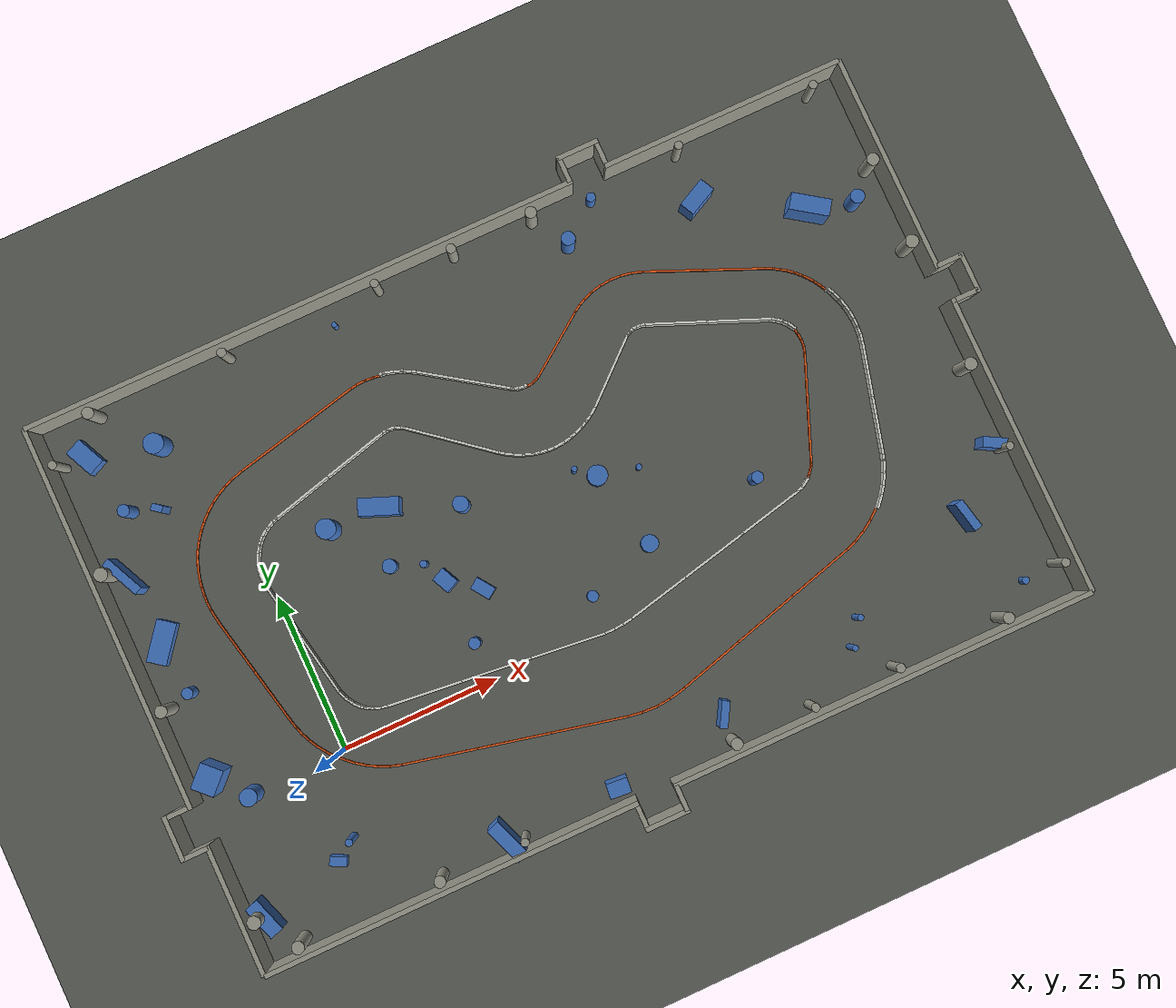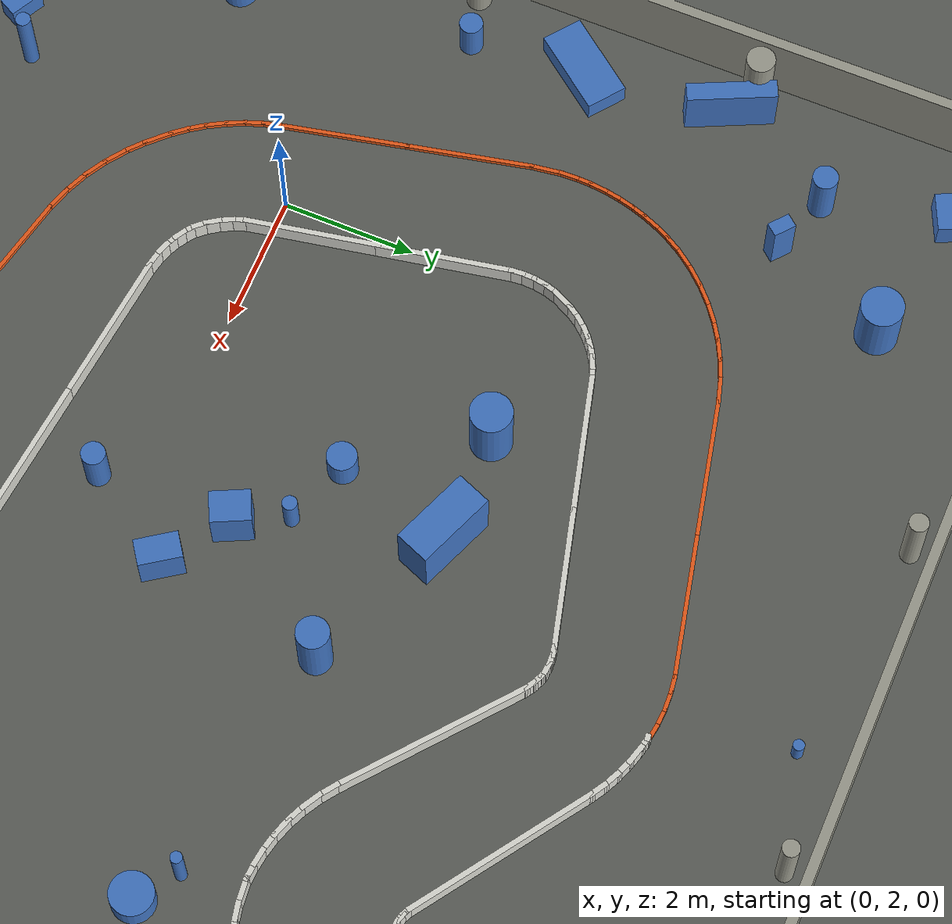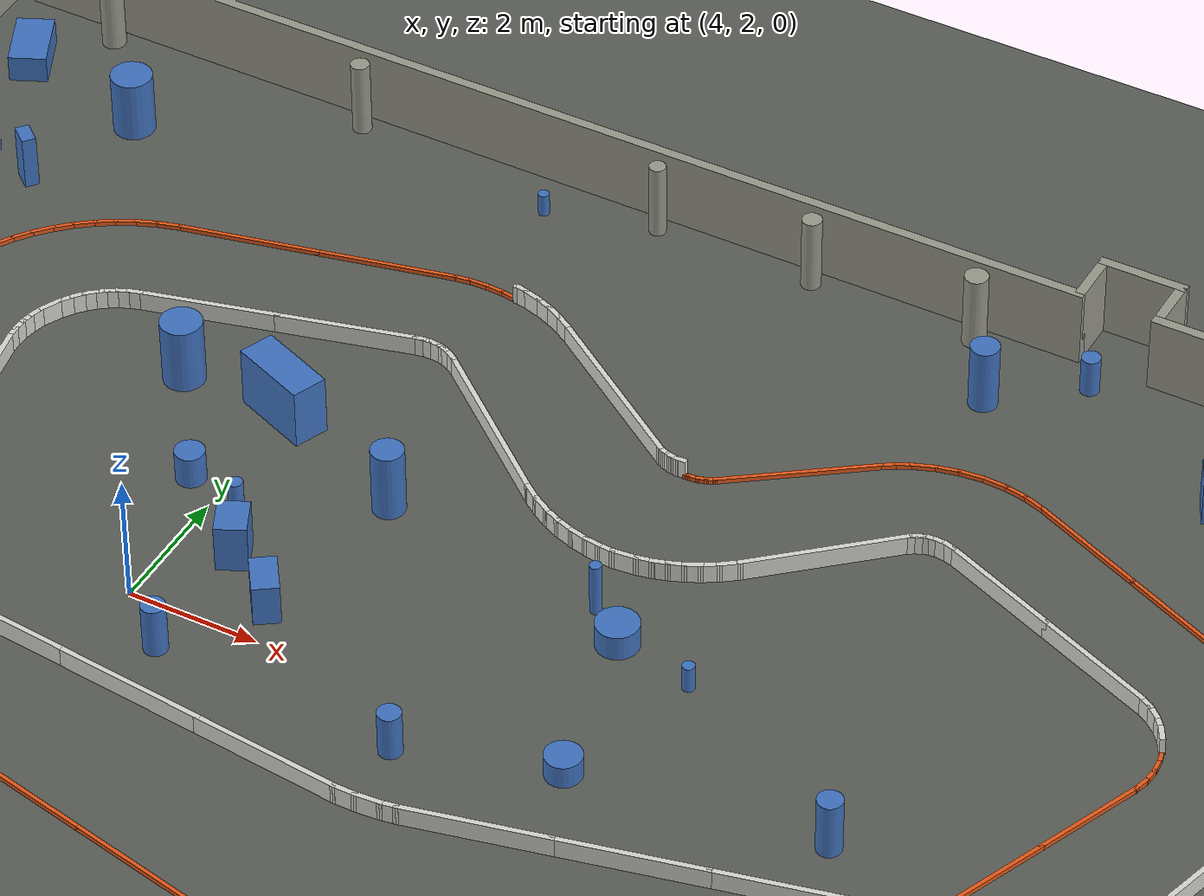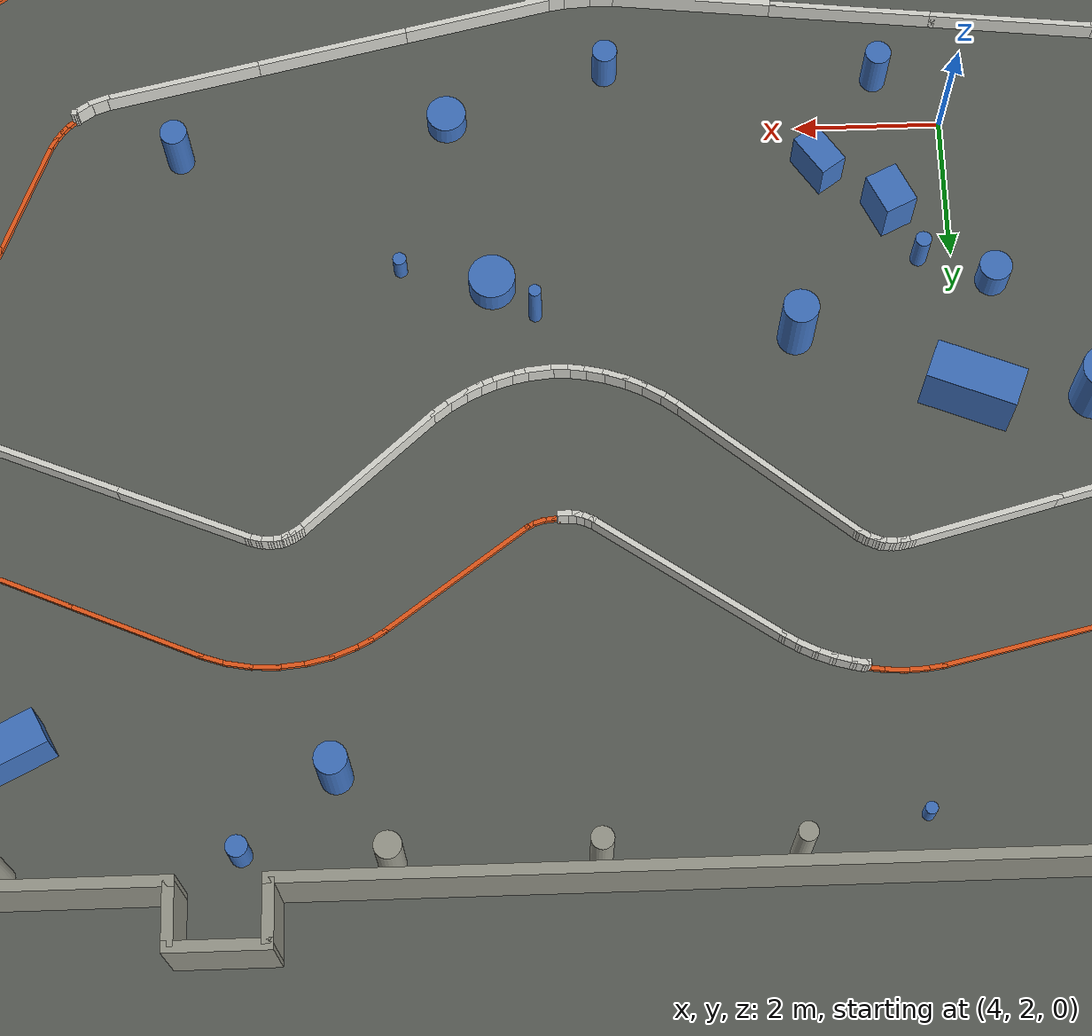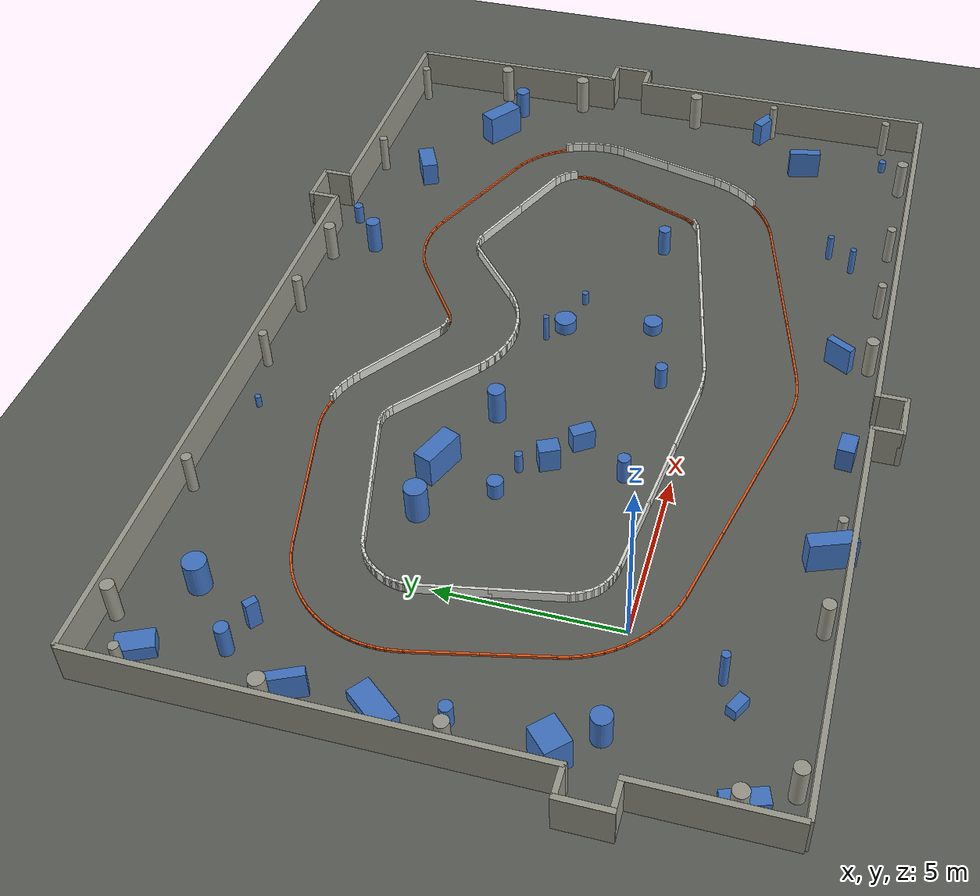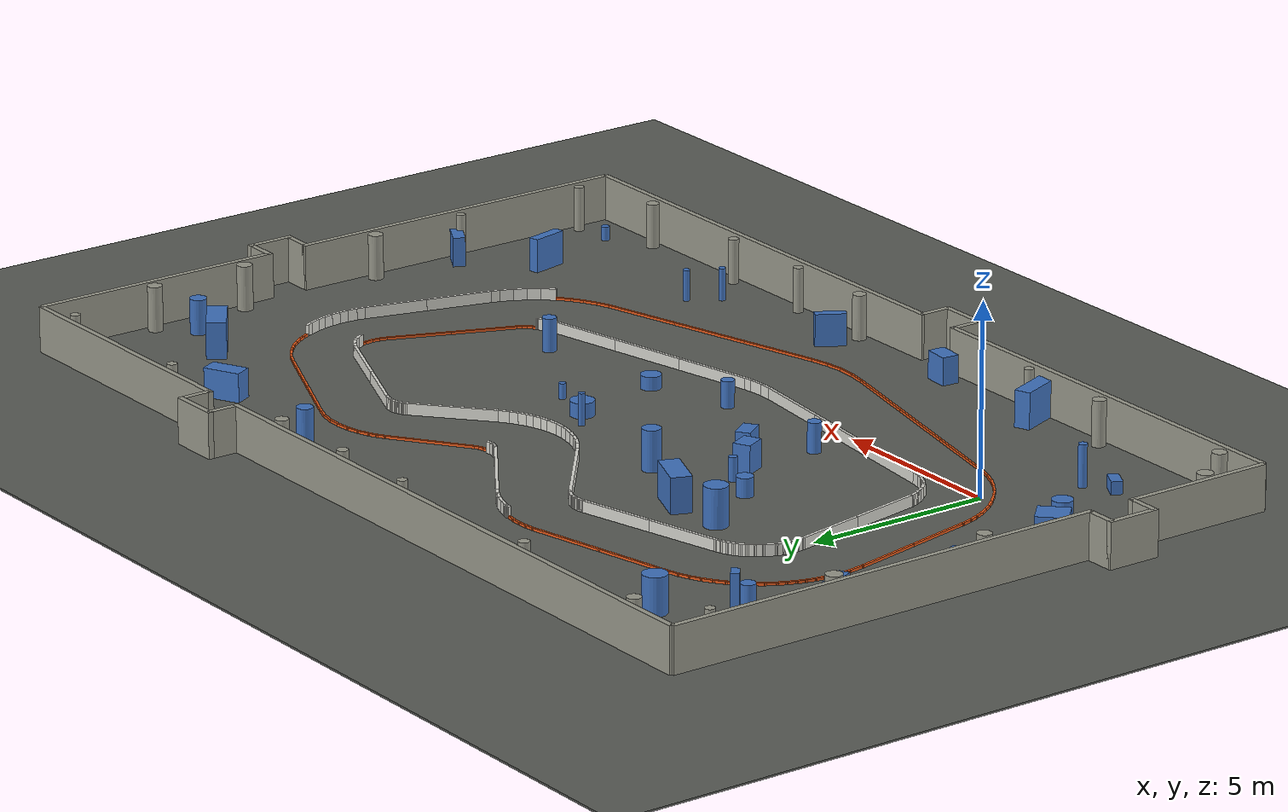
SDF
<?xml version="1.0" ?>
<sdf version="1.9">
  <!-- Generated by simulation/tools/generate_pose_dataset.py --install-gazebo-worlds from tools/pose_dataset/config/tracks.yaml (val_mixed). Do not edit by hand: change the YAML and regenerate. -->
  <world name="default">
    <physics name="default_physics" type="dart">
      <max_step_size>0.001</max_step_size>
      <real_time_factor>1.0</real_time_factor>
      <real_time_update_rate>1000.0</real_time_update_rate>
    </physics>
    <plugin filename="gz-sim-physics-system" name="gz::sim::systems::Physics" />
    <plugin filename="gz-sim-user-commands-system" name="gz::sim::systems::UserCommands" />
    <plugin filename="gz-sim-scene-broadcaster-system" name="gz::sim::systems::SceneBroadcaster" />
    <plugin filename="gz-sim-imu-system" name="gz::sim::systems::Imu" />
    <plugin filename="gz-sim-sensors-system" name="gz::sim::systems::Sensors">
      <render_engine>ogre2</render_engine>
    </plugin>
    <light type="directional" name="sun">
      <pose>0 0 10 0 0 0</pose>
      <diffuse>0.8 0.8 0.8 1</diffuse>
      <direction>-0.5 0.5 -1</direction>
      <cast_shadows>true</cast_shadows>
    </light>
    <model name="track_curb">
      <static>true</static>
      <pose>0 0 0 0 0 0</pose>
      <link name="curb_link">
        <collision name="left0_0_0_collision">
          <pose>16.078633 1.603167 0.035000 0.000000 0.000000 0.693826</pose>
          <geometry>
            <box>
              <size>0.197548 0.060000 0.070000</size>
            </box>
          </geometry>
        </collision>
        <visual name="left0_0_0_visual">
          <pose>16.078633 1.603167 0.035000 0.000000 0.000000 0.693826</pose>
          <geometry>
            <box>
              <size>0.197548 0.060000 0.070000</size>
            </box>
          </geometry>
          <material>
            <ambient>0.9 0.35 0.1 1</ambient>
            <diffuse>0.9 0.35 0.1 1</diffuse>
          </material>
        </visual>
        <collision name="left0_1_0_collision">
          <pose>16.175826 1.694425 0.035000 0.000000 0.000000 0.817677</pose>
          <geometry>
            <box>
              <size>0.189607 0.060000 0.070000</size>
            </box>
          </geometry>
        </collision>
        <visual name="left0_1_0_visual">
          <pose>16.175826 1.694425 0.035000 0.000000 0.000000 0.817677</pose>
          <geometry>
            <box>
              <size>0.189607 0.060000 0.070000</size>
            </box>
          </geometry>
          <material>
            <ambient>0.9 0.35 0.1 1</ambient>
            <diffuse>0.9 0.35 0.1 1</diffuse>
          </material>
        </visual>
        <collision name="left0_2_0_collision">
          <pose>16.261811 1.798933 0.035000 0.000000 0.000000 0.941522</pose>
          <geometry>
            <box>
              <size>0.201580 0.060000 0.070000</size>
            </box>
          </geometry>
        </collision>
        <visual name="left0_2_0_visual">
          <pose>16.261811 1.798933 0.035000 0.000000 0.000000 0.941522</pose>
          <geometry>
            <box>
              <size>0.201580 0.060000 0.070000</size>
            </box>
          </geometry>
          <material>
            <ambient>0.9 0.35 0.1 1</ambient>
            <diffuse>0.9 0.35 0.1 1</diffuse>
          </material>
        </visual>
        <collision name="left0_3_0_collision">
          <pose>16.335764 1.914500 0.035000 0.000000 0.000000 1.065275</pose>
          <geometry>
            <box>
              <size>0.193353 0.060000 0.070000</size>
            </box>
          </geometry>
        </collision>
        <visual name="left0_3_0_visual">
          <pose>16.335764 1.914500 0.035000 0.000000 0.000000 1.065275</pose>
          <geometry>
            <box>
              <size>0.193353 0.060000 0.070000</size>
            </box>
          </geometry>
          <material>
            <ambient>0.9 0.35 0.1 1</ambient>
            <diffuse>0.9 0.35 0.1 1</diffuse>
          </material>
        </visual>
        <collision name="left0_4_0_collision">
          <pose>16.680471 2.750886 0.035000 0.000000 0.000000 1.188962</pose>
          <geometry>
            <box>
              <size>1.736862 0.060000 0.070000</size>
            </box>
          </geometry>
        </collision>
        <visual name="left0_4_0_visual">
          <pose>16.680471 2.750886 0.035000 0.000000 0.000000 1.188962</pose>
          <geometry>
            <box>
              <size>1.736862 0.060000 0.070000</size>
            </box>
          </geometry>
          <material>
            <ambient>0.9 0.35 0.1 1</ambient>
            <diffuse>0.9 0.35 0.1 1</diffuse>
          </material>
        </visual>
        <collision name="left0_4_1_collision">
          <pose>17.305309 4.306985 0.035000 0.000000 0.000000 1.188962</pose>
          <geometry>
            <box>
              <size>1.736862 0.060000 0.070000</size>
            </box>
          </geometry>
        </collision>
        <visual name="left0_4_1_visual">
          <pose>17.305309 4.306985 0.035000 0.000000 0.000000 1.188962</pose>
          <geometry>
            <box>
              <size>1.736862 0.060000 0.070000</size>
            </box>
          </geometry>
          <material>
            <ambient>0.9 0.35 0.1 1</ambient>
            <diffuse>0.9 0.35 0.1 1</diffuse>
          </material>
        </visual>
        <collision name="left0_5_0_collision">
          <pose>17.644919 5.185132 0.035000 0.000000 0.000000 1.305550</pose>
          <geometry>
            <box>
              <size>0.267450 0.060000 0.070000</size>
            </box>
          </geometry>
        </collision>
        <visual name="left0_5_0_visual">
          <pose>17.644919 5.185132 0.035000 0.000000 0.000000 1.305550</pose>
          <geometry>
            <box>
              <size>0.267450 0.060000 0.070000</size>
            </box>
          </geometry>
          <material>
            <ambient>0.9 0.35 0.1 1</ambient>
            <diffuse>0.9 0.35 0.1 1</diffuse>
          </material>
        </visual>
        <collision name="left0_6_0_collision">
          <pose>17.680935 5.390503 0.035000 0.000000 0.000000 1.487161</pose>
          <geometry>
            <box>
              <size>0.271284 0.060000 0.070000</size>
            </box>
          </geometry>
        </collision>
        <visual name="left0_6_0_visual">
          <pose>17.680935 5.390503 0.035000 0.000000 0.000000 1.487161</pose>
          <geometry>
            <box>
              <size>0.271284 0.060000 0.070000</size>
            </box>
          </geometry>
          <material>
            <ambient>0.9 0.35 0.1 1</ambient>
            <diffuse>0.9 0.35 0.1 1</diffuse>
          </material>
        </visual>
        <collision name="left0_7_0_collision">
          <pose>17.678085 5.608746 0.035000 0.000000 0.000000 1.673777</pose>
          <geometry>
            <box>
              <size>0.287146 0.060000 0.070000</size>
            </box>
          </geometry>
        </collision>
        <visual name="left0_7_0_visual">
          <pose>17.678085 5.608746 0.035000 0.000000 0.000000 1.673777</pose>
          <geometry>
            <box>
              <size>0.287146 0.060000 0.070000</size>
            </box>
          </geometry>
          <material>
            <ambient>0.9 0.35 0.1 1</ambient>
            <diffuse>0.9 0.35 0.1 1</diffuse>
          </material>
        </visual>
        <collision name="left0_8_0_collision">
          <pose>17.645784 5.797980 0.035000 0.000000 0.000000 1.834938</pose>
          <geometry>
            <box>
              <size>0.218005 0.060000 0.070000</size>
            </box>
          </geometry>
        </collision>
        <visual name="left0_8_0_visual">
          <pose>17.645784 5.797980 0.035000 0.000000 0.000000 1.834938</pose>
          <geometry>
            <box>
              <size>0.218005 0.060000 0.070000</size>
            </box>
          </geometry>
          <material>
            <ambient>0.9 0.35 0.1 1</ambient>
            <diffuse>0.9 0.35 0.1 1</diffuse>
          </material>
        </visual>
        <collision name="left0_9_0_collision">
          <pose>17.618003 5.877622 0.035000 0.000000 0.000000 2.700316</pose>
          <geometry>
            <box>
              <size>0.075826 0.060000 0.070000</size>
            </box>
          </geometry>
        </collision>
        <visual name="left0_9_0_visual">
          <pose>17.618003 5.877622 0.035000 0.000000 0.000000 2.700316</pose>
          <geometry>
            <box>
              <size>0.075826 0.060000 0.070000</size>
            </box>
          </geometry>
          <material>
            <ambient>0.9 0.35 0.1 1</ambient>
            <diffuse>0.9 0.35 0.1 1</diffuse>
          </material>
        </visual>
        <collision name="right1_0_0_collision">
          <pose>18.983134 6.644705 0.035000 0.000000 0.000000 2.041905</pose>
          <geometry>
            <box>
              <size>0.282078 0.060000 0.070000</size>
            </box>
          </geometry>
        </collision>
        <visual name="right1_0_0_visual">
          <pose>18.983134 6.644705 0.035000 0.000000 0.000000 2.041905</pose>
          <geometry>
            <box>
              <size>0.282078 0.060000 0.070000</size>
            </box>
          </geometry>
          <material>
            <ambient>0.9 0.35 0.1 1</ambient>
            <diffuse>0.9 0.35 0.1 1</diffuse>
          </material>
        </visual>
        <collision name="right1_1_0_collision">
          <pose>18.874577 6.838299 0.035000 0.000000 0.000000 2.121788</pose>
          <geometry>
            <box>
              <size>0.282184 0.060000 0.070000</size>
            </box>
          </geometry>
        </collision>
        <visual name="right1_1_0_visual">
          <pose>18.874577 6.838299 0.035000 0.000000 0.000000 2.121788</pose>
          <geometry>
            <box>
              <size>0.282184 0.060000 0.070000</size>
            </box>
          </geometry>
          <material>
            <ambient>0.9 0.35 0.1 1</ambient>
            <diffuse>0.9 0.35 0.1 1</diffuse>
          </material>
        </visual>
        <collision name="right1_2_0_collision">
          <pose>18.750858 7.022700 0.035000 0.000000 0.000000 2.201671</pose>
          <geometry>
            <box>
              <size>0.282289 0.060000 0.070000</size>
            </box>
          </geometry>
        </collision>
        <visual name="right1_2_0_visual">
          <pose>18.750858 7.022700 0.035000 0.000000 0.000000 2.201671</pose>
          <geometry>
            <box>
              <size>0.282289 0.060000 0.070000</size>
            </box>
          </geometry>
          <material>
            <ambient>0.9 0.35 0.1 1</ambient>
            <diffuse>0.9 0.35 0.1 1</diffuse>
          </material>
        </visual>
        <collision name="right1_3_0_collision">
          <pose>18.612753 7.196724 0.035000 0.000000 0.000000 2.281554</pose>
          <geometry>
            <box>
              <size>0.282395 0.060000 0.070000</size>
            </box>
          </geometry>
        </collision>
        <visual name="right1_3_0_visual">
          <pose>18.612753 7.196724 0.035000 0.000000 0.000000 2.281554</pose>
          <geometry>
            <box>
              <size>0.282395 0.060000 0.070000</size>
            </box>
          </geometry>
          <material>
            <ambient>0.9 0.35 0.1 1</ambient>
            <diffuse>0.9 0.35 0.1 1</diffuse>
          </material>
        </visual>
        <collision name="right1_4_0_collision">
          <pose>18.461130 7.359248 0.035000 0.000000 0.000000 2.361437</pose>
          <geometry>
            <box>
              <size>0.282500 0.060000 0.070000</size>
            </box>
          </geometry>
        </collision>
        <visual name="right1_4_0_visual">
          <pose>18.461130 7.359248 0.035000 0.000000 0.000000 2.361437</pose>
          <geometry>
            <box>
              <size>0.282500 0.060000 0.070000</size>
            </box>
          </geometry>
          <material>
            <ambient>0.9 0.35 0.1 1</ambient>
            <diffuse>0.9 0.35 0.1 1</diffuse>
          </material>
        </visual>
        <collision name="right1_5_0_collision">
          <pose>18.296943 7.509227 0.035000 0.000000 0.000000 2.441321</pose>
          <geometry>
            <box>
              <size>0.282606 0.060000 0.070000</size>
            </box>
          </geometry>
        </collision>
        <visual name="right1_5_0_visual">
          <pose>18.296943 7.509227 0.035000 0.000000 0.000000 2.441321</pose>
          <geometry>
            <box>
              <size>0.282606 0.060000 0.070000</size>
            </box>
          </geometry>
          <material>
            <ambient>0.9 0.35 0.1 1</ambient>
            <diffuse>0.9 0.35 0.1 1</diffuse>
          </material>
        </visual>
        <collision name="right1_6_0_collision">
          <pose>18.121229 7.645690 0.035000 0.000000 0.000000 2.521204</pose>
          <geometry>
            <box>
              <size>0.282711 0.060000 0.070000</size>
            </box>
          </geometry>
        </collision>
        <visual name="right1_6_0_visual">
          <pose>18.121229 7.645690 0.035000 0.000000 0.000000 2.521204</pose>
          <geometry>
            <box>
              <size>0.282711 0.060000 0.070000</size>
            </box>
          </geometry>
          <material>
            <ambient>0.9 0.35 0.1 1</ambient>
            <diffuse>0.9 0.35 0.1 1</diffuse>
          </material>
        </visual>
        <collision name="right1_7_0_collision">
          <pose>17.935097 7.767754 0.035000 0.000000 0.000000 2.601087</pose>
          <geometry>
            <box>
              <size>0.282817 0.060000 0.070000</size>
            </box>
          </geometry>
        </collision>
        <visual name="right1_7_0_visual">
          <pose>17.935097 7.767754 0.035000 0.000000 0.000000 2.601087</pose>
          <geometry>
            <box>
              <size>0.282817 0.060000 0.070000</size>
            </box>
          </geometry>
          <material>
            <ambient>0.9 0.35 0.1 1</ambient>
            <diffuse>0.9 0.35 0.1 1</diffuse>
          </material>
        </visual>
        <collision name="right1_8_0_collision">
          <pose>17.715077 7.885376 0.035000 0.000000 0.000000 2.690567</pose>
          <geometry>
            <box>
              <size>0.336652 0.060000 0.070000</size>
            </box>
          </geometry>
        </collision>
        <visual name="right1_8_0_visual">
          <pose>17.715077 7.885376 0.035000 0.000000 0.000000 2.690567</pose>
          <geometry>
            <box>
              <size>0.336652 0.060000 0.070000</size>
            </box>
          </geometry>
          <material>
            <ambient>0.9 0.35 0.1 1</ambient>
            <diffuse>0.9 0.35 0.1 1</diffuse>
          </material>
        </visual>
        <collision name="right1_9_0_collision">
          <pose>16.733818 8.310922 0.035000 0.000000 0.000000 2.738609</pose>
          <geometry>
            <box>
              <size>1.922746 0.060000 0.070000</size>
            </box>
          </geometry>
        </collision>
        <visual name="right1_9_0_visual">
          <pose>16.733818 8.310922 0.035000 0.000000 0.000000 2.738609</pose>
          <geometry>
            <box>
              <size>1.922746 0.060000 0.070000</size>
            </box>
          </geometry>
          <material>
            <ambient>0.9 0.35 0.1 1</ambient>
            <diffuse>0.9 0.35 0.1 1</diffuse>
          </material>
        </visual>
        <collision name="right1_9_1_collision">
          <pose>15.020287 9.041425 0.035000 0.000000 0.000000 2.738609</pose>
          <geometry>
            <box>
              <size>1.922746 0.060000 0.070000</size>
            </box>
          </geometry>
        </collision>
        <visual name="right1_9_1_visual">
          <pose>15.020287 9.041425 0.035000 0.000000 0.000000 2.738609</pose>
          <geometry>
            <box>
              <size>1.922746 0.060000 0.070000</size>
            </box>
          </geometry>
          <material>
            <ambient>0.9 0.35 0.1 1</ambient>
            <diffuse>0.9 0.35 0.1 1</diffuse>
          </material>
        </visual>
        <collision name="right1_10_0_collision">
          <pose>14.006226 9.458698 0.035000 0.000000 0.000000 2.822189</pose>
          <geometry>
            <box>
              <size>0.391350 0.060000 0.070000</size>
            </box>
          </geometry>
        </collision>
        <visual name="right1_10_0_visual">
          <pose>14.006226 9.458698 0.035000 0.000000 0.000000 2.822189</pose>
          <geometry>
            <box>
              <size>0.391350 0.060000 0.070000</size>
            </box>
          </geometry>
          <material>
            <ambient>0.9 0.35 0.1 1</ambient>
            <diffuse>0.9 0.35 0.1 1</diffuse>
          </material>
        </visual>
        <collision name="right1_11_0_collision">
          <pose>13.685887 9.540827 0.035000 0.000000 0.000000 2.958993</pose>
          <geometry>
            <box>
              <size>0.391598 0.060000 0.070000</size>
            </box>
          </geometry>
        </collision>
        <visual name="right1_11_0_visual">
          <pose>13.685887 9.540827 0.035000 0.000000 0.000000 2.958993</pose>
          <geometry>
            <box>
              <size>0.391598 0.060000 0.070000</size>
            </box>
          </geometry>
          <material>
            <ambient>0.9 0.35 0.1 1</ambient>
            <diffuse>0.9 0.35 0.1 1</diffuse>
          </material>
        </visual>
        <collision name="right1_12_0_collision">
          <pose>13.342001 9.578095 0.035000 0.000000 0.000000 3.102018</pose>
          <geometry>
            <box>
              <size>0.421971 0.060000 0.070000</size>
            </box>
          </geometry>
        </collision>
        <visual name="right1_12_0_visual">
          <pose>13.342001 9.578095 0.035000 0.000000 0.000000 3.102018</pose>
          <geometry>
            <box>
              <size>0.421971 0.060000 0.070000</size>
            </box>
          </geometry>
          <material>
            <ambient>0.9 0.35 0.1 1</ambient>
            <diffuse>0.9 0.35 0.1 1</diffuse>
          </material>
        </visual>
        <collision name="right1_13_0_collision">
          <pose>12.980816 9.566971 0.035000 0.000000 0.000000 -3.040550</pose>
          <geometry>
            <box>
              <size>0.422530 0.060000 0.070000</size>
            </box>
          </geometry>
        </collision>
        <visual name="right1_13_0_visual">
          <pose>12.980816 9.566971 0.035000 0.000000 0.000000 -3.040550</pose>
          <geometry>
            <box>
              <size>0.422530 0.060000 0.070000</size>
            </box>
          </geometry>
          <material>
            <ambient>0.9 0.35 0.1 1</ambient>
            <diffuse>0.9 0.35 0.1 1</diffuse>
          </material>
        </visual>
        <collision name="right1_14_0_collision">
          <pose>12.637970 9.511169 0.035000 0.000000 0.000000 -2.914699</pose>
          <geometry>
            <box>
              <size>0.393561 0.060000 0.070000</size>
            </box>
          </geometry>
        </collision>
        <visual name="right1_14_0_visual">
          <pose>12.637970 9.511169 0.035000 0.000000 0.000000 -2.914699</pose>
          <geometry>
            <box>
              <size>0.393561 0.060000 0.070000</size>
            </box>
          </geometry>
          <material>
            <ambient>0.9 0.35 0.1 1</ambient>
            <diffuse>0.9 0.35 0.1 1</diffuse>
          </material>
        </visual>
        <collision name="right1_15_0_collision">
          <pose>12.318934 9.414048 0.035000 0.000000 0.000000 -2.777765</pose>
          <geometry>
            <box>
              <size>0.394987 0.060000 0.070000</size>
            </box>
          </geometry>
        </collision>
        <visual name="right1_15_0_visual">
          <pose>12.318934 9.414048 0.035000 0.000000 0.000000 -2.777765</pose>
          <geometry>
            <box>
              <size>0.394987 0.060000 0.070000</size>
            </box>
          </geometry>
          <material>
            <ambient>0.9 0.35 0.1 1</ambient>
            <diffuse>0.9 0.35 0.1 1</diffuse>
          </material>
        </visual>
        <collision name="right1_16_0_collision">
          <pose>12.067284 9.305427 0.035000 0.000000 0.000000 -2.665758</pose>
          <geometry>
            <box>
              <size>0.274016 0.060000 0.070000</size>
            </box>
          </geometry>
        </collision>
        <visual name="right1_16_0_visual">
          <pose>12.067284 9.305427 0.035000 0.000000 0.000000 -2.665758</pose>
          <geometry>
            <box>
              <size>0.274016 0.060000 0.070000</size>
            </box>
          </geometry>
          <material>
            <ambient>0.9 0.35 0.1 1</ambient>
            <diffuse>0.9 0.35 0.1 1</diffuse>
          </material>
        </visual>
        <collision name="right1_17_0_collision">
          <pose>11.881426 9.199144 0.035000 0.000000 0.000000 -2.578620</pose>
          <geometry>
            <box>
              <size>0.274594 0.060000 0.070000</size>
            </box>
          </geometry>
        </collision>
        <visual name="right1_17_0_visual">
          <pose>11.881426 9.199144 0.035000 0.000000 0.000000 -2.578620</pose>
          <geometry>
            <box>
              <size>0.274594 0.060000 0.070000</size>
            </box>
          </geometry>
          <material>
            <ambient>0.9 0.35 0.1 1</ambient>
            <diffuse>0.9 0.35 0.1 1</diffuse>
          </material>
        </visual>
        <collision name="right1_18_0_collision">
          <pose>10.850913 8.461335 0.035000 0.000000 0.000000 -2.514838</pose>
          <geometry>
            <box>
              <size>2.380618 0.060000 0.070000</size>
            </box>
          </geometry>
        </collision>
        <visual name="right1_18_0_visual">
          <pose>10.850913 8.461335 0.035000 0.000000 0.000000 -2.514838</pose>
          <geometry>
            <box>
              <size>2.380618 0.060000 0.070000</size>
            </box>
          </geometry>
          <material>
            <ambient>0.9 0.35 0.1 1</ambient>
            <diffuse>0.9 0.35 0.1 1</diffuse>
          </material>
        </visual>
        <collision name="right1_19_0_collision">
          <pose>9.858715 7.754235 0.035000 0.000000 0.000000 -2.672703</pose>
          <geometry>
            <box>
              <size>0.177531 0.060000 0.070000</size>
            </box>
          </geometry>
        </collision>
        <visual name="right1_19_0_visual">
          <pose>9.858715 7.754235 0.035000 0.000000 0.000000 -2.672703</pose>
          <geometry>
            <box>
              <size>0.177531 0.060000 0.070000</size>
            </box>
          </geometry>
          <material>
            <ambient>0.9 0.35 0.1 1</ambient>
            <diffuse>0.9 0.35 0.1 1</diffuse>
          </material>
        </visual>
        <collision name="right1_20_0_collision">
          <pose>9.747245 7.709569 0.035000 0.000000 0.000000 -2.844000</pose>
          <geometry>
            <box>
              <size>0.183524 0.060000 0.070000</size>
            </box>
          </geometry>
        </collision>
        <visual name="right1_20_0_visual">
          <pose>9.747245 7.709569 0.035000 0.000000 0.000000 -2.844000</pose>
          <geometry>
            <box>
              <size>0.183524 0.060000 0.070000</size>
            </box>
          </geometry>
          <material>
            <ambient>0.9 0.35 0.1 1</ambient>
            <diffuse>0.9 0.35 0.1 1</diffuse>
          </material>
        </visual>
        <collision name="right1_21_0_collision">
          <pose>9.620118 7.684042 0.035000 0.000000 0.000000 -3.033072</pose>
          <geometry>
            <box>
              <size>0.196965 0.060000 0.070000</size>
            </box>
          </geometry>
        </collision>
        <visual name="right1_21_0_visual">
          <pose>9.620118 7.684042 0.035000 0.000000 0.000000 -3.033072</pose>
          <geometry>
            <box>
              <size>0.196965 0.060000 0.070000</size>
            </box>
          </geometry>
          <material>
            <ambient>0.9 0.35 0.1 1</ambient>
            <diffuse>0.9 0.35 0.1 1</diffuse>
          </material>
        </visual>
        <collision name="right1_22_0_collision">
          <pose>9.516416 7.678248 0.035000 0.000000 0.000000 3.096064</pose>
          <geometry>
            <box>
              <size>0.131318 0.060000 0.070000</size>
            </box>
          </geometry>
        </collision>
        <visual name="right1_22_0_visual">
          <pose>9.516416 7.678248 0.035000 0.000000 0.000000 3.096064</pose>
          <geometry>
            <box>
              <size>0.131318 0.060000 0.070000</size>
            </box>
          </geometry>
          <material>
            <ambient>0.9 0.35 0.1 1</ambient>
            <diffuse>0.9 0.35 0.1 1</diffuse>
          </material>
        </visual>
        <collision name="right1_23_0_collision">
          <pose>9.476834 7.684839 0.035000 0.000000 0.000000 2.243709</pose>
          <geometry>
            <box>
              <size>0.072706 0.060000 0.070000</size>
            </box>
          </geometry>
        </collision>
        <visual name="right1_23_0_visual">
          <pose>9.476834 7.684839 0.035000 0.000000 0.000000 2.243709</pose>
          <geometry>
            <box>
              <size>0.072706 0.060000 0.070000</size>
            </box>
          </geometry>
          <material>
            <ambient>0.9 0.35 0.1 1</ambient>
            <diffuse>0.9 0.35 0.1 1</diffuse>
          </material>
        </visual>
        <collision name="right3_0_0_collision">
          <pose>5.471395 9.852353 0.035000 0.000000 0.000000 2.989354</pose>
          <geometry>
            <box>
              <size>0.320955 0.060000 0.070000</size>
            </box>
          </geometry>
        </collision>
        <visual name="right3_0_0_visual">
          <pose>5.471395 9.852353 0.035000 0.000000 0.000000 2.989354</pose>
          <geometry>
            <box>
              <size>0.320955 0.060000 0.070000</size>
            </box>
          </geometry>
          <material>
            <ambient>0.9 0.35 0.1 1</ambient>
            <diffuse>0.9 0.35 0.1 1</diffuse>
          </material>
        </visual>
        <collision name="right3_1_0_collision">
          <pose>5.212000 9.879063 0.035000 0.000000 0.000000 3.088560</pose>
          <geometry>
            <box>
              <size>0.321220 0.060000 0.070000</size>
            </box>
          </geometry>
        </collision>
        <visual name="right3_1_0_visual">
          <pose>5.212000 9.879063 0.035000 0.000000 0.000000 3.088560</pose>
          <geometry>
            <box>
              <size>0.321220 0.060000 0.070000</size>
            </box>
          </geometry>
          <material>
            <ambient>0.9 0.35 0.1 1</ambient>
            <diffuse>0.9 0.35 0.1 1</diffuse>
          </material>
        </visual>
        <collision name="right3_2_0_collision">
          <pose>4.950970 9.879952 0.035000 0.000000 0.000000 -3.095418</pose>
          <geometry>
            <box>
              <size>0.321485 0.060000 0.070000</size>
            </box>
          </geometry>
        </collision>
        <visual name="right3_2_0_visual">
          <pose>4.950970 9.879952 0.035000 0.000000 0.000000 -3.095418</pose>
          <geometry>
            <box>
              <size>0.321485 0.060000 0.070000</size>
            </box>
          </geometry>
          <material>
            <ambient>0.9 0.35 0.1 1</ambient>
            <diffuse>0.9 0.35 0.1 1</diffuse>
          </material>
        </visual>
        <collision name="right3_3_0_collision">
          <pose>4.705166 9.857698 0.035000 0.000000 0.000000 -3.001725</pose>
          <geometry>
            <box>
              <size>0.292674 0.060000 0.070000</size>
            </box>
          </geometry>
        </collision>
        <visual name="right3_3_0_visual">
          <pose>4.705166 9.857698 0.035000 0.000000 0.000000 -3.001725</pose>
          <geometry>
            <box>
              <size>0.292674 0.060000 0.070000</size>
            </box>
          </geometry>
          <material>
            <ambient>0.9 0.35 0.1 1</ambient>
            <diffuse>0.9 0.35 0.1 1</diffuse>
          </material>
        </visual>
        <collision name="right3_4_0_collision">
          <pose>3.573479 9.611183 0.035000 0.000000 0.000000 -2.918793</pose>
          <geometry>
            <box>
              <size>2.144496 0.060000 0.070000</size>
            </box>
          </geometry>
        </collision>
        <visual name="right3_4_0_visual">
          <pose>3.573479 9.611183 0.035000 0.000000 0.000000 -2.918793</pose>
          <geometry>
            <box>
              <size>2.144496 0.060000 0.070000</size>
            </box>
          </geometry>
          <material>
            <ambient>0.9 0.35 0.1 1</ambient>
            <diffuse>0.9 0.35 0.1 1</diffuse>
          </material>
        </visual>
        <collision name="right3_4_1_collision">
          <pose>1.540507 9.150590 0.035000 0.000000 0.000000 -2.918793</pose>
          <geometry>
            <box>
              <size>2.144496 0.060000 0.070000</size>
            </box>
          </geometry>
        </collision>
        <visual name="right3_4_1_visual">
          <pose>1.540507 9.150590 0.035000 0.000000 0.000000 -2.918793</pose>
          <geometry>
            <box>
              <size>2.144496 0.060000 0.070000</size>
            </box>
          </geometry>
          <material>
            <ambient>0.9 0.35 0.1 1</ambient>
            <diffuse>0.9 0.35 0.1 1</diffuse>
          </material>
        </visual>
        <collision name="right3_5_0_collision">
          <pose>0.353435 8.870936 0.035000 0.000000 0.000000 -2.859940</pose>
          <geometry>
            <box>
              <size>0.415165 0.060000 0.070000</size>
            </box>
          </geometry>
        </collision>
        <visual name="right3_5_0_visual">
          <pose>0.353435 8.870936 0.035000 0.000000 0.000000 -2.859940</pose>
          <geometry>
            <box>
              <size>0.415165 0.060000 0.070000</size>
            </box>
          </geometry>
          <material>
            <ambient>0.9 0.35 0.1 1</ambient>
            <diffuse>0.9 0.35 0.1 1</diffuse>
          </material>
        </visual>
        <collision name="right3_6_0_collision">
          <pose>0.042467 8.765309 0.035000 0.000000 0.000000 -2.760375</pose>
          <geometry>
            <box>
              <size>0.362480 0.060000 0.070000</size>
            </box>
          </geometry>
        </collision>
        <visual name="right3_6_0_visual">
          <pose>0.042467 8.765309 0.035000 0.000000 0.000000 -2.760375</pose>
          <geometry>
            <box>
              <size>0.362480 0.060000 0.070000</size>
            </box>
          </geometry>
          <material>
            <ambient>0.9 0.35 0.1 1</ambient>
            <diffuse>0.9 0.35 0.1 1</diffuse>
          </material>
        </visual>
        <collision name="right3_7_0_collision">
          <pose>-0.232705 8.640114 0.035000 0.000000 0.000000 -2.668900</pose>
          <geometry>
            <box>
              <size>0.362780 0.060000 0.070000</size>
            </box>
          </geometry>
        </collision>
        <visual name="right3_7_0_visual">
          <pose>-0.232705 8.640114 0.035000 0.000000 0.000000 -2.668900</pose>
          <geometry>
            <box>
              <size>0.362780 0.060000 0.070000</size>
            </box>
          </geometry>
          <material>
            <ambient>0.9 0.35 0.1 1</ambient>
            <diffuse>0.9 0.35 0.1 1</diffuse>
          </material>
        </visual>
        <collision name="right3_8_0_collision">
          <pose>-0.495551 8.490158 0.035000 0.000000 0.000000 -2.577425</pose>
          <geometry>
            <box>
              <size>0.363081 0.060000 0.070000</size>
            </box>
          </geometry>
        </collision>
        <visual name="right3_8_0_visual">
          <pose>-0.495551 8.490158 0.035000 0.000000 0.000000 -2.577425</pose>
          <geometry>
            <box>
              <size>0.363081 0.060000 0.070000</size>
            </box>
          </geometry>
          <material>
            <ambient>0.9 0.35 0.1 1</ambient>
            <diffuse>0.9 0.35 0.1 1</diffuse>
          </material>
        </visual>
        <collision name="right3_9_0_collision">
          <pose>-0.743846 8.316646 0.035000 0.000000 0.000000 -2.485950</pose>
          <geometry>
            <box>
              <size>0.363381 0.060000 0.070000</size>
            </box>
          </geometry>
        </collision>
        <visual name="right3_9_0_visual">
          <pose>-0.743846 8.316646 0.035000 0.000000 0.000000 -2.485950</pose>
          <geometry>
            <box>
              <size>0.363381 0.060000 0.070000</size>
            </box>
          </geometry>
          <material>
            <ambient>0.9 0.35 0.1 1</ambient>
            <diffuse>0.9 0.35 0.1 1</diffuse>
          </material>
        </visual>
        <collision name="right3_10_0_collision">
          <pose>-0.975483 8.120986 0.035000 0.000000 0.000000 -2.394475</pose>
          <geometry>
            <box>
              <size>0.363682 0.060000 0.070000</size>
            </box>
          </geometry>
        </collision>
        <visual name="right3_10_0_visual">
          <pose>-0.975483 8.120986 0.035000 0.000000 0.000000 -2.394475</pose>
          <geometry>
            <box>
              <size>0.363682 0.060000 0.070000</size>
            </box>
          </geometry>
          <material>
            <ambient>0.9 0.35 0.1 1</ambient>
            <diffuse>0.9 0.35 0.1 1</diffuse>
          </material>
        </visual>
        <collision name="right3_11_0_collision">
          <pose>-1.188489 7.904769 0.035000 0.000000 0.000000 -2.303000</pose>
          <geometry>
            <box>
              <size>0.363982 0.060000 0.070000</size>
            </box>
          </geometry>
        </collision>
        <visual name="right3_11_0_visual">
          <pose>-1.188489 7.904769 0.035000 0.000000 0.000000 -2.303000</pose>
          <geometry>
            <box>
              <size>0.363982 0.060000 0.070000</size>
            </box>
          </geometry>
          <material>
            <ambient>0.9 0.35 0.1 1</ambient>
            <diffuse>0.9 0.35 0.1 1</diffuse>
          </material>
        </visual>
        <collision name="right3_12_0_collision">
          <pose>-1.381043 7.669768 0.035000 0.000000 0.000000 -2.211525</pose>
          <geometry>
            <box>
              <size>0.364282 0.060000 0.070000</size>
            </box>
          </geometry>
        </collision>
        <visual name="right3_12_0_visual">
          <pose>-1.381043 7.669768 0.035000 0.000000 0.000000 -2.211525</pose>
          <geometry>
            <box>
              <size>0.364282 0.060000 0.070000</size>
            </box>
          </geometry>
          <material>
            <ambient>0.9 0.35 0.1 1</ambient>
            <diffuse>0.9 0.35 0.1 1</diffuse>
          </material>
        </visual>
        <collision name="right3_13_0_collision">
          <pose>-1.542707 7.428895 0.035000 0.000000 0.000000 -2.107327</pose>
          <geometry>
            <box>
              <size>0.336693 0.060000 0.070000</size>
            </box>
          </geometry>
        </collision>
        <visual name="right3_13_0_visual">
          <pose>-1.542707 7.428895 0.035000 0.000000 0.000000 -2.107327</pose>
          <geometry>
            <box>
              <size>0.336693 0.060000 0.070000</size>
            </box>
          </geometry>
          <material>
            <ambient>0.9 0.35 0.1 1</ambient>
            <diffuse>0.9 0.35 0.1 1</diffuse>
          </material>
        </visual>
        <collision name="right3_14_0_collision">
          <pose>-1.662284 7.210737 0.035000 0.000000 0.000000 -2.028254</pose>
          <geometry>
            <box>
              <size>0.281252 0.060000 0.070000</size>
            </box>
          </geometry>
        </collision>
        <visual name="right3_14_0_visual">
          <pose>-1.662284 7.210737 0.035000 0.000000 0.000000 -2.028254</pose>
          <geometry>
            <box>
              <size>0.281252 0.060000 0.070000</size>
            </box>
          </geometry>
          <material>
            <ambient>0.9 0.35 0.1 1</ambient>
            <diffuse>0.9 0.35 0.1 1</diffuse>
          </material>
        </visual>
        <collision name="right3_15_0_collision">
          <pose>-1.758052 6.996314 0.035000 0.000000 0.000000 -1.957571</pose>
          <geometry>
            <box>
              <size>0.308715 0.060000 0.070000</size>
            </box>
          </geometry>
        </collision>
        <visual name="right3_15_0_visual">
          <pose>-1.758052 6.996314 0.035000 0.000000 0.000000 -1.957571</pose>
          <geometry>
            <box>
              <size>0.308715 0.060000 0.070000</size>
            </box>
          </geometry>
          <material>
            <ambient>0.9 0.35 0.1 1</ambient>
            <diffuse>0.9 0.35 0.1 1</diffuse>
          </material>
        </visual>
        <collision name="right3_16_0_collision">
          <pose>-1.839298 6.776151 0.035000 0.000000 0.000000 -1.886885</pose>
          <geometry>
            <box>
              <size>0.280929 0.060000 0.070000</size>
            </box>
          </geometry>
        </collision>
        <visual name="right3_16_0_visual">
          <pose>-1.839298 6.776151 0.035000 0.000000 0.000000 -1.886885</pose>
          <geometry>
            <box>
              <size>0.280929 0.060000 0.070000</size>
            </box>
          </geometry>
          <material>
            <ambient>0.9 0.35 0.1 1</ambient>
            <diffuse>0.9 0.35 0.1 1</diffuse>
          </material>
        </visual>
        <collision name="right3_17_0_collision">
          <pose>-1.903804 6.550704 0.035000 0.000000 0.000000 -1.816202</pose>
          <geometry>
            <box>
              <size>0.308351 0.060000 0.070000</size>
            </box>
          </geometry>
        </collision>
        <visual name="right3_17_0_visual">
          <pose>-1.903804 6.550704 0.035000 0.000000 0.000000 -1.816202</pose>
          <geometry>
            <box>
              <size>0.308351 0.060000 0.070000</size>
            </box>
          </geometry>
          <material>
            <ambient>0.9 0.35 0.1 1</ambient>
            <diffuse>0.9 0.35 0.1 1</diffuse>
          </material>
        </visual>
        <collision name="right3_18_0_collision">
          <pose>-1.953147 6.321626 0.035000 0.000000 0.000000 -1.745516</pose>
          <geometry>
            <box>
              <size>0.280605 0.060000 0.070000</size>
            </box>
          </geometry>
        </collision>
        <visual name="right3_18_0_visual">
          <pose>-1.953147 6.321626 0.035000 0.000000 0.000000 -1.745516</pose>
          <geometry>
            <box>
              <size>0.280605 0.060000 0.070000</size>
            </box>
          </geometry>
          <material>
            <ambient>0.9 0.35 0.1 1</ambient>
            <diffuse>0.9 0.35 0.1 1</diffuse>
          </material>
        </visual>
        <collision name="right3_19_0_collision">
          <pose>-1.985198 6.089680 0.035000 0.000000 0.000000 -1.674833</pose>
          <geometry>
            <box>
              <size>0.307987 0.060000 0.070000</size>
            </box>
          </geometry>
        </collision>
        <visual name="right3_19_0_visual">
          <pose>-1.985198 6.089680 0.035000 0.000000 0.000000 -1.674833</pose>
          <geometry>
            <box>
              <size>0.307987 0.060000 0.070000</size>
            </box>
          </geometry>
          <material>
            <ambient>0.9 0.35 0.1 1</ambient>
            <diffuse>0.9 0.35 0.1 1</diffuse>
          </material>
        </visual>
        <collision name="right3_20_0_collision">
          <pose>-2.001747 5.856277 0.035000 0.000000 0.000000 -1.604147</pose>
          <geometry>
            <box>
              <size>0.280282 0.060000 0.070000</size>
            </box>
          </geometry>
        </collision>
        <visual name="right3_20_0_visual">
          <pose>-2.001747 5.856277 0.035000 0.000000 0.000000 -1.604147</pose>
          <geometry>
            <box>
              <size>0.280282 0.060000 0.070000</size>
            </box>
          </geometry>
          <material>
            <ambient>0.9 0.35 0.1 1</ambient>
            <diffuse>0.9 0.35 0.1 1</diffuse>
          </material>
        </visual>
        <collision name="right3_21_0_collision">
          <pose>-2.000798 5.622472 0.035000 0.000000 0.000000 -1.533464</pose>
          <geometry>
            <box>
              <size>0.307623 0.060000 0.070000</size>
            </box>
          </geometry>
        </collision>
        <visual name="right3_21_0_visual">
          <pose>-2.000798 5.622472 0.035000 0.000000 0.000000 -1.533464</pose>
          <geometry>
            <box>
              <size>0.307623 0.060000 0.070000</size>
            </box>
          </geometry>
          <material>
            <ambient>0.9 0.35 0.1 1</ambient>
            <diffuse>0.9 0.35 0.1 1</diffuse>
          </material>
        </visual>
        <collision name="right3_22_0_collision">
          <pose>-1.965418 5.282097 0.035000 0.000000 0.000000 -1.429763</pose>
          <geometry>
            <box>
              <size>0.497645 0.060000 0.070000</size>
            </box>
          </geometry>
        </collision>
        <visual name="right3_22_0_visual">
          <pose>-1.965418 5.282097 0.035000 0.000000 0.000000 -1.429763</pose>
          <geometry>
            <box>
              <size>0.497645 0.060000 0.070000</size>
            </box>
          </geometry>
          <material>
            <ambient>0.9 0.35 0.1 1</ambient>
            <diffuse>0.9 0.35 0.1 1</diffuse>
          </material>
        </visual>
        <collision name="right3_23_0_collision">
          <pose>-1.740691 4.163022 0.035000 0.000000 0.000000 -1.359077</pose>
          <geometry>
            <box>
              <size>1.906072 0.060000 0.070000</size>
            </box>
          </geometry>
        </collision>
        <visual name="right3_23_0_visual">
          <pose>-1.740691 4.163022 0.035000 0.000000 0.000000 -1.359077</pose>
          <geometry>
            <box>
              <size>1.906072 0.060000 0.070000</size>
            </box>
          </geometry>
          <material>
            <ambient>0.9 0.35 0.1 1</ambient>
            <diffuse>0.9 0.35 0.1 1</diffuse>
          </material>
        </visual>
        <collision name="right3_23_1_collision">
          <pose>-1.352755 2.358170 0.035000 0.000000 0.000000 -1.359077</pose>
          <geometry>
            <box>
              <size>1.906072 0.060000 0.070000</size>
            </box>
          </geometry>
        </collision>
        <visual name="right3_23_1_visual">
          <pose>-1.352755 2.358170 0.035000 0.000000 0.000000 -1.359077</pose>
          <geometry>
            <box>
              <size>1.906072 0.060000 0.070000</size>
            </box>
          </geometry>
          <material>
            <ambient>0.9 0.35 0.1 1</ambient>
            <diffuse>0.9 0.35 0.1 1</diffuse>
          </material>
        </visual>
        <collision name="right3_24_0_collision">
          <pose>-1.121582 1.312515 0.035000 0.000000 0.000000 -1.316655</pose>
          <geometry>
            <box>
              <size>0.355965 0.060000 0.070000</size>
            </box>
          </geometry>
        </collision>
        <visual name="right3_24_0_visual">
          <pose>-1.121582 1.312515 0.035000 0.000000 0.000000 -1.316655</pose>
          <geometry>
            <box>
              <size>0.355965 0.060000 0.070000</size>
            </box>
          </geometry>
          <material>
            <ambient>0.9 0.35 0.1 1</ambient>
            <diffuse>0.9 0.35 0.1 1</diffuse>
          </material>
        </visual>
        <collision name="right3_25_0_collision">
          <pose>-1.039116 1.041869 0.035000 0.000000 0.000000 -1.229482</pose>
          <geometry>
            <box>
              <size>0.330436 0.060000 0.070000</size>
            </box>
          </geometry>
        </collision>
        <visual name="right3_25_0_visual">
          <pose>-1.039116 1.041869 0.035000 0.000000 0.000000 -1.229482</pose>
          <geometry>
            <box>
              <size>0.330436 0.060000 0.070000</size>
            </box>
          </geometry>
          <material>
            <ambient>0.9 0.35 0.1 1</ambient>
            <diffuse>0.9 0.35 0.1 1</diffuse>
          </material>
        </visual>
        <collision name="right3_26_0_collision">
          <pose>-0.938195 0.791351 0.035000 0.000000 0.000000 -1.146145</pose>
          <geometry>
            <box>
              <size>0.330197 0.060000 0.070000</size>
            </box>
          </geometry>
        </collision>
        <visual name="right3_26_0_visual">
          <pose>-0.938195 0.791351 0.035000 0.000000 0.000000 -1.146145</pose>
          <geometry>
            <box>
              <size>0.330197 0.060000 0.070000</size>
            </box>
          </geometry>
          <material>
            <ambient>0.9 0.35 0.1 1</ambient>
            <diffuse>0.9 0.35 0.1 1</diffuse>
          </material>
        </visual>
        <collision name="right3_27_0_collision">
          <pose>-0.809779 0.538840 0.035000 0.000000 0.000000 -1.058642</pose>
          <geometry>
            <box>
              <size>0.356923 0.060000 0.070000</size>
            </box>
          </geometry>
        </collision>
        <visual name="right3_27_0_visual">
          <pose>-0.809779 0.538840 0.035000 0.000000 0.000000 -1.058642</pose>
          <geometry>
            <box>
              <size>0.356923 0.060000 0.070000</size>
            </box>
          </geometry>
          <material>
            <ambient>0.9 0.35 0.1 1</ambient>
            <diffuse>0.9 0.35 0.1 1</diffuse>
          </material>
        </visual>
        <collision name="right3_28_0_collision">
          <pose>-0.660922 0.298107 0.035000 0.000000 0.000000 -0.971137</pose>
          <geometry>
            <box>
              <size>0.329695 0.060000 0.070000</size>
            </box>
          </geometry>
        </collision>
        <visual name="right3_28_0_visual">
          <pose>-0.660922 0.298107 0.035000 0.000000 0.000000 -0.971137</pose>
          <geometry>
            <box>
              <size>0.329695 0.060000 0.070000</size>
            </box>
          </geometry>
          <material>
            <ambient>0.9 0.35 0.1 1</ambient>
            <diffuse>0.9 0.35 0.1 1</diffuse>
          </material>
        </visual>
        <collision name="right3_29_0_collision">
          <pose>-0.499789 0.082280 0.035000 0.000000 0.000000 -0.887800</pose>
          <geometry>
            <box>
              <size>0.329456 0.060000 0.070000</size>
            </box>
          </geometry>
        </collision>
        <visual name="right3_29_0_visual">
          <pose>-0.499789 0.082280 0.035000 0.000000 0.000000 -0.887800</pose>
          <geometry>
            <box>
              <size>0.329456 0.060000 0.070000</size>
            </box>
          </geometry>
          <material>
            <ambient>0.9 0.35 0.1 1</ambient>
            <diffuse>0.9 0.35 0.1 1</diffuse>
          </material>
        </visual>
        <collision name="right3_30_0_collision">
          <pose>-0.273935 -0.167023 0.035000 0.000000 0.000000 -0.799303</pose>
          <geometry>
            <box>
              <size>0.463969 0.060000 0.070000</size>
            </box>
          </geometry>
        </collision>
        <visual name="right3_30_0_visual">
          <pose>-0.273935 -0.167023 0.035000 0.000000 0.000000 -0.799303</pose>
          <geometry>
            <box>
              <size>0.463969 0.060000 0.070000</size>
            </box>
          </geometry>
          <material>
            <ambient>0.9 0.35 0.1 1</ambient>
            <diffuse>0.9 0.35 0.1 1</diffuse>
          </material>
        </visual>
        <collision name="right3_31_0_collision">
          <pose>-0.032588 -0.402076 0.035000 0.000000 0.000000 -0.731638</pose>
          <geometry>
            <box>
              <size>0.330192 0.060000 0.070000</size>
            </box>
          </geometry>
        </collision>
        <visual name="right3_31_0_visual">
          <pose>-0.032588 -0.402076 0.035000 0.000000 0.000000 -0.731638</pose>
          <geometry>
            <box>
              <size>0.330192 0.060000 0.070000</size>
            </box>
          </geometry>
          <material>
            <ambient>0.9 0.35 0.1 1</ambient>
            <diffuse>0.9 0.35 0.1 1</diffuse>
          </material>
        </visual>
        <collision name="right3_32_0_collision">
          <pose>0.221189 -0.604413 0.035000 0.000000 0.000000 -0.631450</pose>
          <geometry>
            <box>
              <size>0.439732 0.060000 0.070000</size>
            </box>
          </geometry>
        </collision>
        <visual name="right3_32_0_visual">
          <pose>0.221189 -0.604413 0.035000 0.000000 0.000000 -0.631450</pose>
          <geometry>
            <box>
              <size>0.439732 0.060000 0.070000</size>
            </box>
          </geometry>
          <material>
            <ambient>0.9 0.35 0.1 1</ambient>
            <diffuse>0.9 0.35 0.1 1</diffuse>
          </material>
        </visual>
        <collision name="right3_33_0_collision">
          <pose>0.528275 -0.804321 0.035000 0.000000 0.000000 -0.518772</pose>
          <geometry>
            <box>
              <size>0.414276 0.060000 0.070000</size>
            </box>
          </geometry>
        </collision>
        <visual name="right3_33_0_visual">
          <pose>0.528275 -0.804321 0.035000 0.000000 0.000000 -0.518772</pose>
          <geometry>
            <box>
              <size>0.414276 0.060000 0.070000</size>
            </box>
          </geometry>
          <material>
            <ambient>0.9 0.35 0.1 1</ambient>
            <diffuse>0.9 0.35 0.1 1</diffuse>
          </material>
        </visual>
        <collision name="right3_34_0_collision">
          <pose>0.845269 -0.963115 0.035000 0.000000 0.000000 -0.410264</pose>
          <geometry>
            <box>
              <size>0.415854 0.060000 0.070000</size>
            </box>
          </geometry>
        </collision>
        <visual name="right3_34_0_visual">
          <pose>0.845269 -0.963115 0.035000 0.000000 0.000000 -0.410264</pose>
          <geometry>
            <box>
              <size>0.415854 0.060000 0.070000</size>
            </box>
          </geometry>
          <material>
            <ambient>0.9 0.35 0.1 1</ambient>
            <diffuse>0.9 0.35 0.1 1</diffuse>
          </material>
        </visual>
        <collision name="right3_35_0_collision">
          <pose>1.179073 -1.087196 0.035000 0.000000 0.000000 -0.301757</pose>
          <geometry>
            <box>
              <size>0.417433 0.060000 0.070000</size>
            </box>
          </geometry>
        </collision>
        <visual name="right3_35_0_visual">
          <pose>1.179073 -1.087196 0.035000 0.000000 0.000000 -0.301757</pose>
          <geometry>
            <box>
              <size>0.417433 0.060000 0.070000</size>
            </box>
          </geometry>
          <material>
            <ambient>0.9 0.35 0.1 1</ambient>
            <diffuse>0.9 0.35 0.1 1</diffuse>
          </material>
        </visual>
        <collision name="right3_36_0_collision">
          <pose>2.470051 -1.392390 0.035000 0.000000 0.000000 -0.221318</pose>
          <geometry>
            <box>
              <size>2.356692 0.060000 0.070000</size>
            </box>
          </geometry>
        </collision>
        <visual name="right3_36_0_visual">
          <pose>2.470051 -1.392390 0.035000 0.000000 0.000000 -0.221318</pose>
          <geometry>
            <box>
              <size>2.356692 0.060000 0.070000</size>
            </box>
          </geometry>
          <material>
            <ambient>0.9 0.35 0.1 1</ambient>
            <diffuse>0.9 0.35 0.1 1</diffuse>
          </material>
        </visual>
        <collision name="right3_36_1_collision">
          <pose>4.710724 -1.896549 0.035000 0.000000 0.000000 -0.221318</pose>
          <geometry>
            <box>
              <size>2.356692 0.060000 0.070000</size>
            </box>
          </geometry>
        </collision>
        <visual name="right3_36_1_visual">
          <pose>4.710724 -1.896549 0.035000 0.000000 0.000000 -0.221318</pose>
          <geometry>
            <box>
              <size>2.356692 0.060000 0.070000</size>
            </box>
          </geometry>
          <material>
            <ambient>0.9 0.35 0.1 1</ambient>
            <diffuse>0.9 0.35 0.1 1</diffuse>
          </material>
        </visual>
        <collision name="right3_36_2_collision">
          <pose>6.951397 -2.400709 0.035000 0.000000 0.000000 -0.221318</pose>
          <geometry>
            <box>
              <size>2.356692 0.060000 0.070000</size>
            </box>
          </geometry>
        </collision>
        <visual name="right3_36_2_visual">
          <pose>6.951397 -2.400709 0.035000 0.000000 0.000000 -0.221318</pose>
          <geometry>
            <box>
              <size>2.356692 0.060000 0.070000</size>
            </box>
          </geometry>
          <material>
            <ambient>0.9 0.35 0.1 1</ambient>
            <diffuse>0.9 0.35 0.1 1</diffuse>
          </material>
        </visual>
        <collision name="right3_37_0_collision">
          <pose>8.314049 -2.690582 0.035000 0.000000 0.000000 -0.154721</pose>
          <geometry>
            <box>
              <size>0.550490 0.060000 0.070000</size>
            </box>
          </geometry>
        </collision>
        <visual name="right3_37_0_visual">
          <pose>8.314049 -2.690582 0.035000 0.000000 0.000000 -0.154721</pose>
          <geometry>
            <box>
              <size>0.550490 0.060000 0.070000</size>
            </box>
          </geometry>
          <material>
            <ambient>0.9 0.35 0.1 1</ambient>
            <diffuse>0.9 0.35 0.1 1</diffuse>
          </material>
        </visual>
        <collision name="right3_38_0_collision">
          <pose>8.803224 -2.741237 0.035000 0.000000 0.000000 -0.052055</pose>
          <geometry>
            <box>
              <size>0.554389 0.060000 0.070000</size>
            </box>
          </geometry>
        </collision>
        <visual name="right3_38_0_visual">
          <pose>8.803224 -2.741237 0.035000 0.000000 0.000000 -0.052055</pose>
          <geometry>
            <box>
              <size>0.554389 0.060000 0.070000</size>
            </box>
          </geometry>
          <material>
            <ambient>0.9 0.35 0.1 1</ambient>
            <diffuse>0.9 0.35 0.1 1</diffuse>
          </material>
        </visual>
        <collision name="right3_39_0_collision">
          <pose>9.282371 -2.729348 0.035000 0.000000 0.000000 0.106152</pose>
          <geometry>
            <box>
              <size>0.527204 0.060000 0.070000</size>
            </box>
          </geometry>
        </collision>
        <visual name="right3_39_0_visual">
          <pose>9.282371 -2.729348 0.035000 0.000000 0.000000 0.106152</pose>
          <geometry>
            <box>
              <size>0.527204 0.060000 0.070000</size>
            </box>
          </geometry>
          <material>
            <ambient>0.9 0.35 0.1 1</ambient>
            <diffuse>0.9 0.35 0.1 1</diffuse>
          </material>
        </visual>
        <collision name="right3_40_0_collision">
          <pose>9.756337 -2.654129 0.035000 0.000000 0.000000 0.205866</pose>
          <geometry>
            <box>
              <size>0.553784 0.060000 0.070000</size>
            </box>
          </geometry>
        </collision>
        <visual name="right3_40_0_visual">
          <pose>9.756337 -2.654129 0.035000 0.000000 0.000000 0.205866</pose>
          <geometry>
            <box>
              <size>0.553784 0.060000 0.070000</size>
            </box>
          </geometry>
          <material>
            <ambient>0.9 0.35 0.1 1</ambient>
            <diffuse>0.9 0.35 0.1 1</diffuse>
          </material>
        </visual>
        <collision name="right3_41_0_collision">
          <pose>11.040805 -2.315222 0.035000 0.000000 0.000000 0.269856</pose>
          <geometry>
            <box>
              <size>2.223892 0.060000 0.070000</size>
            </box>
          </geometry>
        </collision>
        <visual name="right3_41_0_visual">
          <pose>11.040805 -2.315222 0.035000 0.000000 0.000000 0.269856</pose>
          <geometry>
            <box>
              <size>2.223892 0.060000 0.070000</size>
            </box>
          </geometry>
          <material>
            <ambient>0.9 0.35 0.1 1</ambient>
            <diffuse>0.9 0.35 0.1 1</diffuse>
          </material>
        </visual>
        <collision name="right3_41_1_collision">
          <pose>13.126384 -1.738344 0.035000 0.000000 0.000000 0.269856</pose>
          <geometry>
            <box>
              <size>2.223892 0.060000 0.070000</size>
            </box>
          </geometry>
        </collision>
        <visual name="right3_41_1_visual">
          <pose>13.126384 -1.738344 0.035000 0.000000 0.000000 0.269856</pose>
          <geometry>
            <box>
              <size>2.223892 0.060000 0.070000</size>
            </box>
          </geometry>
          <material>
            <ambient>0.9 0.35 0.1 1</ambient>
            <diffuse>0.9 0.35 0.1 1</diffuse>
          </material>
        </visual>
        <collision name="right3_41_2_collision">
          <pose>15.211963 -1.161467 0.035000 0.000000 0.000000 0.269856</pose>
          <geometry>
            <box>
              <size>2.223892 0.060000 0.070000</size>
            </box>
          </geometry>
        </collision>
        <visual name="right3_41_2_visual">
          <pose>15.211963 -1.161467 0.035000 0.000000 0.000000 0.269856</pose>
          <geometry>
            <box>
              <size>2.223892 0.060000 0.070000</size>
            </box>
          </geometry>
          <material>
            <ambient>0.9 0.35 0.1 1</ambient>
            <diffuse>0.9 0.35 0.1 1</diffuse>
          </material>
        </visual>
        <collision name="right3_42_0_collision">
          <pose>16.424905 -0.808864 0.035000 0.000000 0.000000 0.360605</pose>
          <geometry>
            <box>
              <size>0.423697 0.060000 0.070000</size>
            </box>
          </geometry>
        </collision>
        <visual name="right3_42_0_visual">
          <pose>16.424905 -0.808864 0.035000 0.000000 0.000000 0.360605</pose>
          <geometry>
            <box>
              <size>0.423697 0.060000 0.070000</size>
            </box>
          </geometry>
          <material>
            <ambient>0.9 0.35 0.1 1</ambient>
            <diffuse>0.9 0.35 0.1 1</diffuse>
          </material>
        </visual>
        <collision name="right3_43_0_collision">
          <pose>16.770032 -0.655003 0.035000 0.000000 0.000000 0.473702</pose>
          <geometry>
            <box>
              <size>0.453252 0.060000 0.070000</size>
            </box>
          </geometry>
        </collision>
        <visual name="right3_43_0_visual">
          <pose>16.770032 -0.655003 0.035000 0.000000 0.000000 0.473702</pose>
          <geometry>
            <box>
              <size>0.453252 0.060000 0.070000</size>
            </box>
          </geometry>
          <material>
            <ambient>0.9 0.35 0.1 1</ambient>
            <diffuse>0.9 0.35 0.1 1</diffuse>
          </material>
        </visual>
        <collision name="right3_44_0_collision">
          <pose>17.095882 -0.464983 0.035000 0.000000 0.000000 0.586805</pose>
          <geometry>
            <box>
              <size>0.422370 0.060000 0.070000</size>
            </box>
          </geometry>
        </collision>
        <visual name="right3_44_0_visual">
          <pose>17.095882 -0.464983 0.035000 0.000000 0.000000 0.586805</pose>
          <geometry>
            <box>
              <size>0.422370 0.060000 0.070000</size>
            </box>
          </geometry>
          <material>
            <ambient>0.9 0.35 0.1 1</ambient>
            <diffuse>0.9 0.35 0.1 1</diffuse>
          </material>
        </visual>
        <collision name="right3_45_0_collision">
          <pose>17.410786 -0.231581 0.035000 0.000000 0.000000 0.681603</pose>
          <geometry>
            <box>
              <size>0.482449 0.060000 0.070000</size>
            </box>
          </geometry>
        </collision>
        <visual name="right3_45_0_visual">
          <pose>17.410786 -0.231581 0.035000 0.000000 0.000000 0.681603</pose>
          <geometry>
            <box>
              <size>0.482449 0.060000 0.070000</size>
            </box>
          </geometry>
          <material>
            <ambient>0.9 0.35 0.1 1</ambient>
            <diffuse>0.9 0.35 0.1 1</diffuse>
          </material>
        </visual>
      </link>
    </model>
    <model name="track_feature">
      <static>true</static>
      <pose>0 0 0 0 0 0</pose>
      <link name="feature_link">
        <collision name="feat_box_1_collision">
          <pose>-3.809810 7.418504 0.416575 0.000000 0.000000 2.005932</pose>
          <geometry>
            <box>
              <size>1.323052 0.273377 0.833149</size>
            </box>
          </geometry>
        </collision>
        <visual name="feat_box_1_visual">
          <pose>-3.809810 7.418504 0.416575 0.000000 0.000000 2.005932</pose>
          <geometry>
            <box>
              <size>1.323052 0.273377 0.833149</size>
            </box>
          </geometry>
          <material>
            <ambient>0.25 0.45 0.75 1</ambient>
            <diffuse>0.25 0.45 0.75 1</diffuse>
          </material>
        </visual>
        <collision name="feat_box_3_collision">
          <pose>-2.042459 8.848114 0.425365 0.000000 0.000000 2.450571</pose>
          <geometry>
            <box>
              <size>0.343209 0.214248 0.850729</size>
            </box>
          </geometry>
        </collision>
        <visual name="feat_box_3_visual">
          <pose>-2.042459 8.848114 0.425365 0.000000 0.000000 2.450571</pose>
          <geometry>
            <box>
              <size>0.343209 0.214248 0.850729</size>
            </box>
          </geometry>
          <material>
            <ambient>0.25 0.45 0.75 1</ambient>
            <diffuse>0.25 0.45 0.75 1</diffuse>
          </material>
        </visual>
        <collision name="feat_box_7_collision">
          <pose>21.452729 0.223334 0.393215 0.000000 0.000000 -0.503645</pose>
          <geometry>
            <box>
              <size>0.743803 0.319657 0.786429</size>
            </box>
          </geometry>
        </collision>
        <visual name="feat_box_7_visual">
          <pose>21.452729 0.223334 0.393215 0.000000 0.000000 -0.503645</pose>
          <geometry>
            <box>
              <size>0.743803 0.319657 0.786429</size>
            </box>
          </geometry>
          <material>
            <ambient>0.25 0.45 0.75 1</ambient>
            <diffuse>0.25 0.45 0.75 1</diffuse>
          </material>
        </visual>
        <collision name="feat_box_9_collision">
          <pose>3.380648 -4.403814 0.484479 0.000000 0.000000 1.941704</pose>
          <geometry>
            <box>
              <size>1.287372 0.425407 0.968957</size>
            </box>
          </geometry>
        </collision>
        <visual name="feat_box_9_visual">
          <pose>3.380648 -4.403814 0.484479 0.000000 0.000000 1.941704</pose>
          <geometry>
            <box>
              <size>1.287372 0.425407 0.968957</size>
            </box>
          </geometry>
          <material>
            <ambient>0.25 0.45 0.75 1</ambient>
            <diffuse>0.25 0.45 0.75 1</diffuse>
          </material>
        </visual>
        <collision name="feat_box_10_collision">
          <pose>10.717737 -3.709006 0.430798 0.000000 0.000000 -2.095517</pose>
          <geometry>
            <box>
              <size>0.815494 0.242279 0.861597</size>
            </box>
          </geometry>
        </collision>
        <visual name="feat_box_10_visual">
          <pose>10.717737 -3.709006 0.430798 0.000000 0.000000 -2.095517</pose>
          <geometry>
            <box>
              <size>0.815494 0.242279 0.861597</size>
            </box>
          </geometry>
          <material>
            <ambient>0.25 0.45 0.75 1</ambient>
            <diffuse>0.25 0.45 0.75 1</diffuse>
          </material>
        </visual>
        <collision name="feat_box_12_collision">
          <pose>4.846630 3.326817 0.373546 0.000000 0.000000 0.445561</pose>
          <geometry>
            <box>
              <size>0.464032 0.587918 0.747092</size>
            </box>
          </geometry>
        </collision>
        <visual name="feat_box_12_visual">
          <pose>4.846630 3.326817 0.373546 0.000000 0.000000 0.445561</pose>
          <geometry>
            <box>
              <size>0.464032 0.587918 0.747092</size>
            </box>
          </geometry>
          <material>
            <ambient>0.25 0.45 0.75 1</ambient>
            <diffuse>0.25 0.45 0.75 1</diffuse>
          </material>
        </visual>
        <collision name="feat_box_15_collision">
          <pose>19.762746 -1.393940 0.451281 0.000000 0.000000 -1.356863</pose>
          <geometry>
            <box>
              <size>0.981033 0.267619 0.902562</size>
            </box>
          </geometry>
        </collision>
        <visual name="feat_box_15_visual">
          <pose>19.762746 -1.393940 0.451281 0.000000 0.000000 -1.356863</pose>
          <geometry>
            <box>
              <size>0.981033 0.267619 0.902562</size>
            </box>
          </geometry>
          <material>
            <ambient>0.25 0.45 0.75 1</ambient>
            <diffuse>0.25 0.45 0.75 1</diffuse>
          </material>
        </visual>
        <collision name="feat_box_16_collision">
          <pose>-3.859514 0.916635 0.530535 0.000000 0.000000 0.785331</pose>
          <geometry>
            <box>
              <size>0.813112 0.728394 1.061070</size>
            </box>
          </geometry>
        </collision>
        <visual name="feat_box_16_visual">
          <pose>-3.859514 0.916635 0.530535 0.000000 0.000000 0.785331</pose>
          <geometry>
            <box>
              <size>0.813112 0.728394 1.061070</size>
            </box>
          </geometry>
          <material>
            <ambient>0.25 0.45 0.75 1</ambient>
            <diffuse>0.25 0.45 0.75 1</diffuse>
          </material>
        </visual>
        <collision name="feat_box_19_collision">
          <pose>-1.501257 -2.917922 0.169748 0.000000 0.000000 -0.487104</pose>
          <geometry>
            <box>
              <size>0.526159 0.292644 0.339495</size>
            </box>
          </geometry>
        </collision>
        <visual name="feat_box_19_visual">
          <pose>-1.501257 -2.917922 0.169748 0.000000 0.000000 -0.487104</pose>
          <geometry>
            <box>
              <size>0.526159 0.292644 0.339495</size>
            </box>
          </geometry>
          <material>
            <ambient>0.25 0.45 0.75 1</ambient>
            <diffuse>0.25 0.45 0.75 1</diffuse>
          </material>
        </visual>
        <collision name="feat_box_20_collision">
          <pose>6.971918 -4.373635 0.371825 0.000000 0.000000 3.059598</pose>
          <geometry>
            <box>
              <size>0.665051 0.462882 0.743650</size>
            </box>
          </geometry>
        </collision>
        <visual name="feat_box_20_visual">
          <pose>6.971918 -4.373635 0.371825 0.000000 0.000000 3.059598</pose>
          <geometry>
            <box>
              <size>0.665051 0.462882 0.743650</size>
            </box>
          </geometry>
          <material>
            <ambient>0.25 0.45 0.75 1</ambient>
            <diffuse>0.25 0.45 0.75 1</diffuse>
          </material>
        </visual>
        <collision name="feat_box_22_collision">
          <pose>-4.081012 -3.498248 0.355935 0.000000 0.000000 1.901082</pose>
          <geometry>
            <box>
              <size>1.129871 0.453120 0.711871</size>
            </box>
          </geometry>
        </collision>
        <visual name="feat_box_22_visual">
          <pose>-4.081012 -3.498248 0.355935 0.000000 0.000000 1.901082</pose>
          <geometry>
            <box>
              <size>1.129871 0.453120 0.711871</size>
            </box>
          </geometry>
          <material>
            <ambient>0.25 0.45 0.75 1</ambient>
            <diffuse>0.25 0.45 0.75 1</diffuse>
          </material>
        </visual>
        <collision name="feat_box_24_collision">
          <pose>3.961923 6.140309 0.469284 0.000000 0.000000 2.761566</pose>
          <geometry>
            <box>
              <size>1.232044 0.540974 0.938568</size>
            </box>
          </geometry>
        </collision>
        <visual name="feat_box_24_visual">
          <pose>3.961923 6.140309 0.469284 0.000000 0.000000 2.761566</pose>
          <geometry>
            <box>
              <size>1.232044 0.540974 0.938568</size>
            </box>
          </geometry>
          <material>
            <ambient>0.25 0.45 0.75 1</ambient>
            <diffuse>0.25 0.45 0.75 1</diffuse>
          </material>
        </visual>
        <collision name="feat_box_29_collision">
          <pose>5.765375 2.644008 0.322663 0.000000 0.000000 2.177901</pose>
          <geometry>
            <box>
              <size>0.639912 0.391079 0.645326</size>
            </box>
          </geometry>
        </collision>
        <visual name="feat_box_29_visual">
          <pose>5.765375 2.644008 0.322663 0.000000 0.000000 2.177901</pose>
          <geometry>
            <box>
              <size>0.639912 0.391079 0.645326</size>
            </box>
          </geometry>
          <material>
            <ambient>0.25 0.45 0.75 1</ambient>
            <diffuse>0.25 0.45 0.75 1</diffuse>
          </material>
        </visual>
        <collision name="feat_box_30_collision">
          <pose>-3.663959 5.187861 0.169745 0.000000 0.000000 -2.227155</pose>
          <geometry>
            <box>
              <size>1.311141 0.619336 0.339490</size>
            </box>
          </geometry>
        </collision>
        <visual name="feat_box_30_visual">
          <pose>-3.663959 5.187861 0.169745 0.000000 0.000000 -2.227155</pose>
          <geometry>
            <box>
              <size>1.311141 0.619336 0.339490</size>
            </box>
          </geometry>
          <material>
            <ambient>0.25 0.45 0.75 1</ambient>
            <diffuse>0.25 0.45 0.75 1</diffuse>
          </material>
        </visual>
        <collision name="feat_box_31_collision">
          <pose>19.454769 8.994990 0.489083 0.000000 0.000000 -0.609888</pose>
          <geometry>
            <box>
              <size>1.230241 0.519669 0.978165</size>
            </box>
          </geometry>
        </collision>
        <visual name="feat_box_31_visual">
          <pose>19.454769 8.994990 0.489083 0.000000 0.000000 -0.609888</pose>
          <geometry>
            <box>
              <size>1.230241 0.519669 0.978165</size>
            </box>
          </geometry>
          <material>
            <ambient>0.25 0.45 0.75 1</ambient>
            <diffuse>0.25 0.45 0.75 1</diffuse>
          </material>
        </visual>
        <collision name="feat_box_32_collision">
          <pose>-3.501859 11.224110 0.211593 0.000000 0.000000 -1.138675</pose>
          <geometry>
            <box>
              <size>0.967530 0.573215 0.423186</size>
            </box>
          </geometry>
        </collision>
        <visual name="feat_box_32_visual">
          <pose>-3.501859 11.224110 0.211593 0.000000 0.000000 -1.138675</pose>
          <geometry>
            <box>
              <size>0.967530 0.573215 0.423186</size>
            </box>
          </geometry>
          <material>
            <ambient>0.25 0.45 0.75 1</ambient>
            <diffuse>0.25 0.45 0.75 1</diffuse>
          </material>
        </visual>
        <collision name="feat_box_39_collision">
          <pose>16.509826 10.660460 0.383737 0.000000 0.000000 0.463177</pose>
          <geometry>
            <box>
              <size>0.990468 0.492767 0.767475</size>
            </box>
          </geometry>
        </collision>
        <visual name="feat_box_39_visual">
          <pose>16.509826 10.660460 0.383737 0.000000 0.000000 0.463177</pose>
          <geometry>
            <box>
              <size>0.990468 0.492767 0.767475</size>
            </box>
          </geometry>
          <material>
            <ambient>0.25 0.45 0.75 1</ambient>
            <diffuse>0.25 0.45 0.75 1</diffuse>
          </material>
        </visual>
        <collision name="feat_cyl_2_collision">
          <pose>13.615934 12.022297 0.303059 0.000000 0.000000 0.000000</pose>
          <geometry>
            <cylinder>
              <radius>0.142957</radius>
              <length>0.606119</length>
            </cylinder>
          </geometry>
        </collision>
        <visual name="feat_cyl_2_visual">
          <pose>13.615934 12.022297 0.303059 0.000000 0.000000 0.000000</pose>
          <geometry>
            <cylinder>
              <radius>0.142957</radius>
              <length>0.606119</length>
            </cylinder>
          </geometry>
          <material>
            <ambient>0.25 0.45 0.75 1</ambient>
            <diffuse>0.25 0.45 0.75 1</diffuse>
          </material>
        </visual>
        <collision name="feat_cyl_4_collision">
          <pose>-1.330142 10.619252 0.488190 0.000000 0.000000 0.000000</pose>
          <geometry>
            <cylinder>
              <radius>0.315775</radius>
              <length>0.976379</length>
            </cylinder>
          </geometry>
        </collision>
        <visual name="feat_cyl_4_visual">
          <pose>-1.330142 10.619252 0.488190 0.000000 0.000000 0.000000</pose>
          <geometry>
            <cylinder>
              <radius>0.315775</radius>
              <length>0.976379</length>
            </cylinder>
          </geometry>
          <material>
            <ambient>0.25 0.45 0.75 1</ambient>
            <diffuse>0.25 0.45 0.75 1</diffuse>
          </material>
        </visual>
        <collision name="feat_cyl_5_collision">
          <pose>-2.956925 9.169408 0.459539 0.000000 0.000000 0.000000</pose>
          <geometry>
            <cylinder>
              <radius>0.188729</radius>
              <length>0.919078</length>
            </cylinder>
          </geometry>
        </collision>
        <visual name="feat_cyl_5_visual">
          <pose>-2.956925 9.169408 0.459539 0.000000 0.000000 0.000000</pose>
          <geometry>
            <cylinder>
              <radius>0.188729</radius>
              <length>0.919078</length>
            </cylinder>
          </geometry>
          <material>
            <ambient>0.25 0.45 0.75 1</ambient>
            <diffuse>0.25 0.45 0.75 1</diffuse>
          </material>
        </visual>
        <collision name="feat_cyl_6_collision">
          <pose>11.529687 4.007475 0.205814 0.000000 0.000000 0.000000</pose>
          <geometry>
            <cylinder>
              <radius>0.092364</radius>
              <length>0.411628</length>
            </cylinder>
          </geometry>
        </collision>
        <visual name="feat_cyl_6_visual">
          <pose>11.529687 4.007475 0.205814 0.000000 0.000000 0.000000</pose>
          <geometry>
            <cylinder>
              <radius>0.092364</radius>
              <length>0.411628</length>
            </cylinder>
          </geometry>
          <material>
            <ambient>0.25 0.45 0.75 1</ambient>
            <diffuse>0.25 0.45 0.75 1</diffuse>
          </material>
        </visual>
        <collision name="feat_cyl_8_collision">
          <pose>4.958024 11.767596 0.180495 0.000000 0.000000 0.000000</pose>
          <geometry>
            <cylinder>
              <radius>0.082929</radius>
              <length>0.360991</length>
            </cylinder>
          </geometry>
        </collision>
        <visual name="feat_cyl_8_visual">
          <pose>4.958024 11.767596 0.180495 0.000000 0.000000 0.000000</pose>
          <geometry>
            <cylinder>
              <radius>0.082929</radius>
              <length>0.360991</length>
            </cylinder>
          </geometry>
          <material>
            <ambient>0.25 0.45 0.75 1</ambient>
            <diffuse>0.25 0.45 0.75 1</diffuse>
          </material>
        </visual>
        <collision name="feat_cyl_11_collision">
          <pose>10.288206 4.299430 0.197554 0.000000 0.000000 0.000000</pose>
          <geometry>
            <cylinder>
              <radius>0.317884</radius>
              <length>0.395107</length>
            </cylinder>
          </geometry>
        </collision>
        <visual name="feat_cyl_11_visual">
          <pose>10.288206 4.299430 0.197554 0.000000 0.000000 0.000000</pose>
          <geometry>
            <cylinder>
              <radius>0.317884</radius>
              <length>0.395107</length>
            </cylinder>
          </geometry>
          <material>
            <ambient>0.25 0.45 0.75 1</ambient>
            <diffuse>0.25 0.45 0.75 1</diffuse>
          </material>
        </visual>
        <collision name="feat_cyl_13_collision">
          <pose>15.575689 -2.805210 0.410484 0.000000 0.000000 0.000000</pose>
          <geometry>
            <cylinder>
              <radius>0.096163</radius>
              <length>0.820969</length>
            </cylinder>
          </geometry>
        </collision>
        <visual name="feat_cyl_13_visual">
          <pose>15.575689 -2.805210 0.410484 0.000000 0.000000 0.000000</pose>
          <geometry>
            <cylinder>
              <radius>0.096163</radius>
              <length>0.820969</length>
            </cylinder>
          </geometry>
          <material>
            <ambient>0.25 0.45 0.75 1</ambient>
            <diffuse>0.25 0.45 0.75 1</diffuse>
          </material>
        </visual>
        <collision name="feat_cyl_14_collision">
          <pose>10.861858 1.783233 0.179074 0.000000 0.000000 0.000000</pose>
          <geometry>
            <cylinder>
              <radius>0.270033</radius>
              <length>0.358148</length>
            </cylinder>
          </geometry>
        </collision>
        <visual name="feat_cyl_14_visual">
          <pose>10.861858 1.783233 0.179074 0.000000 0.000000 0.000000</pose>
          <geometry>
            <cylinder>
              <radius>0.270033</radius>
              <length>0.358148</length>
            </cylinder>
          </geometry>
          <material>
            <ambient>0.25 0.45 0.75 1</ambient>
            <diffuse>0.25 0.45 0.75 1</diffuse>
          </material>
        </visual>
        <collision name="feat_cyl_17_collision">
          <pose>3.488801 4.409248 0.253221 0.000000 0.000000 0.000000</pose>
          <geometry>
            <cylinder>
              <radius>0.221841</radius>
              <length>0.506442</length>
            </cylinder>
          </geometry>
        </collision>
        <visual name="feat_cyl_17_visual">
          <pose>3.488801 4.409248 0.253221 0.000000 0.000000 0.000000</pose>
          <geometry>
            <cylinder>
              <radius>0.221841</radius>
              <length>0.506442</length>
            </cylinder>
          </geometry>
          <material>
            <ambient>0.25 0.45 0.75 1</ambient>
            <diffuse>0.25 0.45 0.75 1</diffuse>
          </material>
        </visual>
        <collision name="feat_cyl_18_collision">
          <pose>6.214896 5.179009 0.538637 0.000000 0.000000 0.000000</pose>
          <geometry>
            <cylinder>
              <radius>0.241900</radius>
              <length>1.077273</length>
            </cylinder>
          </geometry>
        </collision>
        <visual name="feat_cyl_18_visual">
          <pose>6.214896 5.179009 0.538637 0.000000 0.000000 0.000000</pose>
          <geometry>
            <cylinder>
              <radius>0.241900</radius>
              <length>1.077273</length>
            </cylinder>
          </geometry>
          <material>
            <ambient>0.25 0.45 0.75 1</ambient>
            <diffuse>0.25 0.45 0.75 1</diffuse>
          </material>
        </visual>
        <collision name="feat_cyl_21_collision">
          <pose>15.044150 -3.546829 0.434954 0.000000 0.000000 0.000000</pose>
          <geometry>
            <cylinder>
              <radius>0.091175</radius>
              <length>0.869908</length>
            </cylinder>
          </geometry>
        </collision>
        <visual name="feat_cyl_21_visual">
          <pose>15.044150 -3.546829 0.434954 0.000000 0.000000 0.000000</pose>
          <geometry>
            <cylinder>
              <radius>0.091175</radius>
              <length>0.869908</length>
            </cylinder>
          </geometry>
          <material>
            <ambient>0.25 0.45 0.75 1</ambient>
            <diffuse>0.25 0.45 0.75 1</diffuse>
          </material>
        </visual>
        <collision name="feat_cyl_23_collision">
          <pose>12.419615 11.059254 0.525832 0.000000 0.000000 0.000000</pose>
          <geometry>
            <cylinder>
              <radius>0.215356</radius>
              <length>1.051664</length>
            </cylinder>
          </geometry>
        </collision>
        <visual name="feat_cyl_23_visual">
          <pose>12.419615 11.059254 0.525832 0.000000 0.000000 0.000000</pose>
          <geometry>
            <cylinder>
              <radius>0.215356</radius>
              <length>1.051664</length>
            </cylinder>
          </geometry>
          <material>
            <ambient>0.25 0.45 0.75 1</ambient>
            <diffuse>0.25 0.45 0.75 1</diffuse>
          </material>
        </visual>
        <collision name="feat_cyl_25_collision">
          <pose>9.715534 4.732049 0.419815 0.000000 0.000000 0.000000</pose>
          <geometry>
            <cylinder>
              <radius>0.087187</radius>
              <length>0.839630</length>
            </cylinder>
          </geometry>
        </collision>
        <visual name="feat_cyl_25_visual">
          <pose>9.715534 4.732049 0.419815 0.000000 0.000000 0.000000</pose>
          <geometry>
            <cylinder>
              <radius>0.087187</radius>
              <length>0.839630</length>
            </cylinder>
          </geometry>
          <material>
            <ambient>0.25 0.45 0.75 1</ambient>
            <diffuse>0.25 0.45 0.75 1</diffuse>
          </material>
        </visual>
        <collision name="feat_cyl_26_collision">
          <pose>4.453923 4.045645 0.314575 0.000000 0.000000 0.000000</pose>
          <geometry>
            <cylinder>
              <radius>0.110395</radius>
              <length>0.629150</length>
            </cylinder>
          </geometry>
        </collision>
        <visual name="feat_cyl_26_visual">
          <pose>4.453923 4.045645 0.314575 0.000000 0.000000 0.000000</pose>
          <geometry>
            <cylinder>
              <radius>0.110395</radius>
              <length>0.629150</length>
            </cylinder>
          </geometry>
          <material>
            <ambient>0.25 0.45 0.75 1</ambient>
            <diffuse>0.25 0.45 0.75 1</diffuse>
          </material>
        </visual>
        <collision name="feat_cyl_27_collision">
          <pose>-3.493359 3.463626 0.317958 0.000000 0.000000 0.000000</pose>
          <geometry>
            <cylinder>
              <radius>0.174557</radius>
              <length>0.635917</length>
            </cylinder>
          </geometry>
        </collision>
        <visual name="feat_cyl_27_visual">
          <pose>-3.493359 3.463626 0.317958 0.000000 0.000000 0.000000</pose>
          <geometry>
            <cylinder>
              <radius>0.174557</radius>
              <length>0.635917</length>
            </cylinder>
          </geometry>
          <material>
            <ambient>0.25 0.45 0.75 1</ambient>
            <diffuse>0.25 0.45 0.75 1</diffuse>
          </material>
        </visual>
        <collision name="feat_cyl_28_collision">
          <pose>8.643108 1.067017 0.354109 0.000000 0.000000 0.000000</pose>
          <geometry>
            <cylinder>
              <radius>0.171908</radius>
              <length>0.708217</length>
            </cylinder>
          </geometry>
        </collision>
        <visual name="feat_cyl_28_visual">
          <pose>8.643108 1.067017 0.354109 0.000000 0.000000 0.000000</pose>
          <geometry>
            <cylinder>
              <radius>0.171908</radius>
              <length>0.708217</length>
            </cylinder>
          </geometry>
          <material>
            <ambient>0.25 0.45 0.75 1</ambient>
            <diffuse>0.25 0.45 0.75 1</diffuse>
          </material>
        </visual>
        <collision name="feat_cyl_33_collision">
          <pose>2.290929 6.166935 0.521097 0.000000 0.000000 0.000000</pose>
          <geometry>
            <cylinder>
              <radius>0.311683</radius>
              <length>1.042193</length>
            </cylinder>
          </geometry>
        </collision>
        <visual name="feat_cyl_33_visual">
          <pose>2.290929 6.166935 0.521097 0.000000 0.000000 0.000000</pose>
          <geometry>
            <cylinder>
              <radius>0.311683</radius>
              <length>1.042193</length>
            </cylinder>
          </geometry>
          <material>
            <ambient>0.25 0.45 0.75 1</ambient>
            <diffuse>0.25 0.45 0.75 1</diffuse>
          </material>
        </visual>
        <collision name="feat_cyl_34_collision">
          <pose>-3.010940 -0.061690 0.452321 0.000000 0.000000 0.000000</pose>
          <geometry>
            <cylinder>
              <radius>0.269051</radius>
              <length>0.904642</length>
            </cylinder>
          </geometry>
        </collision>
        <visual name="feat_cyl_34_visual">
          <pose>-3.010940 -0.061690 0.452321 0.000000 0.000000 0.000000</pose>
          <geometry>
            <cylinder>
              <radius>0.269051</radius>
              <length>0.904642</length>
            </cylinder>
          </geometry>
          <material>
            <ambient>0.25 0.45 0.75 1</ambient>
            <diffuse>0.25 0.45 0.75 1</diffuse>
          </material>
        </visual>
        <collision name="feat_cyl_35_collision">
          <pose>20.638772 -3.917034 0.184066 0.000000 0.000000 0.000000</pose>
          <geometry>
            <cylinder>
              <radius>0.112194</radius>
              <length>0.368133</length>
            </cylinder>
          </geometry>
        </collision>
        <visual name="feat_cyl_35_visual">
          <pose>20.638772 -3.917034 0.184066 0.000000 0.000000 0.000000</pose>
          <geometry>
            <cylinder>
              <radius>0.112194</radius>
              <length>0.368133</length>
            </cylinder>
          </geometry>
          <material>
            <ambient>0.25 0.45 0.75 1</ambient>
            <diffuse>0.25 0.45 0.75 1</diffuse>
          </material>
        </visual>
        <collision name="feat_cyl_36_collision">
          <pose>4.872748 1.266040 0.396906 0.000000 0.000000 0.000000</pose>
          <geometry>
            <cylinder>
              <radius>0.177198</radius>
              <length>0.793813</length>
            </cylinder>
          </geometry>
        </collision>
        <visual name="feat_cyl_36_visual">
          <pose>4.872748 1.266040 0.396906 0.000000 0.000000 0.000000</pose>
          <geometry>
            <cylinder>
              <radius>0.177198</radius>
              <length>0.793813</length>
            </cylinder>
          </geometry>
          <material>
            <ambient>0.25 0.45 0.75 1</ambient>
            <diffuse>0.25 0.45 0.75 1</diffuse>
          </material>
        </visual>
        <collision name="feat_cyl_37_collision">
          <pose>-0.820698 -2.466021 0.555763 0.000000 0.000000 0.000000</pose>
          <geometry>
            <cylinder>
              <radius>0.112846</radius>
              <length>1.111527</length>
            </cylinder>
          </geometry>
        </collision>
        <visual name="feat_cyl_37_visual">
          <pose>-0.820698 -2.466021 0.555763 0.000000 0.000000 0.000000</pose>
          <geometry>
            <cylinder>
              <radius>0.112846</radius>
              <length>1.111527</length>
            </cylinder>
          </geometry>
          <material>
            <ambient>0.25 0.45 0.75 1</ambient>
            <diffuse>0.25 0.45 0.75 1</diffuse>
          </material>
        </visual>
        <collision name="feat_cyl_38_collision">
          <pose>20.852837 8.632846 0.469570 0.000000 0.000000 0.000000</pose>
          <geometry>
            <cylinder>
              <radius>0.219843</radius>
              <length>0.939141</length>
            </cylinder>
          </geometry>
        </collision>
        <visual name="feat_cyl_38_visual">
          <pose>20.852837 8.632846 0.469570 0.000000 0.000000 0.000000</pose>
          <geometry>
            <cylinder>
              <radius>0.219843</radius>
              <length>0.939141</length>
            </cylinder>
          </geometry>
          <material>
            <ambient>0.25 0.45 0.75 1</ambient>
            <diffuse>0.25 0.45 0.75 1</diffuse>
          </material>
        </visual>
        <collision name="feat_cyl_40_collision">
          <pose>14.558220 2.235412 0.444483 0.000000 0.000000 0.000000</pose>
          <geometry>
            <cylinder>
              <radius>0.183471</radius>
              <length>0.888966</length>
            </cylinder>
          </geometry>
        </collision>
        <visual name="feat_cyl_40_visual">
          <pose>14.558220 2.235412 0.444483 0.000000 0.000000 0.000000</pose>
          <geometry>
            <cylinder>
              <radius>0.183471</radius>
              <length>0.888966</length>
            </cylinder>
          </geometry>
          <material>
            <ambient>0.25 0.45 0.75 1</ambient>
            <diffuse>0.25 0.45 0.75 1</diffuse>
          </material>
        </visual>
      </link>
    </model>
    <model name="track_ground">
      <static>true</static>
      <pose>0 0 0 0 0 0</pose>
      <link name="ground_link">
        <collision name="ground_collision">
          <pose>8.539221 3.998674 -0.025000 0.000000 0.000000 0.000000</pose>
          <geometry>
            <box>
              <size>80.000000 80.000000 0.050000</size>
            </box>
          </geometry>
          <surface>
            <friction>
              <ode>
                <mu>1.2</mu>
                <mu2>1.2</mu2>
              </ode>
            </friction>
            <contact>
              <ode>
                <kp>100000.0</kp>
                <kd>10.0</kd>
              </ode>
            </contact>
          </surface>
        </collision>
        <visual name="ground_visual">
          <pose>8.539221 3.998674 -0.025000 0.000000 0.000000 0.000000</pose>
          <geometry>
            <box>
              <size>80.000000 80.000000 0.050000</size>
            </box>
          </geometry>
          <material>
            <ambient>0.35 0.36 0.34 1</ambient>
            <diffuse>0.35 0.36 0.34 1</diffuse>
          </material>
        </visual>
      </link>
    </model>
    <model name="track_room">
      <static>true</static>
      <pose>0 0 0 0 0 0</pose>
      <link name="room_link">
        <collision name="hall_0_0_collision">
          <pose>1.369040 -4.927946 0.600000 0.000000 0.000000 0.000000</pose>
          <geometry>
            <box>
              <size>11.927614 0.150000 1.200000</size>
            </box>
          </geometry>
        </collision>
        <visual name="hall_0_0_visual">
          <pose>1.369040 -4.927946 0.600000 0.000000 0.000000 0.000000</pose>
          <geometry>
            <box>
              <size>11.927614 0.150000 1.200000</size>
            </box>
          </geometry>
          <material>
            <ambient>0.6 0.6 0.55 1</ambient>
            <diffuse>0.6 0.6 0.55 1</diffuse>
          </material>
        </visual>
        <collision name="hall_0_130_collision">
          <pose>15.236692 -4.927946 0.600000 0.000000 0.000000 0.000000</pose>
          <geometry>
            <box>
              <size>13.556134 0.150000 1.200000</size>
            </box>
          </geometry>
        </collision>
        <visual name="hall_0_130_visual">
          <pose>15.236692 -4.927946 0.600000 0.000000 0.000000 0.000000</pose>
          <geometry>
            <box>
              <size>13.556134 0.150000 1.200000</size>
            </box>
          </geometry>
          <material>
            <ambient>0.6 0.6 0.55 1</ambient>
            <diffuse>0.6 0.6 0.55 1</diffuse>
          </material>
        </visual>
        <collision name="hall_niche_0_collision">
          <pose>7.895736 -5.727946 0.600000 0.000000 0.000000 0.000000</pose>
          <geometry>
            <box>
              <size>1.425778 0.150000 1.200000</size>
            </box>
          </geometry>
        </collision>
        <visual name="hall_niche_0_visual">
          <pose>7.895736 -5.727946 0.600000 0.000000 0.000000 0.000000</pose>
          <geometry>
            <box>
              <size>1.425778 0.150000 1.200000</size>
            </box>
          </geometry>
          <material>
            <ambient>0.6 0.6 0.55 1</ambient>
            <diffuse>0.6 0.6 0.55 1</diffuse>
          </material>
        </visual>
        <collision name="hall_jamb_0_-1_collision">
          <pose>7.257847 -5.327946 0.600000 0.000000 0.000000 0.000000</pose>
          <geometry>
            <box>
              <size>0.150000 0.800000 1.200000</size>
            </box>
          </geometry>
        </collision>
        <visual name="hall_jamb_0_-1_visual">
          <pose>7.257847 -5.327946 0.600000 0.000000 0.000000 0.000000</pose>
          <geometry>
            <box>
              <size>0.150000 0.800000 1.200000</size>
            </box>
          </geometry>
          <material>
            <ambient>0.6 0.6 0.55 1</ambient>
            <diffuse>0.6 0.6 0.55 1</diffuse>
          </material>
        </visual>
        <collision name="hall_jamb_0_1_collision">
          <pose>8.533626 -5.327946 0.600000 0.000000 0.000000 0.000000</pose>
          <geometry>
            <box>
              <size>0.150000 0.800000 1.200000</size>
            </box>
          </geometry>
        </collision>
        <visual name="hall_jamb_0_1_visual">
          <pose>8.533626 -5.327946 0.600000 0.000000 0.000000 0.000000</pose>
          <geometry>
            <box>
              <size>0.150000 0.800000 1.200000</size>
            </box>
          </geometry>
          <material>
            <ambient>0.6 0.6 0.55 1</ambient>
            <diffuse>0.6 0.6 0.55 1</diffuse>
          </material>
        </visual>
        <collision name="hall_1_0_collision">
          <pose>22.014759 -0.145279 0.600000 0.000000 0.000000 1.570796</pose>
          <geometry>
            <box>
              <size>9.565334 0.150000 1.200000</size>
            </box>
          </geometry>
        </collision>
        <visual name="hall_1_0_visual">
          <pose>22.014759 -0.145279 0.600000 0.000000 0.000000 1.570796</pose>
          <geometry>
            <box>
              <size>9.565334 0.150000 1.200000</size>
            </box>
          </geometry>
          <material>
            <ambient>0.6 0.6 0.55 1</ambient>
            <diffuse>0.6 0.6 0.55 1</diffuse>
          </material>
        </visual>
        <collision name="hall_1_105_collision">
          <pose>22.014759 9.091149 0.600000 0.000000 0.000000 1.570796</pose>
          <geometry>
            <box>
              <size>6.918479 0.150000 1.200000</size>
            </box>
          </geometry>
        </collision>
        <visual name="hall_1_105_visual">
          <pose>22.014759 9.091149 0.600000 0.000000 0.000000 1.570796</pose>
          <geometry>
            <box>
              <size>6.918479 0.150000 1.200000</size>
            </box>
          </geometry>
          <material>
            <ambient>0.6 0.6 0.55 1</ambient>
            <diffuse>0.6 0.6 0.55 1</diffuse>
          </material>
        </visual>
        <collision name="hall_niche_1_collision">
          <pose>22.814759 5.134649 0.600000 0.000000 0.000000 1.570796</pose>
          <geometry>
            <box>
              <size>1.294522 0.150000 1.200000</size>
            </box>
          </geometry>
        </collision>
        <visual name="hall_niche_1_visual">
          <pose>22.814759 5.134649 0.600000 0.000000 0.000000 1.570796</pose>
          <geometry>
            <box>
              <size>1.294522 0.150000 1.200000</size>
            </box>
          </geometry>
          <material>
            <ambient>0.6 0.6 0.55 1</ambient>
            <diffuse>0.6 0.6 0.55 1</diffuse>
          </material>
        </visual>
        <collision name="hall_jamb_1_-1_collision">
          <pose>22.414759 4.562388 0.600000 0.000000 0.000000 1.570796</pose>
          <geometry>
            <box>
              <size>0.150000 0.800000 1.200000</size>
            </box>
          </geometry>
        </collision>
        <visual name="hall_jamb_1_-1_visual">
          <pose>22.414759 4.562388 0.600000 0.000000 0.000000 1.570796</pose>
          <geometry>
            <box>
              <size>0.150000 0.800000 1.200000</size>
            </box>
          </geometry>
          <material>
            <ambient>0.6 0.6 0.55 1</ambient>
            <diffuse>0.6 0.6 0.55 1</diffuse>
          </material>
        </visual>
        <collision name="hall_jamb_1_1_collision">
          <pose>22.414759 5.706910 0.600000 0.000000 0.000000 1.570796</pose>
          <geometry>
            <box>
              <size>0.150000 0.800000 1.200000</size>
            </box>
          </geometry>
        </collision>
        <visual name="hall_jamb_1_1_visual">
          <pose>22.414759 5.706910 0.600000 0.000000 0.000000 1.570796</pose>
          <geometry>
            <box>
              <size>0.150000 0.800000 1.200000</size>
            </box>
          </geometry>
          <material>
            <ambient>0.6 0.6 0.55 1</ambient>
            <diffuse>0.6 0.6 0.55 1</diffuse>
          </material>
        </visual>
        <collision name="hall_2_0_collision">
          <pose>18.151299 12.550389 0.600000 0.000000 0.000000 3.141593</pose>
          <geometry>
            <box>
              <size>7.726921 0.150000 1.200000</size>
            </box>
          </geometry>
        </collision>
        <visual name="hall_2_0_visual">
          <pose>18.151299 12.550389 0.600000 0.000000 0.000000 3.141593</pose>
          <geometry>
            <box>
              <size>7.726921 0.150000 1.200000</size>
            </box>
          </geometry>
          <material>
            <ambient>0.6 0.6 0.55 1</ambient>
            <diffuse>0.6 0.6 0.55 1</diffuse>
          </material>
        </visual>
        <collision name="hall_2_87_collision">
          <pose>4.318806 12.550389 0.600000 0.000000 0.000000 3.141593</pose>
          <geometry>
            <box>
              <size>17.827145 0.150000 1.200000</size>
            </box>
          </geometry>
        </collision>
        <visual name="hall_2_87_visual">
          <pose>4.318806 12.550389 0.600000 0.000000 0.000000 3.141593</pose>
          <geometry>
            <box>
              <size>17.827145 0.150000 1.200000</size>
            </box>
          </geometry>
          <material>
            <ambient>0.6 0.6 0.55 1</ambient>
            <diffuse>0.6 0.6 0.55 1</diffuse>
          </material>
        </visual>
        <collision name="hall_niche_2_collision">
          <pose>13.760108 13.350389 0.600000 0.000000 0.000000 3.141593</pose>
          <geometry>
            <box>
              <size>1.355460 0.150000 1.200000</size>
            </box>
          </geometry>
        </collision>
        <visual name="hall_niche_2_visual">
          <pose>13.760108 13.350389 0.600000 0.000000 0.000000 3.141593</pose>
          <geometry>
            <box>
              <size>1.355460 0.150000 1.200000</size>
            </box>
          </geometry>
          <material>
            <ambient>0.6 0.6 0.55 1</ambient>
            <diffuse>0.6 0.6 0.55 1</diffuse>
          </material>
        </visual>
        <collision name="hall_jamb_2_-1_collision">
          <pose>14.362838 12.950389 0.600000 0.000000 0.000000 3.141593</pose>
          <geometry>
            <box>
              <size>0.150000 0.800000 1.200000</size>
            </box>
          </geometry>
        </collision>
        <visual name="hall_jamb_2_-1_visual">
          <pose>14.362838 12.950389 0.600000 0.000000 0.000000 3.141593</pose>
          <geometry>
            <box>
              <size>0.150000 0.800000 1.200000</size>
            </box>
          </geometry>
          <material>
            <ambient>0.6 0.6 0.55 1</ambient>
            <diffuse>0.6 0.6 0.55 1</diffuse>
          </material>
        </visual>
        <collision name="hall_jamb_2_1_collision">
          <pose>13.157378 12.950389 0.600000 0.000000 0.000000 3.141593</pose>
          <geometry>
            <box>
              <size>0.150000 0.800000 1.200000</size>
            </box>
          </geometry>
        </collision>
        <visual name="hall_jamb_2_1_visual">
          <pose>13.157378 12.950389 0.600000 0.000000 0.000000 3.141593</pose>
          <geometry>
            <box>
              <size>0.150000 0.800000 1.200000</size>
            </box>
          </geometry>
          <material>
            <ambient>0.6 0.6 0.55 1</ambient>
            <diffuse>0.6 0.6 0.55 1</diffuse>
          </material>
        </visual>
        <collision name="hall_3_0_collision">
          <pose>-4.594767 6.441453 0.600000 0.000000 0.000000 -1.570796</pose>
          <geometry>
            <box>
              <size>12.217872 0.150000 1.200000</size>
            </box>
          </geometry>
        </collision>
        <visual name="hall_3_0_visual">
          <pose>-4.594767 6.441453 0.600000 0.000000 0.000000 -1.570796</pose>
          <geometry>
            <box>
              <size>12.217872 0.150000 1.200000</size>
            </box>
          </geometry>
          <material>
            <ambient>0.6 0.6 0.55 1</ambient>
            <diffuse>0.6 0.6 0.55 1</diffuse>
          </material>
        </visual>
        <collision name="hall_3_133_collision">
          <pose>-4.594767 -2.869752 0.600000 0.000000 0.000000 -1.570796</pose>
          <geometry>
            <box>
              <size>4.116388 0.150000 1.200000</size>
            </box>
          </geometry>
        </collision>
        <visual name="hall_3_133_visual">
          <pose>-4.594767 -2.869752 0.600000 0.000000 0.000000 -1.570796</pose>
          <geometry>
            <box>
              <size>4.116388 0.150000 1.200000</size>
            </box>
          </geometry>
          <material>
            <ambient>0.6 0.6 0.55 1</ambient>
            <diffuse>0.6 0.6 0.55 1</diffuse>
          </material>
        </visual>
        <collision name="hall_niche_3_collision">
          <pose>-5.394767 -0.239521 0.600000 0.000000 0.000000 -1.570796</pose>
          <geometry>
            <box>
              <size>1.444075 0.150000 1.200000</size>
            </box>
          </geometry>
        </collision>
        <visual name="hall_niche_3_visual">
          <pose>-5.394767 -0.239521 0.600000 0.000000 0.000000 -1.570796</pose>
          <geometry>
            <box>
              <size>1.444075 0.150000 1.200000</size>
            </box>
          </geometry>
          <material>
            <ambient>0.6 0.6 0.55 1</ambient>
            <diffuse>0.6 0.6 0.55 1</diffuse>
          </material>
        </visual>
        <collision name="hall_jamb_3_-1_collision">
          <pose>-4.994767 0.407517 0.600000 0.000000 0.000000 -1.570796</pose>
          <geometry>
            <box>
              <size>0.150000 0.800000 1.200000</size>
            </box>
          </geometry>
        </collision>
        <visual name="hall_jamb_3_-1_visual">
          <pose>-4.994767 0.407517 0.600000 0.000000 0.000000 -1.570796</pose>
          <geometry>
            <box>
              <size>0.150000 0.800000 1.200000</size>
            </box>
          </geometry>
          <material>
            <ambient>0.6 0.6 0.55 1</ambient>
            <diffuse>0.6 0.6 0.55 1</diffuse>
          </material>
        </visual>
        <collision name="hall_jamb_3_1_collision">
          <pose>-4.994767 -0.886559 0.600000 0.000000 0.000000 -1.570796</pose>
          <geometry>
            <box>
              <size>0.150000 0.800000 1.200000</size>
            </box>
          </geometry>
        </collision>
        <visual name="hall_jamb_3_1_visual">
          <pose>-4.994767 -0.886559 0.600000 0.000000 0.000000 -1.570796</pose>
          <geometry>
            <box>
              <size>0.150000 0.800000 1.200000</size>
            </box>
          </geometry>
          <material>
            <ambient>0.6 0.6 0.55 1</ambient>
            <diffuse>0.6 0.6 0.55 1</diffuse>
          </material>
        </visual>
        <collision name="column_0_12_collision">
          <pose>-3.368461 -4.577946 0.600000 0.000000 0.000000 0.000000</pose>
          <geometry>
            <cylinder>
              <radius>0.195168</radius>
              <length>1.200000</length>
            </cylinder>
          </geometry>
        </collision>
        <visual name="column_0_12_visual">
          <pose>-3.368461 -4.577946 0.600000 0.000000 0.000000 0.000000</pose>
          <geometry>
            <cylinder>
              <radius>0.195168</radius>
              <length>1.200000</length>
            </cylinder>
          </geometry>
          <material>
            <ambient>0.6 0.6 0.55 1</ambient>
            <diffuse>0.6 0.6 0.55 1</diffuse>
          </material>
        </visual>
        <collision name="column_0_57_collision">
          <pose>1.140115 -4.577946 0.600000 0.000000 0.000000 0.000000</pose>
          <geometry>
            <cylinder>
              <radius>0.179406</radius>
              <length>1.200000</length>
            </cylinder>
          </geometry>
        </collision>
        <visual name="column_0_57_visual">
          <pose>1.140115 -4.577946 0.600000 0.000000 0.000000 0.000000</pose>
          <geometry>
            <cylinder>
              <radius>0.179406</radius>
              <length>1.200000</length>
            </cylinder>
          </geometry>
          <material>
            <ambient>0.6 0.6 0.55 1</ambient>
            <diffuse>0.6 0.6 0.55 1</diffuse>
          </material>
        </visual>
        <collision name="column_0_84_collision">
          <pose>3.852516 -4.577946 0.600000 0.000000 0.000000 0.000000</pose>
          <geometry>
            <cylinder>
              <radius>0.126699</radius>
              <length>1.200000</length>
            </cylinder>
          </geometry>
        </collision>
        <visual name="column_0_84_visual">
          <pose>3.852516 -4.577946 0.600000 0.000000 0.000000 0.000000</pose>
          <geometry>
            <cylinder>
              <radius>0.126699</radius>
              <length>1.200000</length>
            </cylinder>
          </geometry>
          <material>
            <ambient>0.6 0.6 0.55 1</ambient>
            <diffuse>0.6 0.6 0.55 1</diffuse>
          </material>
        </visual>
        <collision name="column_0_152_collision">
          <pose>10.651015 -4.577946 0.600000 0.000000 0.000000 0.000000</pose>
          <geometry>
            <cylinder>
              <radius>0.182944</radius>
              <length>1.200000</length>
            </cylinder>
          </geometry>
        </collision>
        <visual name="column_0_152_visual">
          <pose>10.651015 -4.577946 0.600000 0.000000 0.000000 0.000000</pose>
          <geometry>
            <cylinder>
              <radius>0.182944</radius>
              <length>1.200000</length>
            </cylinder>
          </geometry>
          <material>
            <ambient>0.6 0.6 0.55 1</ambient>
            <diffuse>0.6 0.6 0.55 1</diffuse>
          </material>
        </visual>
        <collision name="column_0_177_collision">
          <pose>13.189530 -4.577946 0.600000 0.000000 0.000000 0.000000</pose>
          <geometry>
            <cylinder>
              <radius>0.131364</radius>
              <length>1.200000</length>
            </cylinder>
          </geometry>
        </collision>
        <visual name="column_0_177_visual">
          <pose>13.189530 -4.577946 0.600000 0.000000 0.000000 0.000000</pose>
          <geometry>
            <cylinder>
              <radius>0.131364</radius>
              <length>1.200000</length>
            </cylinder>
          </geometry>
          <material>
            <ambient>0.6 0.6 0.55 1</ambient>
            <diffuse>0.6 0.6 0.55 1</diffuse>
          </material>
        </visual>
        <collision name="column_0_205_collision">
          <pose>15.941018 -4.577946 0.600000 0.000000 0.000000 0.000000</pose>
          <geometry>
            <cylinder>
              <radius>0.138918</radius>
              <length>1.200000</length>
            </cylinder>
          </geometry>
        </collision>
        <visual name="column_0_205_visual">
          <pose>15.941018 -4.577946 0.600000 0.000000 0.000000 0.000000</pose>
          <geometry>
            <cylinder>
              <radius>0.138918</radius>
              <length>1.200000</length>
            </cylinder>
          </geometry>
          <material>
            <ambient>0.6 0.6 0.55 1</ambient>
            <diffuse>0.6 0.6 0.55 1</diffuse>
          </material>
        </visual>
        <collision name="column_0_240_collision">
          <pose>19.446439 -4.577946 0.600000 0.000000 0.000000 0.000000</pose>
          <geometry>
            <cylinder>
              <radius>0.173685</radius>
              <length>1.200000</length>
            </cylinder>
          </geometry>
        </collision>
        <visual name="column_0_240_visual">
          <pose>19.446439 -4.577946 0.600000 0.000000 0.000000 0.000000</pose>
          <geometry>
            <cylinder>
              <radius>0.173685</radius>
              <length>1.200000</length>
            </cylinder>
          </geometry>
          <material>
            <ambient>0.6 0.6 0.55 1</ambient>
            <diffuse>0.6 0.6 0.55 1</diffuse>
          </material>
        </visual>
        <collision name="column_1_11_collision">
          <pose>21.664759 -3.808618 0.600000 0.000000 0.000000 0.000000</pose>
          <geometry>
            <cylinder>
              <radius>0.132313</radius>
              <length>1.200000</length>
            </cylinder>
          </geometry>
        </collision>
        <visual name="column_1_11_visual">
          <pose>21.664759 -3.808618 0.600000 0.000000 0.000000 0.000000</pose>
          <geometry>
            <cylinder>
              <radius>0.132313</radius>
              <length>1.200000</length>
            </cylinder>
          </geometry>
          <material>
            <ambient>0.6 0.6 0.55 1</ambient>
            <diffuse>0.6 0.6 0.55 1</diffuse>
          </material>
        </visual>
        <collision name="column_1_48_collision">
          <pose>21.664759 -0.030805 0.600000 0.000000 0.000000 0.000000</pose>
          <geometry>
            <cylinder>
              <radius>0.121312</radius>
              <length>1.200000</length>
            </cylinder>
          </geometry>
        </collision>
        <visual name="column_1_48_visual">
          <pose>21.664759 -0.030805 0.600000 0.000000 0.000000 0.000000</pose>
          <geometry>
            <cylinder>
              <radius>0.121312</radius>
              <length>1.200000</length>
            </cylinder>
          </geometry>
          <material>
            <ambient>0.6 0.6 0.55 1</ambient>
            <diffuse>0.6 0.6 0.55 1</diffuse>
          </material>
        </visual>
        <collision name="column_1_75_collision">
          <pose>21.664759 2.646565 0.600000 0.000000 0.000000 0.000000</pose>
          <geometry>
            <cylinder>
              <radius>0.195272</radius>
              <length>1.200000</length>
            </cylinder>
          </geometry>
        </collision>
        <visual name="column_1_75_visual">
          <pose>21.664759 2.646565 0.600000 0.000000 0.000000 0.000000</pose>
          <geometry>
            <cylinder>
              <radius>0.195272</radius>
              <length>1.200000</length>
            </cylinder>
          </geometry>
          <material>
            <ambient>0.6 0.6 0.55 1</ambient>
            <diffuse>0.6 0.6 0.55 1</diffuse>
          </material>
        </visual>
        <collision name="column_1_116_collision">
          <pose>21.664759 6.687077 0.600000 0.000000 0.000000 0.000000</pose>
          <geometry>
            <cylinder>
              <radius>0.204436</radius>
              <length>1.200000</length>
            </cylinder>
          </geometry>
        </collision>
        <visual name="column_1_116_visual">
          <pose>21.664759 6.687077 0.600000 0.000000 0.000000 0.000000</pose>
          <geometry>
            <cylinder>
              <radius>0.204436</radius>
              <length>1.200000</length>
            </cylinder>
          </geometry>
          <material>
            <ambient>0.6 0.6 0.55 1</ambient>
            <diffuse>0.6 0.6 0.55 1</diffuse>
          </material>
        </visual>
        <collision name="column_1_143_collision">
          <pose>21.664759 9.403907 0.600000 0.000000 0.000000 0.000000</pose>
          <geometry>
            <cylinder>
              <radius>0.190650</radius>
              <length>1.200000</length>
            </cylinder>
          </geometry>
        </collision>
        <visual name="column_1_143_visual">
          <pose>21.664759 9.403907 0.600000 0.000000 0.000000 0.000000</pose>
          <geometry>
            <cylinder>
              <radius>0.190650</radius>
              <length>1.200000</length>
            </cylinder>
          </geometry>
          <material>
            <ambient>0.6 0.6 0.55 1</ambient>
            <diffuse>0.6 0.6 0.55 1</diffuse>
          </material>
        </visual>
        <collision name="column_2_10_collision">
          <pose>21.005654 12.200389 0.600000 0.000000 0.000000 0.000000</pose>
          <geometry>
            <cylinder>
              <radius>0.130757</radius>
              <length>1.200000</length>
            </cylinder>
          </geometry>
        </collision>
        <visual name="column_2_10_visual">
          <pose>21.005654 12.200389 0.600000 0.000000 0.000000 0.000000</pose>
          <geometry>
            <cylinder>
              <radius>0.130757</radius>
              <length>1.200000</length>
            </cylinder>
          </geometry>
          <material>
            <ambient>0.6 0.6 0.55 1</ambient>
            <diffuse>0.6 0.6 0.55 1</diffuse>
          </material>
        </visual>
        <collision name="column_2_54_collision">
          <pose>16.566561 12.200389 0.600000 0.000000 0.000000 0.000000</pose>
          <geometry>
            <cylinder>
              <radius>0.129743</radius>
              <length>1.200000</length>
            </cylinder>
          </geometry>
        </collision>
        <visual name="column_2_54_visual">
          <pose>16.566561 12.200389 0.600000 0.000000 0.000000 0.000000</pose>
          <geometry>
            <cylinder>
              <radius>0.129743</radius>
              <length>1.200000</length>
            </cylinder>
          </geometry>
          <material>
            <ambient>0.6 0.6 0.55 1</ambient>
            <diffuse>0.6 0.6 0.55 1</diffuse>
          </material>
        </visual>
        <collision name="column_2_102_collision">
          <pose>11.715033 12.200389 0.600000 0.000000 0.000000 0.000000</pose>
          <geometry>
            <cylinder>
              <radius>0.178693</radius>
              <length>1.200000</length>
            </cylinder>
          </geometry>
        </collision>
        <visual name="column_2_102_visual">
          <pose>11.715033 12.200389 0.600000 0.000000 0.000000 0.000000</pose>
          <geometry>
            <cylinder>
              <radius>0.178693</radius>
              <length>1.200000</length>
            </cylinder>
          </geometry>
          <material>
            <ambient>0.6 0.6 0.55 1</ambient>
            <diffuse>0.6 0.6 0.55 1</diffuse>
          </material>
        </visual>
        <collision name="column_2_129_collision">
          <pose>9.104987 12.200389 0.600000 0.000000 0.000000 0.000000</pose>
          <geometry>
            <cylinder>
              <radius>0.148621</radius>
              <length>1.200000</length>
            </cylinder>
          </geometry>
        </collision>
        <visual name="column_2_129_visual">
          <pose>9.104987 12.200389 0.600000 0.000000 0.000000 0.000000</pose>
          <geometry>
            <cylinder>
              <radius>0.148621</radius>
              <length>1.200000</length>
            </cylinder>
          </geometry>
          <material>
            <ambient>0.6 0.6 0.55 1</ambient>
            <diffuse>0.6 0.6 0.55 1</diffuse>
          </material>
        </visual>
        <collision name="column_2_154_collision">
          <pose>6.603406 12.200389 0.600000 0.000000 0.000000 0.000000</pose>
          <geometry>
            <cylinder>
              <radius>0.127489</radius>
              <length>1.200000</length>
            </cylinder>
          </geometry>
        </collision>
        <visual name="column_2_154_visual">
          <pose>6.603406 12.200389 0.600000 0.000000 0.000000 0.000000</pose>
          <geometry>
            <cylinder>
              <radius>0.127489</radius>
              <length>1.200000</length>
            </cylinder>
          </geometry>
          <material>
            <ambient>0.6 0.6 0.55 1</ambient>
            <diffuse>0.6 0.6 0.55 1</diffuse>
          </material>
        </visual>
        <collision name="column_2_203_collision">
          <pose>1.640383 12.200389 0.600000 0.000000 0.000000 0.000000</pose>
          <geometry>
            <cylinder>
              <radius>0.143410</radius>
              <length>1.200000</length>
            </cylinder>
          </geometry>
        </collision>
        <visual name="column_2_203_visual">
          <pose>1.640383 12.200389 0.600000 0.000000 0.000000 0.000000</pose>
          <geometry>
            <cylinder>
              <radius>0.143410</radius>
              <length>1.200000</length>
            </cylinder>
          </geometry>
          <material>
            <ambient>0.6 0.6 0.55 1</ambient>
            <diffuse>0.6 0.6 0.55 1</diffuse>
          </material>
        </visual>
        <collision name="column_2_246_collision">
          <pose>-2.679099 12.200389 0.600000 0.000000 0.000000 0.000000</pose>
          <geometry>
            <cylinder>
              <radius>0.181770</radius>
              <length>1.200000</length>
            </cylinder>
          </geometry>
        </collision>
        <visual name="column_2_246_visual">
          <pose>-2.679099 12.200389 0.600000 0.000000 0.000000 0.000000</pose>
          <geometry>
            <cylinder>
              <radius>0.181770</radius>
              <length>1.200000</length>
            </cylinder>
          </geometry>
          <material>
            <ambient>0.6 0.6 0.55 1</ambient>
            <diffuse>0.6 0.6 0.55 1</diffuse>
          </material>
        </visual>
        <collision name="column_3_13_collision">
          <pose>-4.244767 11.220436 0.600000 0.000000 0.000000 0.000000</pose>
          <geometry>
            <cylinder>
              <radius>0.133348</radius>
              <length>1.200000</length>
            </cylinder>
          </geometry>
        </collision>
        <visual name="column_3_13_visual">
          <pose>-4.244767 11.220436 0.600000 0.000000 0.000000 0.000000</pose>
          <geometry>
            <cylinder>
              <radius>0.133348</radius>
              <length>1.200000</length>
            </cylinder>
          </geometry>
          <material>
            <ambient>0.6 0.6 0.55 1</ambient>
            <diffuse>0.6 0.6 0.55 1</diffuse>
          </material>
        </visual>
        <collision name="column_3_48_collision">
          <pose>-4.244767 7.675850 0.600000 0.000000 0.000000 0.000000</pose>
          <geometry>
            <cylinder>
              <radius>0.213611</radius>
              <length>1.200000</length>
            </cylinder>
          </geometry>
        </collision>
        <visual name="column_3_48_visual">
          <pose>-4.244767 7.675850 0.600000 0.000000 0.000000 0.000000</pose>
          <geometry>
            <cylinder>
              <radius>0.213611</radius>
              <length>1.200000</length>
            </cylinder>
          </geometry>
          <material>
            <ambient>0.6 0.6 0.55 1</ambient>
            <diffuse>0.6 0.6 0.55 1</diffuse>
          </material>
        </visual>
        <collision name="column_3_92_collision">
          <pose>-4.244767 3.277994 0.600000 0.000000 0.000000 0.000000</pose>
          <geometry>
            <cylinder>
              <radius>0.189397</radius>
              <length>1.200000</length>
            </cylinder>
          </geometry>
        </collision>
        <visual name="column_3_92_visual">
          <pose>-4.244767 3.277994 0.600000 0.000000 0.000000 0.000000</pose>
          <geometry>
            <cylinder>
              <radius>0.189397</radius>
              <length>1.200000</length>
            </cylinder>
          </geometry>
          <material>
            <ambient>0.6 0.6 0.55 1</ambient>
            <diffuse>0.6 0.6 0.55 1</diffuse>
          </material>
        </visual>
        <collision name="column_3_159_collision">
          <pose>-4.244767 -3.402211 0.600000 0.000000 0.000000 0.000000</pose>
          <geometry>
            <cylinder>
              <radius>0.208359</radius>
              <length>1.200000</length>
            </cylinder>
          </geometry>
        </collision>
        <visual name="column_3_159_visual">
          <pose>-4.244767 -3.402211 0.600000 0.000000 0.000000 0.000000</pose>
          <geometry>
            <cylinder>
              <radius>0.208359</radius>
              <length>1.200000</length>
            </cylinder>
          </geometry>
          <material>
            <ambient>0.6 0.6 0.55 1</ambient>
            <diffuse>0.6 0.6 0.55 1</diffuse>
          </material>
        </visual>
      </link>
    </model>
    <model name="track_wall">
      <static>true</static>
      <pose>0 0 0 0 0 0</pose>
      <link name="wall_link">
        <collision name="left1_0_0_collision">
          <pose>17.558559 5.969102 0.150000 0.000000 0.000000 2.106433</pose>
          <geometry>
            <box>
              <size>0.284899 0.080000 0.300000</size>
            </box>
          </geometry>
        </collision>
        <visual name="left1_0_0_visual">
          <pose>17.558559 5.969102 0.150000 0.000000 0.000000 2.106433</pose>
          <geometry>
            <box>
              <size>0.284899 0.080000 0.300000</size>
            </box>
          </geometry>
          <material>
            <ambient>0.85 0.85 0.82 1</ambient>
            <diffuse>0.85 0.85 0.82 1</diffuse>
          </material>
        </visual>
        <collision name="left1_1_0_collision">
          <pose>17.440001 6.135021 0.150000 0.000000 0.000000 2.276211</pose>
          <geometry>
            <box>
              <size>0.284423 0.080000 0.300000</size>
            </box>
          </geometry>
        </collision>
        <visual name="left1_1_0_visual">
          <pose>17.440001 6.135021 0.150000 0.000000 0.000000 2.276211</pose>
          <geometry>
            <box>
              <size>0.284423 0.080000 0.300000</size>
            </box>
          </geometry>
          <material>
            <ambient>0.85 0.85 0.82 1</ambient>
            <diffuse>0.85 0.85 0.82 1</diffuse>
          </material>
        </visual>
        <collision name="left1_2_0_collision">
          <pose>17.295451 6.278189 0.150000 0.000000 0.000000 2.445988</pose>
          <geometry>
            <box>
              <size>0.283947 0.080000 0.300000</size>
            </box>
          </geometry>
        </collision>
        <visual name="left1_2_0_visual">
          <pose>17.295451 6.278189 0.150000 0.000000 0.000000 2.445988</pose>
          <geometry>
            <box>
              <size>0.283947 0.080000 0.300000</size>
            </box>
          </geometry>
          <material>
            <ambient>0.85 0.85 0.82 1</ambient>
            <diffuse>0.85 0.85 0.82 1</diffuse>
          </material>
        </visual>
        <collision name="left1_3_0_collision">
          <pose>17.129177 6.394603 0.150000 0.000000 0.000000 2.615766</pose>
          <geometry>
            <box>
              <size>0.283471 0.080000 0.300000</size>
            </box>
          </geometry>
        </collision>
        <visual name="left1_3_0_visual">
          <pose>17.129177 6.394603 0.150000 0.000000 0.000000 2.615766</pose>
          <geometry>
            <box>
              <size>0.283471 0.080000 0.300000</size>
            </box>
          </geometry>
          <material>
            <ambient>0.85 0.85 0.82 1</ambient>
            <diffuse>0.85 0.85 0.82 1</diffuse>
          </material>
        </visual>
        <collision name="left1_4_0_collision">
          <pose>16.167286 6.801773 0.150000 0.000000 0.000000 2.754644</pose>
          <geometry>
            <box>
              <size>1.967337 0.080000 0.300000</size>
            </box>
          </geometry>
        </collision>
        <visual name="left1_4_0_visual">
          <pose>16.167286 6.801773 0.150000 0.000000 0.000000 2.754644</pose>
          <geometry>
            <box>
              <size>1.967337 0.080000 0.300000</size>
            </box>
          </geometry>
          <material>
            <ambient>0.85 0.85 0.82 1</ambient>
            <diffuse>0.85 0.85 0.82 1</diffuse>
          </material>
        </visual>
        <collision name="left1_4_1_collision">
          <pose>14.419489 7.513986 0.150000 0.000000 0.000000 2.754644</pose>
          <geometry>
            <box>
              <size>1.967337 0.080000 0.300000</size>
            </box>
          </geometry>
        </collision>
        <visual name="left1_4_1_visual">
          <pose>14.419489 7.513986 0.150000 0.000000 0.000000 2.754644</pose>
          <geometry>
            <box>
              <size>1.967337 0.080000 0.300000</size>
            </box>
          </geometry>
          <material>
            <ambient>0.85 0.85 0.82 1</ambient>
            <diffuse>0.85 0.85 0.82 1</diffuse>
          </material>
        </visual>
        <collision name="left1_5_0_collision">
          <pose>13.476886 7.889245 0.150000 0.000000 0.000000 2.869739</pose>
          <geometry>
            <box>
              <size>0.222648 0.080000 0.300000</size>
            </box>
          </geometry>
        </collision>
        <visual name="left1_5_0_visual">
          <pose>13.476886 7.889245 0.150000 0.000000 0.000000 2.869739</pose>
          <geometry>
            <box>
              <size>0.222648 0.080000 0.300000</size>
            </box>
          </geometry>
          <material>
            <ambient>0.85 0.85 0.82 1</ambient>
            <diffuse>0.85 0.85 0.82 1</diffuse>
          </material>
        </visual>
        <collision name="left1_6_0_collision">
          <pose>13.332608 7.914382 0.150000 0.000000 0.000000 3.062554</pose>
          <geometry>
            <box>
              <size>0.231621 0.080000 0.300000</size>
            </box>
          </geometry>
        </collision>
        <visual name="left1_6_0_visual">
          <pose>13.332608 7.914382 0.150000 0.000000 0.000000 3.062554</pose>
          <geometry>
            <box>
              <size>0.231621 0.080000 0.300000</size>
            </box>
          </geometry>
          <material>
            <ambient>0.85 0.85 0.82 1</ambient>
            <diffuse>0.85 0.85 0.82 1</diffuse>
          </material>
        </visual>
        <collision name="left1_7_0_collision">
          <pose>13.205226 7.915748 0.150000 0.000000 0.000000 -3.052659</pose>
          <geometry>
            <box>
              <size>0.184027 0.080000 0.300000</size>
            </box>
          </geometry>
        </collision>
        <visual name="left1_7_0_visual">
          <pose>13.205226 7.915748 0.150000 0.000000 0.000000 -3.052659</pose>
          <geometry>
            <box>
              <size>0.184027 0.080000 0.300000</size>
            </box>
          </geometry>
          <material>
            <ambient>0.85 0.85 0.82 1</ambient>
            <diffuse>0.85 0.85 0.82 1</diffuse>
          </material>
        </visual>
        <collision name="left1_8_0_collision">
          <pose>13.112785 7.898717 0.150000 0.000000 0.000000 -2.845142</pose>
          <geometry>
            <box>
              <size>0.164972 0.080000 0.300000</size>
            </box>
          </geometry>
        </collision>
        <visual name="left1_8_0_visual">
          <pose>13.112785 7.898717 0.150000 0.000000 0.000000 -2.845142</pose>
          <geometry>
            <box>
              <size>0.164972 0.080000 0.300000</size>
            </box>
          </geometry>
          <material>
            <ambient>0.85 0.85 0.82 1</ambient>
            <diffuse>0.85 0.85 0.82 1</diffuse>
          </material>
        </visual>
        <collision name="left1_9_0_collision">
          <pose>13.021315 7.863096 0.150000 0.000000 0.000000 -2.713295</pose>
          <geometry>
            <box>
              <size>0.191771 0.080000 0.300000</size>
            </box>
          </geometry>
        </collision>
        <visual name="left1_9_0_visual">
          <pose>13.021315 7.863096 0.150000 0.000000 0.000000 -2.713295</pose>
          <geometry>
            <box>
              <size>0.191771 0.080000 0.300000</size>
            </box>
          </geometry>
          <material>
            <ambient>0.85 0.85 0.82 1</ambient>
            <diffuse>0.85 0.85 0.82 1</diffuse>
          </material>
        </visual>
        <collision name="left1_10_0_collision">
          <pose>12.924410 7.809763 0.150000 0.000000 0.000000 -2.562491</pose>
          <geometry>
            <box>
              <size>0.190082 0.080000 0.300000</size>
            </box>
          </geometry>
        </collision>
        <visual name="left1_10_0_visual">
          <pose>12.924410 7.809763 0.150000 0.000000 0.000000 -2.562491</pose>
          <geometry>
            <box>
              <size>0.190082 0.080000 0.300000</size>
            </box>
          </geometry>
          <material>
            <ambient>0.85 0.85 0.82 1</ambient>
            <diffuse>0.85 0.85 0.82 1</diffuse>
          </material>
        </visual>
        <collision name="left1_11_0_collision">
          <pose>11.999515 7.005900 0.150000 0.000000 0.000000 -2.419700</pose>
          <geometry>
            <box>
              <size>2.421805 0.080000 0.300000</size>
            </box>
          </geometry>
        </collision>
        <visual name="left1_11_0_visual">
          <pose>11.999515 7.005900 0.150000 0.000000 0.000000 -2.419700</pose>
          <geometry>
            <box>
              <size>2.421805 0.080000 0.300000</size>
            </box>
          </geometry>
          <material>
            <ambient>0.85 0.85 0.82 1</ambient>
            <diffuse>0.85 0.85 0.82 1</diffuse>
          </material>
        </visual>
        <collision name="left1_12_0_collision">
          <pose>11.007402 6.147697 0.150000 0.000000 0.000000 -2.500931</pose>
          <geometry>
            <box>
              <size>0.362613 0.080000 0.300000</size>
            </box>
          </geometry>
        </collision>
        <visual name="left1_12_0_visual">
          <pose>11.007402 6.147697 0.150000 0.000000 0.000000 -2.500931</pose>
          <geometry>
            <box>
              <size>0.362613 0.080000 0.300000</size>
            </box>
          </geometry>
          <material>
            <ambient>0.85 0.85 0.82 1</ambient>
            <diffuse>0.85 0.85 0.82 1</diffuse>
          </material>
        </visual>
        <collision name="left1_13_0_collision">
          <pose>10.786143 5.998304 0.150000 0.000000 0.000000 -2.600174</pose>
          <geometry>
            <box>
              <size>0.331986 0.080000 0.300000</size>
            </box>
          </geometry>
        </collision>
        <visual name="left1_13_0_visual">
          <pose>10.786143 5.998304 0.150000 0.000000 0.000000 -2.600174</pose>
          <geometry>
            <box>
              <size>0.331986 0.080000 0.300000</size>
            </box>
          </geometry>
          <material>
            <ambient>0.85 0.85 0.82 1</ambient>
            <diffuse>0.85 0.85 0.82 1</diffuse>
          </material>
        </visual>
        <collision name="left1_14_0_collision">
          <pose>10.578817 5.884908 0.150000 0.000000 0.000000 -2.687742</pose>
          <geometry>
            <box>
              <size>0.301085 0.080000 0.300000</size>
            </box>
          </geometry>
        </collision>
        <visual name="left1_14_0_visual">
          <pose>10.578817 5.884908 0.150000 0.000000 0.000000 -2.687742</pose>
          <geometry>
            <box>
              <size>0.301085 0.080000 0.300000</size>
            </box>
          </geometry>
          <material>
            <ambient>0.85 0.85 0.82 1</ambient>
            <diffuse>0.85 0.85 0.82 1</diffuse>
          </material>
        </visual>
        <collision name="left1_15_0_collision">
          <pose>10.376237 5.796153 0.150000 0.000000 0.000000 -2.769476</pose>
          <geometry>
            <box>
              <size>0.301626 0.080000 0.300000</size>
            </box>
          </geometry>
        </collision>
        <visual name="left1_15_0_visual">
          <pose>10.376237 5.796153 0.150000 0.000000 0.000000 -2.769476</pose>
          <geometry>
            <box>
              <size>0.301626 0.080000 0.300000</size>
            </box>
          </geometry>
          <material>
            <ambient>0.85 0.85 0.82 1</ambient>
            <diffuse>0.85 0.85 0.82 1</diffuse>
          </material>
        </visual>
        <collision name="left1_16_0_collision">
          <pose>10.166576 5.724057 0.150000 0.000000 0.000000 -2.851209</pose>
          <geometry>
            <box>
              <size>0.302166 0.080000 0.300000</size>
            </box>
          </geometry>
        </collision>
        <visual name="left1_16_0_visual">
          <pose>10.166576 5.724057 0.150000 0.000000 0.000000 -2.851209</pose>
          <geometry>
            <box>
              <size>0.302166 0.080000 0.300000</size>
            </box>
          </geometry>
          <material>
            <ambient>0.85 0.85 0.82 1</ambient>
            <diffuse>0.85 0.85 0.82 1</diffuse>
          </material>
        </visual>
        <collision name="left1_17_0_collision">
          <pose>9.951205 5.669186 0.150000 0.000000 0.000000 -2.932943</pose>
          <geometry>
            <box>
              <size>0.302706 0.080000 0.300000</size>
            </box>
          </geometry>
        </collision>
        <visual name="left1_17_0_visual">
          <pose>9.951205 5.669186 0.150000 0.000000 0.000000 -2.932943</pose>
          <geometry>
            <box>
              <size>0.302706 0.080000 0.300000</size>
            </box>
          </geometry>
          <material>
            <ambient>0.85 0.85 0.82 1</ambient>
            <diffuse>0.85 0.85 0.82 1</diffuse>
          </material>
        </visual>
        <collision name="left1_18_0_collision">
          <pose>9.667745 5.628430 0.150000 0.000000 0.000000 -3.040569</pose>
          <geometry>
            <box>
              <size>0.430833 0.080000 0.300000</size>
            </box>
          </geometry>
        </collision>
        <visual name="left1_18_0_visual">
          <pose>9.667745 5.628430 0.150000 0.000000 0.000000 -3.040569</pose>
          <geometry>
            <box>
              <size>0.430833 0.080000 0.300000</size>
            </box>
          </geometry>
          <material>
            <ambient>0.85 0.85 0.82 1</ambient>
            <diffuse>0.85 0.85 0.82 1</diffuse>
          </material>
        </visual>
        <collision name="left1_19_0_collision">
          <pose>9.381660 5.617126 0.150000 0.000000 0.000000 3.084402</pose>
          <geometry>
            <box>
              <size>0.303493 0.080000 0.300000</size>
            </box>
          </geometry>
        </collision>
        <visual name="left1_19_0_visual">
          <pose>9.381660 5.617126 0.150000 0.000000 0.000000 3.084402</pose>
          <geometry>
            <box>
              <size>0.303493 0.080000 0.300000</size>
            </box>
          </geometry>
          <material>
            <ambient>0.85 0.85 0.82 1</ambient>
            <diffuse>0.85 0.85 0.82 1</diffuse>
          </material>
        </visual>
        <collision name="left1_20_0_collision">
          <pose>9.159662 5.638953 0.150000 0.000000 0.000000 3.002685</pose>
          <geometry>
            <box>
              <size>0.303015 0.080000 0.300000</size>
            </box>
          </geometry>
        </collision>
        <visual name="left1_20_0_visual">
          <pose>9.159662 5.638953 0.150000 0.000000 0.000000 3.002685</pose>
          <geometry>
            <box>
              <size>0.303015 0.080000 0.300000</size>
            </box>
          </geometry>
          <material>
            <ambient>0.85 0.85 0.82 1</ambient>
            <diffuse>0.85 0.85 0.82 1</diffuse>
          </material>
        </visual>
        <collision name="left1_21_0_collision">
          <pose>8.925340 5.682938 0.150000 0.000000 0.000000 2.915135</pose>
          <geometry>
            <box>
              <size>0.334269 0.080000 0.300000</size>
            </box>
          </geometry>
        </collision>
        <visual name="left1_21_0_visual">
          <pose>8.925340 5.682938 0.150000 0.000000 0.000000 2.915135</pose>
          <geometry>
            <box>
              <size>0.334269 0.080000 0.300000</size>
            </box>
          </geometry>
          <material>
            <ambient>0.85 0.85 0.82 1</ambient>
            <diffuse>0.85 0.85 0.82 1</diffuse>
          </material>
        </visual>
        <collision name="left1_22_0_collision">
          <pose>8.666310 5.757121 0.150000 0.000000 0.000000 2.815912</pose>
          <geometry>
            <box>
              <size>0.365280 0.080000 0.300000</size>
            </box>
          </geometry>
        </collision>
        <visual name="left1_22_0_visual">
          <pose>8.666310 5.757121 0.150000 0.000000 0.000000 2.815912</pose>
          <geometry>
            <box>
              <size>0.365280 0.080000 0.300000</size>
            </box>
          </geometry>
          <material>
            <ambient>0.85 0.85 0.82 1</ambient>
            <diffuse>0.85 0.85 0.82 1</diffuse>
          </material>
        </visual>
        <collision name="left1_23_0_collision">
          <pose>8.415943 5.854896 0.150000 0.000000 0.000000 2.716678</pose>
          <geometry>
            <box>
              <size>0.332944 0.080000 0.300000</size>
            </box>
          </geometry>
        </collision>
        <visual name="left1_23_0_visual">
          <pose>8.415943 5.854896 0.150000 0.000000 0.000000 2.716678</pose>
          <geometry>
            <box>
              <size>0.332944 0.080000 0.300000</size>
            </box>
          </geometry>
          <material>
            <ambient>0.85 0.85 0.82 1</ambient>
            <diffuse>0.85 0.85 0.82 1</diffuse>
          </material>
        </visual>
        <collision name="left1_24_0_collision">
          <pose>8.177871 5.978047 0.150000 0.000000 0.000000 2.617454</pose>
          <geometry>
            <box>
              <size>0.363790 0.080000 0.300000</size>
            </box>
          </geometry>
        </collision>
        <visual name="left1_24_0_visual">
          <pose>8.177871 5.978047 0.150000 0.000000 0.000000 2.617454</pose>
          <geometry>
            <box>
              <size>0.363790 0.080000 0.300000</size>
            </box>
          </geometry>
          <material>
            <ambient>0.85 0.85 0.82 1</ambient>
            <diffuse>0.85 0.85 0.82 1</diffuse>
          </material>
        </visual>
        <collision name="left1_25_0_collision">
          <pose>7.945148 6.128829 0.150000 0.000000 0.000000 2.513646</pose>
          <geometry>
            <box>
              <size>0.351557 0.080000 0.300000</size>
            </box>
          </geometry>
        </collision>
        <visual name="left1_25_0_visual">
          <pose>7.945148 6.128829 0.150000 0.000000 0.000000 2.513646</pose>
          <geometry>
            <box>
              <size>0.351557 0.080000 0.300000</size>
            </box>
          </geometry>
          <material>
            <ambient>0.85 0.85 0.82 1</ambient>
            <diffuse>0.85 0.85 0.82 1</diffuse>
          </material>
        </visual>
        <collision name="left1_26_0_collision">
          <pose>6.713381 7.126007 0.150000 0.000000 0.000000 2.456130</pose>
          <geometry>
            <box>
              <size>2.978468 0.080000 0.300000</size>
            </box>
          </geometry>
        </collision>
        <visual name="left1_26_0_visual">
          <pose>6.713381 7.126007 0.150000 0.000000 0.000000 2.456130</pose>
          <geometry>
            <box>
              <size>2.978468 0.080000 0.300000</size>
            </box>
          </geometry>
          <material>
            <ambient>0.85 0.85 0.82 1</ambient>
            <diffuse>0.85 0.85 0.82 1</diffuse>
          </material>
        </visual>
        <collision name="left1_27_0_collision">
          <pose>5.534527 8.079462 0.150000 0.000000 0.000000 2.577443</pose>
          <geometry>
            <box>
              <size>0.214820 0.080000 0.300000</size>
            </box>
          </geometry>
        </collision>
        <visual name="left1_27_0_visual">
          <pose>5.534527 8.079462 0.150000 0.000000 0.000000 2.577443</pose>
          <geometry>
            <box>
              <size>0.214820 0.080000 0.300000</size>
            </box>
          </geometry>
          <material>
            <ambient>0.85 0.85 0.82 1</ambient>
            <diffuse>0.85 0.85 0.82 1</diffuse>
          </material>
        </visual>
        <collision name="left1_28_0_collision">
          <pose>5.415302 8.143306 0.150000 0.000000 0.000000 2.721643</pose>
          <geometry>
            <box>
              <size>0.216370 0.080000 0.300000</size>
            </box>
          </geometry>
        </collision>
        <visual name="left1_28_0_visual">
          <pose>5.415302 8.143306 0.150000 0.000000 0.000000 2.721643</pose>
          <geometry>
            <box>
              <size>0.216370 0.080000 0.300000</size>
            </box>
          </geometry>
          <material>
            <ambient>0.85 0.85 0.82 1</ambient>
            <diffuse>0.85 0.85 0.82 1</diffuse>
          </material>
        </visual>
        <collision name="left1_29_0_collision">
          <pose>5.317632 8.181826 0.150000 0.000000 0.000000 2.847622</pose>
          <geometry>
            <box>
              <size>0.153994 0.080000 0.300000</size>
            </box>
          </geometry>
        </collision>
        <visual name="left1_29_0_visual">
          <pose>5.317632 8.181826 0.150000 0.000000 0.000000 2.847622</pose>
          <geometry>
            <box>
              <size>0.153994 0.080000 0.300000</size>
            </box>
          </geometry>
          <material>
            <ambient>0.85 0.85 0.82 1</ambient>
            <diffuse>0.85 0.85 0.82 1</diffuse>
          </material>
        </visual>
        <collision name="left1_30_0_collision">
          <pose>5.213927 8.198839 0.150000 0.000000 0.000000 3.049708</pose>
          <geometry>
            <box>
              <size>0.217170 0.080000 0.300000</size>
            </box>
          </geometry>
        </collision>
        <visual name="left1_30_0_visual">
          <pose>5.213927 8.198839 0.150000 0.000000 0.000000 3.049708</pose>
          <geometry>
            <box>
              <size>0.217170 0.080000 0.300000</size>
            </box>
          </geometry>
          <material>
            <ambient>0.85 0.85 0.82 1</ambient>
            <diffuse>0.85 0.85 0.82 1</diffuse>
          </material>
        </visual>
        <collision name="left1_31_0_collision">
          <pose>5.082626 8.202231 0.150000 0.000000 0.000000 -3.095588</pose>
          <geometry>
            <box>
              <size>0.206144 0.080000 0.300000</size>
            </box>
          </geometry>
        </collision>
        <visual name="left1_31_0_visual">
          <pose>5.082626 8.202231 0.150000 0.000000 0.000000 -3.095588</pose>
          <geometry>
            <box>
              <size>0.206144 0.080000 0.300000</size>
            </box>
          </geometry>
          <material>
            <ambient>0.85 0.85 0.82 1</ambient>
            <diffuse>0.85 0.85 0.82 1</diffuse>
          </material>
        </visual>
        <collision name="left1_32_0_collision">
          <pose>4.957781 8.188182 0.150000 0.000000 0.000000 -2.963221</pose>
          <geometry>
            <box>
              <size>0.205673 0.080000 0.300000</size>
            </box>
          </geometry>
        </collision>
        <visual name="left1_32_0_visual">
          <pose>4.957781 8.188182 0.150000 0.000000 0.000000 -2.963221</pose>
          <geometry>
            <box>
              <size>0.205673 0.080000 0.300000</size>
            </box>
          </geometry>
          <material>
            <ambient>0.85 0.85 0.82 1</ambient>
            <diffuse>0.85 0.85 0.82 1</diffuse>
          </material>
        </visual>
        <collision name="left1_33_0_collision">
          <pose>3.910963 7.922131 0.150000 0.000000 0.000000 -2.888359</pose>
          <geometry>
            <box>
              <size>2.114853 0.080000 0.300000</size>
            </box>
          </geometry>
        </collision>
        <visual name="left1_33_0_visual">
          <pose>3.910963 7.922131 0.150000 0.000000 0.000000 -2.888359</pose>
          <geometry>
            <box>
              <size>2.114853 0.080000 0.300000</size>
            </box>
          </geometry>
          <material>
            <ambient>0.85 0.85 0.82 1</ambient>
            <diffuse>0.85 0.85 0.82 1</diffuse>
          </material>
        </visual>
        <collision name="left1_33_1_collision">
          <pose>1.941006 7.412329 0.150000 0.000000 0.000000 -2.888359</pose>
          <geometry>
            <box>
              <size>2.114853 0.080000 0.300000</size>
            </box>
          </geometry>
        </collision>
        <visual name="left1_33_1_visual">
          <pose>1.941006 7.412329 0.150000 0.000000 0.000000 -2.888359</pose>
          <geometry>
            <box>
              <size>2.114853 0.080000 0.300000</size>
            </box>
          </geometry>
          <material>
            <ambient>0.85 0.85 0.82 1</ambient>
            <diffuse>0.85 0.85 0.82 1</diffuse>
          </material>
        </visual>
        <collision name="left1_34_0_collision">
          <pose>0.878819 7.132222 0.150000 0.000000 0.000000 -2.826043</pose>
          <geometry>
            <box>
              <size>0.242439 0.080000 0.300000</size>
            </box>
          </geometry>
        </collision>
        <visual name="left1_34_0_visual">
          <pose>0.878819 7.132222 0.150000 0.000000 0.000000 -2.826043</pose>
          <geometry>
            <box>
              <size>0.242439 0.080000 0.300000</size>
            </box>
          </geometry>
          <material>
            <ambient>0.85 0.85 0.82 1</ambient>
            <diffuse>0.85 0.85 0.82 1</diffuse>
          </material>
        </visual>
        <collision name="left1_35_0_collision">
          <pose>0.728655 7.074033 0.150000 0.000000 0.000000 -2.716986</pose>
          <geometry>
            <box>
              <size>0.240128 0.080000 0.300000</size>
            </box>
          </geometry>
        </collision>
        <visual name="left1_35_0_visual">
          <pose>0.728655 7.074033 0.150000 0.000000 0.000000 -2.716986</pose>
          <geometry>
            <box>
              <size>0.240128 0.080000 0.300000</size>
            </box>
          </geometry>
          <material>
            <ambient>0.85 0.85 0.82 1</ambient>
            <diffuse>0.85 0.85 0.82 1</diffuse>
          </material>
        </visual>
        <collision name="left1_36_0_collision">
          <pose>0.586914 7.000491 0.150000 0.000000 0.000000 -2.608828</pose>
          <geometry>
            <box>
              <size>0.239708 0.080000 0.300000</size>
            </box>
          </geometry>
        </collision>
        <visual name="left1_36_0_visual">
          <pose>0.586914 7.000491 0.150000 0.000000 0.000000 -2.608828</pose>
          <geometry>
            <box>
              <size>0.239708 0.080000 0.300000</size>
            </box>
          </geometry>
          <material>
            <ambient>0.85 0.85 0.82 1</ambient>
            <diffuse>0.85 0.85 0.82 1</diffuse>
          </material>
        </visual>
        <collision name="left1_37_0_collision">
          <pose>0.454289 6.912309 0.150000 0.000000 0.000000 -2.500670</pose>
          <geometry>
            <box>
              <size>0.239289 0.080000 0.300000</size>
            </box>
          </geometry>
        </collision>
        <visual name="left1_37_0_visual">
          <pose>0.454289 6.912309 0.150000 0.000000 0.000000 -2.500670</pose>
          <geometry>
            <box>
              <size>0.239289 0.080000 0.300000</size>
            </box>
          </geometry>
          <material>
            <ambient>0.85 0.85 0.82 1</ambient>
            <diffuse>0.85 0.85 0.82 1</diffuse>
          </material>
        </visual>
        <collision name="left1_38_0_collision">
          <pose>0.332279 6.810595 0.150000 0.000000 0.000000 -2.392512</pose>
          <geometry>
            <box>
              <size>0.238869 0.080000 0.300000</size>
            </box>
          </geometry>
        </collision>
        <visual name="left1_38_0_visual">
          <pose>0.332279 6.810595 0.150000 0.000000 0.000000 -2.392512</pose>
          <geometry>
            <box>
              <size>0.238869 0.080000 0.300000</size>
            </box>
          </geometry>
          <material>
            <ambient>0.85 0.85 0.82 1</ambient>
            <diffuse>0.85 0.85 0.82 1</diffuse>
          </material>
        </visual>
        <collision name="left1_39_0_collision">
          <pose>0.214874 6.686921 0.150000 0.000000 0.000000 -2.276041</pose>
          <geometry>
            <box>
              <size>0.262760 0.080000 0.300000</size>
            </box>
          </geometry>
        </collision>
        <visual name="left1_39_0_visual">
          <pose>0.214874 6.686921 0.150000 0.000000 0.000000 -2.276041</pose>
          <geometry>
            <box>
              <size>0.262760 0.080000 0.300000</size>
            </box>
          </geometry>
          <material>
            <ambient>0.85 0.85 0.82 1</ambient>
            <diffuse>0.85 0.85 0.82 1</diffuse>
          </material>
        </visual>
        <collision name="left1_40_0_collision">
          <pose>0.101692 6.536471 0.150000 0.000000 0.000000 -2.159101</pose>
          <geometry>
            <box>
              <size>0.274423 0.080000 0.300000</size>
            </box>
          </geometry>
        </collision>
        <visual name="left1_40_0_visual">
          <pose>0.101692 6.536471 0.150000 0.000000 0.000000 -2.159101</pose>
          <geometry>
            <box>
              <size>0.274423 0.080000 0.300000</size>
            </box>
          </geometry>
          <material>
            <ambient>0.85 0.85 0.82 1</ambient>
            <diffuse>0.85 0.85 0.82 1</diffuse>
          </material>
        </visual>
        <collision name="left1_41_0_collision">
          <pose>-0.018891 6.318980 0.150000 0.000000 0.000000 -2.024584</pose>
          <geometry>
            <box>
              <size>0.384012 0.080000 0.300000</size>
            </box>
          </geometry>
        </collision>
        <visual name="left1_41_0_visual">
          <pose>-0.018891 6.318980 0.150000 0.000000 0.000000 -2.024584</pose>
          <geometry>
            <box>
              <size>0.384012 0.080000 0.300000</size>
            </box>
          </geometry>
          <material>
            <ambient>0.85 0.85 0.82 1</ambient>
            <diffuse>0.85 0.85 0.82 1</diffuse>
          </material>
        </visual>
        <collision name="left1_42_0_collision">
          <pose>-0.111514 6.094454 0.150000 0.000000 0.000000 -1.858248</pose>
          <geometry>
            <box>
              <size>0.263331 0.080000 0.300000</size>
            </box>
          </geometry>
        </collision>
        <visual name="left1_42_0_visual">
          <pose>-0.111514 6.094454 0.150000 0.000000 0.000000 -1.858248</pose>
          <geometry>
            <box>
              <size>0.263331 0.080000 0.300000</size>
            </box>
          </geometry>
          <material>
            <ambient>0.85 0.85 0.82 1</ambient>
            <diffuse>0.85 0.85 0.82 1</diffuse>
          </material>
        </visual>
        <collision name="left1_43_0_collision">
          <pose>-0.152390 5.915831 0.150000 0.000000 0.000000 -1.733456</pose>
          <geometry>
            <box>
              <size>0.263866 0.080000 0.300000</size>
            </box>
          </geometry>
        </collision>
        <visual name="left1_43_0_visual">
          <pose>-0.152390 5.915831 0.150000 0.000000 0.000000 -1.733456</pose>
          <geometry>
            <box>
              <size>0.263866 0.080000 0.300000</size>
            </box>
          </geometry>
          <material>
            <ambient>0.85 0.85 0.82 1</ambient>
            <diffuse>0.85 0.85 0.82 1</diffuse>
          </material>
        </visual>
        <collision name="left1_44_0_collision">
          <pose>-0.170769 5.732977 0.150000 0.000000 0.000000 -1.608665</pose>
          <geometry>
            <box>
              <size>0.264400 0.080000 0.300000</size>
            </box>
          </geometry>
        </collision>
        <visual name="left1_44_0_visual">
          <pose>-0.170769 5.732977 0.150000 0.000000 0.000000 -1.608665</pose>
          <geometry>
            <box>
              <size>0.264400 0.080000 0.300000</size>
            </box>
          </geometry>
          <material>
            <ambient>0.85 0.85 0.82 1</ambient>
            <diffuse>0.85 0.85 0.82 1</diffuse>
          </material>
        </visual>
        <collision name="left1_45_0_collision">
          <pose>-0.167126 5.554836 0.150000 0.000000 0.000000 -1.488037</pose>
          <geometry>
            <box>
              <size>0.252604 0.080000 0.300000</size>
            </box>
          </geometry>
        </collision>
        <visual name="left1_45_0_visual">
          <pose>-0.167126 5.554836 0.150000 0.000000 0.000000 -1.488037</pose>
          <geometry>
            <box>
              <size>0.252604 0.080000 0.300000</size>
            </box>
          </geometry>
          <material>
            <ambient>0.85 0.85 0.82 1</ambient>
            <diffuse>0.85 0.85 0.82 1</diffuse>
          </material>
        </visual>
        <collision name="left1_46_0_collision">
          <pose>0.019290 4.509278 0.150000 0.000000 0.000000 -1.386087</pose>
          <geometry>
            <box>
              <size>2.032313 0.080000 0.300000</size>
            </box>
          </geometry>
        </collision>
        <visual name="left1_46_0_visual">
          <pose>0.019290 4.509278 0.150000 0.000000 0.000000 -1.386087</pose>
          <geometry>
            <box>
              <size>2.032313 0.080000 0.300000</size>
            </box>
          </geometry>
          <material>
            <ambient>0.85 0.85 0.82 1</ambient>
            <diffuse>0.85 0.85 0.82 1</diffuse>
          </material>
        </visual>
        <collision name="left1_46_1_collision">
          <pose>0.377853 2.590174 0.150000 0.000000 0.000000 -1.386087</pose>
          <geometry>
            <box>
              <size>2.032313 0.080000 0.300000</size>
            </box>
          </geometry>
        </collision>
        <visual name="left1_46_1_visual">
          <pose>0.377853 2.590174 0.150000 0.000000 0.000000 -1.386087</pose>
          <geometry>
            <box>
              <size>2.032313 0.080000 0.300000</size>
            </box>
          </geometry>
          <material>
            <ambient>0.85 0.85 0.82 1</ambient>
            <diffuse>0.85 0.85 0.82 1</diffuse>
          </material>
        </visual>
        <collision name="left1_47_0_collision">
          <pose>0.589867 1.539819 0.150000 0.000000 0.000000 -1.224819</pose>
          <geometry>
            <box>
              <size>0.273045 0.080000 0.300000</size>
            </box>
          </geometry>
        </collision>
        <visual name="left1_47_0_visual">
          <pose>0.589867 1.539819 0.150000 0.000000 0.000000 -1.224819</pose>
          <geometry>
            <box>
              <size>0.273045 0.080000 0.300000</size>
            </box>
          </geometry>
          <material>
            <ambient>0.85 0.85 0.82 1</ambient>
            <diffuse>0.85 0.85 0.82 1</diffuse>
          </material>
        </visual>
        <collision name="left1_48_0_collision">
          <pose>0.666524 1.362765 0.150000 0.000000 0.000000 -1.099766</pose>
          <geometry>
            <box>
              <size>0.273582 0.080000 0.300000</size>
            </box>
          </geometry>
        </collision>
        <visual name="left1_48_0_visual">
          <pose>0.666524 1.362765 0.150000 0.000000 0.000000 -1.099766</pose>
          <geometry>
            <box>
              <size>0.273582 0.080000 0.300000</size>
            </box>
          </geometry>
          <material>
            <ambient>0.85 0.85 0.82 1</ambient>
            <diffuse>0.85 0.85 0.82 1</diffuse>
          </material>
        </visual>
        <collision name="left1_49_0_collision">
          <pose>0.764938 1.196194 0.150000 0.000000 0.000000 -0.974713</pose>
          <geometry>
            <box>
              <size>0.274119 0.080000 0.300000</size>
            </box>
          </geometry>
        </collision>
        <visual name="left1_49_0_visual">
          <pose>0.764938 1.196194 0.150000 0.000000 0.000000 -0.974713</pose>
          <geometry>
            <box>
              <size>0.274119 0.080000 0.300000</size>
            </box>
          </geometry>
          <material>
            <ambient>0.85 0.85 0.82 1</ambient>
            <diffuse>0.85 0.85 0.82 1</diffuse>
          </material>
        </visual>
        <collision name="left1_50_0_collision">
          <pose>0.879118 1.047398 0.150000 0.000000 0.000000 -0.853832</pose>
          <geometry>
            <box>
              <size>0.261678 0.080000 0.300000</size>
            </box>
          </geometry>
        </collision>
        <visual name="left1_50_0_visual">
          <pose>0.879118 1.047398 0.150000 0.000000 0.000000 -0.853832</pose>
          <geometry>
            <box>
              <size>0.261678 0.080000 0.300000</size>
            </box>
          </geometry>
          <material>
            <ambient>0.85 0.85 0.82 1</ambient>
            <diffuse>0.85 0.85 0.82 1</diffuse>
          </material>
        </visual>
        <collision name="left1_51_0_collision">
          <pose>1.001218 0.932307 0.150000 0.000000 0.000000 -0.641541</pose>
          <geometry>
            <box>
              <size>0.235795 0.080000 0.300000</size>
            </box>
          </geometry>
        </collision>
        <visual name="left1_51_0_visual">
          <pose>1.001218 0.932307 0.150000 0.000000 0.000000 -0.641541</pose>
          <geometry>
            <box>
              <size>0.235795 0.080000 0.300000</size>
            </box>
          </geometry>
          <material>
            <ambient>0.85 0.85 0.82 1</ambient>
            <diffuse>0.85 0.85 0.82 1</diffuse>
          </material>
        </visual>
        <collision name="left1_52_0_collision">
          <pose>1.130053 0.846208 0.150000 0.000000 0.000000 -0.536284</pose>
          <geometry>
            <box>
              <size>0.234548 0.080000 0.300000</size>
            </box>
          </geometry>
        </collision>
        <visual name="left1_52_0_visual">
          <pose>1.130053 0.846208 0.150000 0.000000 0.000000 -0.536284</pose>
          <geometry>
            <box>
              <size>0.234548 0.080000 0.300000</size>
            </box>
          </geometry>
          <material>
            <ambient>0.85 0.85 0.82 1</ambient>
            <diffuse>0.85 0.85 0.82 1</diffuse>
          </material>
        </visual>
        <collision name="left1_53_0_collision">
          <pose>1.265931 0.774408 0.150000 0.000000 0.000000 -0.435526</pose>
          <geometry>
            <box>
              <size>0.233207 0.080000 0.300000</size>
            </box>
          </geometry>
        </collision>
        <visual name="left1_53_0_visual">
          <pose>1.265931 0.774408 0.150000 0.000000 0.000000 -0.435526</pose>
          <geometry>
            <box>
              <size>0.233207 0.080000 0.300000</size>
            </box>
          </geometry>
          <material>
            <ambient>0.85 0.85 0.82 1</ambient>
            <diffuse>0.85 0.85 0.82 1</diffuse>
          </material>
        </visual>
        <collision name="left1_54_0_collision">
          <pose>1.413156 0.715401 0.150000 0.000000 0.000000 -0.330568</pose>
          <geometry>
            <box>
              <size>0.244448 0.080000 0.300000</size>
            </box>
          </geometry>
        </collision>
        <visual name="left1_54_0_visual">
          <pose>1.413156 0.715401 0.150000 0.000000 0.000000 -0.330568</pose>
          <geometry>
            <box>
              <size>0.244448 0.080000 0.300000</size>
            </box>
          </geometry>
          <material>
            <ambient>0.85 0.85 0.82 1</ambient>
            <diffuse>0.85 0.85 0.82 1</diffuse>
          </material>
        </visual>
        <collision name="left1_55_0_collision">
          <pose>1.613508 0.664871 0.150000 0.000000 0.000000 -0.192103</pose>
          <geometry>
            <box>
              <size>0.329755 0.080000 0.300000</size>
            </box>
          </geometry>
        </collision>
        <visual name="left1_55_0_visual">
          <pose>1.613508 0.664871 0.150000 0.000000 0.000000 -0.192103</pose>
          <geometry>
            <box>
              <size>0.329755 0.080000 0.300000</size>
            </box>
          </geometry>
          <material>
            <ambient>0.85 0.85 0.82 1</ambient>
            <diffuse>0.85 0.85 0.82 1</diffuse>
          </material>
        </visual>
        <collision name="left1_56_0_collision">
          <pose>2.859368 0.518170 0.150000 0.000000 0.000000 -0.108942</pose>
          <geometry>
            <box>
              <size>2.339958 0.080000 0.300000</size>
            </box>
          </geometry>
        </collision>
        <visual name="left1_56_0_visual">
          <pose>2.859368 0.518170 0.150000 0.000000 0.000000 -0.108942</pose>
          <geometry>
            <box>
              <size>2.339958 0.080000 0.300000</size>
            </box>
          </geometry>
          <material>
            <ambient>0.85 0.85 0.82 1</ambient>
            <diffuse>0.85 0.85 0.82 1</diffuse>
          </material>
        </visual>
        <collision name="left1_56_1_collision">
          <pose>5.105928 0.272453 0.150000 0.000000 0.000000 -0.108942</pose>
          <geometry>
            <box>
              <size>2.339958 0.080000 0.300000</size>
            </box>
          </geometry>
        </collision>
        <visual name="left1_56_1_visual">
          <pose>5.105928 0.272453 0.150000 0.000000 0.000000 -0.108942</pose>
          <geometry>
            <box>
              <size>2.339958 0.080000 0.300000</size>
            </box>
          </geometry>
          <material>
            <ambient>0.85 0.85 0.82 1</ambient>
            <diffuse>0.85 0.85 0.82 1</diffuse>
          </material>
        </visual>
        <collision name="left1_56_2_collision">
          <pose>7.352488 0.026735 0.150000 0.000000 0.000000 -0.108942</pose>
          <geometry>
            <box>
              <size>2.339958 0.080000 0.300000</size>
            </box>
          </geometry>
        </collision>
        <visual name="left1_56_2_visual">
          <pose>7.352488 0.026735 0.150000 0.000000 0.000000 -0.108942</pose>
          <geometry>
            <box>
              <size>2.339958 0.080000 0.300000</size>
            </box>
          </geometry>
          <material>
            <ambient>0.85 0.85 0.82 1</ambient>
            <diffuse>0.85 0.85 0.82 1</diffuse>
          </material>
        </visual>
        <collision name="left1_57_0_collision">
          <pose>8.635655 -0.098310 0.150000 0.000000 0.000000 -0.013675</pose>
          <geometry>
            <box>
              <size>0.399805 0.080000 0.300000</size>
            </box>
          </geometry>
        </collision>
        <visual name="left1_57_0_visual">
          <pose>8.635655 -0.098310 0.150000 0.000000 0.000000 -0.013675</pose>
          <geometry>
            <box>
              <size>0.399805 0.080000 0.300000</size>
            </box>
          </geometry>
          <material>
            <ambient>0.85 0.85 0.82 1</ambient>
            <diffuse>0.85 0.85 0.82 1</diffuse>
          </material>
        </visual>
        <collision name="left1_58_0_collision">
          <pose>8.980393 -0.087651 0.150000 0.000000 0.000000 0.069384</pose>
          <geometry>
            <box>
              <size>0.450593 0.080000 0.300000</size>
            </box>
          </geometry>
        </collision>
        <visual name="left1_58_0_visual">
          <pose>8.980393 -0.087651 0.150000 0.000000 0.000000 0.069384</pose>
          <geometry>
            <box>
              <size>0.450593 0.080000 0.300000</size>
            </box>
          </geometry>
          <material>
            <ambient>0.85 0.85 0.82 1</ambient>
            <diffuse>0.85 0.85 0.82 1</diffuse>
          </material>
        </visual>
        <collision name="left1_59_0_collision">
          <pose>9.276287 -0.057463 0.150000 0.000000 0.000000 0.154916</pose>
          <geometry>
            <box>
              <size>0.304777 0.080000 0.300000</size>
            </box>
          </geometry>
        </collision>
        <visual name="left1_59_0_visual">
          <pose>9.276287 -0.057463 0.150000 0.000000 0.000000 0.154916</pose>
          <geometry>
            <box>
              <size>0.304777 0.080000 0.300000</size>
            </box>
          </geometry>
          <material>
            <ambient>0.85 0.85 0.82 1</ambient>
            <diffuse>0.85 0.85 0.82 1</diffuse>
          </material>
        </visual>
        <collision name="left1_60_0_collision">
          <pose>10.419762 0.191106 0.150000 0.000000 0.000000 0.220328</pose>
          <geometry>
            <box>
              <size>2.196018 0.080000 0.300000</size>
            </box>
          </geometry>
        </collision>
        <visual name="left1_60_0_visual">
          <pose>10.419762 0.191106 0.150000 0.000000 0.000000 0.220328</pose>
          <geometry>
            <box>
              <size>2.196018 0.080000 0.300000</size>
            </box>
          </geometry>
          <material>
            <ambient>0.85 0.85 0.82 1</ambient>
            <diffuse>0.85 0.85 0.82 1</diffuse>
          </material>
        </visual>
        <collision name="left1_60_1_collision">
          <pose>12.484627 0.653561 0.150000 0.000000 0.000000 0.220328</pose>
          <geometry>
            <box>
              <size>2.196018 0.080000 0.300000</size>
            </box>
          </geometry>
        </collision>
        <visual name="left1_60_1_visual">
          <pose>12.484627 0.653561 0.150000 0.000000 0.000000 0.220328</pose>
          <geometry>
            <box>
              <size>2.196018 0.080000 0.300000</size>
            </box>
          </geometry>
          <material>
            <ambient>0.85 0.85 0.82 1</ambient>
            <diffuse>0.85 0.85 0.82 1</diffuse>
          </material>
        </visual>
        <collision name="left1_60_2_collision">
          <pose>14.549493 1.116016 0.150000 0.000000 0.000000 0.220328</pose>
          <geometry>
            <box>
              <size>2.196018 0.080000 0.300000</size>
            </box>
          </geometry>
        </collision>
        <visual name="left1_60_2_visual">
          <pose>14.549493 1.116016 0.150000 0.000000 0.000000 0.220328</pose>
          <geometry>
            <box>
              <size>2.196018 0.080000 0.300000</size>
            </box>
          </geometry>
          <material>
            <ambient>0.85 0.85 0.82 1</ambient>
            <diffuse>0.85 0.85 0.82 1</diffuse>
          </material>
        </visual>
        <collision name="left1_61_0_collision">
          <pose>15.688431 1.384676 0.150000 0.000000 0.000000 0.337972</pose>
          <geometry>
            <box>
              <size>0.305783 0.080000 0.300000</size>
            </box>
          </geometry>
        </collision>
        <visual name="left1_61_0_visual">
          <pose>15.688431 1.384676 0.150000 0.000000 0.000000 0.337972</pose>
          <geometry>
            <box>
              <size>0.305783 0.080000 0.300000</size>
            </box>
          </geometry>
          <material>
            <ambient>0.85 0.85 0.82 1</ambient>
            <diffuse>0.85 0.85 0.82 1</diffuse>
          </material>
        </visual>
        <collision name="left1_62_0_collision">
          <pose>15.903131 1.491351 0.150000 0.000000 0.000000 0.569302</pose>
          <geometry>
            <box>
              <size>0.336909 0.080000 0.300000</size>
            </box>
          </geometry>
        </collision>
        <visual name="left1_62_0_visual">
          <pose>15.903131 1.491351 0.150000 0.000000 0.000000 0.569302</pose>
          <geometry>
            <box>
              <size>0.336909 0.080000 0.300000</size>
            </box>
          </geometry>
          <material>
            <ambient>0.85 0.85 0.82 1</ambient>
            <diffuse>0.85 0.85 0.82 1</diffuse>
          </material>
        </visual>
        <collision name="left1_63_0_collision">
          <pose>16.018542 1.559890 0.150000 0.000000 0.000000 -0.097101</pose>
          <geometry>
            <box>
              <size>0.094502 0.080000 0.300000</size>
            </box>
          </geometry>
        </collision>
        <visual name="left1_63_0_visual">
          <pose>16.018542 1.559890 0.150000 0.000000 0.000000 -0.097101</pose>
          <geometry>
            <box>
              <size>0.094502 0.080000 0.300000</size>
            </box>
          </geometry>
          <material>
            <ambient>0.85 0.85 0.82 1</ambient>
            <diffuse>0.85 0.85 0.82 1</diffuse>
          </material>
        </visual>
        <collision name="right0_0_0_collision">
          <pose>17.694865 0.036834 0.150000 0.000000 0.000000 0.845181</pose>
          <geometry>
            <box>
              <size>0.441814 0.080000 0.300000</size>
            </box>
          </geometry>
        </collision>
        <visual name="right0_0_0_visual">
          <pose>17.694865 0.036834 0.150000 0.000000 0.000000 0.845181</pose>
          <geometry>
            <box>
              <size>0.441814 0.080000 0.300000</size>
            </box>
          </geometry>
          <material>
            <ambient>0.85 0.85 0.82 1</ambient>
            <diffuse>0.85 0.85 0.82 1</diffuse>
          </material>
        </visual>
        <collision name="right0_1_0_collision">
          <pose>17.919123 0.319100 0.150000 0.000000 0.000000 0.953898</pose>
          <geometry>
            <box>
              <size>0.440268 0.080000 0.300000</size>
            </box>
          </geometry>
        </collision>
        <visual name="right0_1_0_visual">
          <pose>17.919123 0.319100 0.150000 0.000000 0.000000 0.953898</pose>
          <geometry>
            <box>
              <size>0.440268 0.080000 0.300000</size>
            </box>
          </geometry>
          <material>
            <ambient>0.85 0.85 0.82 1</ambient>
            <diffuse>0.85 0.85 0.82 1</diffuse>
          </material>
        </visual>
        <collision name="right0_2_0_collision">
          <pose>18.110606 0.622726 0.150000 0.000000 0.000000 1.062617</pose>
          <geometry>
            <box>
              <size>0.438721 0.080000 0.300000</size>
            </box>
          </geometry>
        </collision>
        <visual name="right0_2_0_visual">
          <pose>18.110606 0.622726 0.150000 0.000000 0.000000 1.062617</pose>
          <geometry>
            <box>
              <size>0.438721 0.080000 0.300000</size>
            </box>
          </geometry>
          <material>
            <ambient>0.85 0.85 0.82 1</ambient>
            <diffuse>0.85 0.85 0.82 1</diffuse>
          </material>
        </visual>
        <collision name="right0_3_0_collision">
          <pose>18.267337 0.943949 0.150000 0.000000 0.000000 1.171336</pose>
          <geometry>
            <box>
              <size>0.437175 0.080000 0.300000</size>
            </box>
          </geometry>
        </collision>
        <visual name="right0_3_0_visual">
          <pose>18.267337 0.943949 0.150000 0.000000 0.000000 1.171336</pose>
          <geometry>
            <box>
              <size>0.437175 0.080000 0.300000</size>
            </box>
          </geometry>
          <material>
            <ambient>0.85 0.85 0.82 1</ambient>
            <diffuse>0.85 0.85 0.82 1</diffuse>
          </material>
        </visual>
        <collision name="right0_4_0_collision">
          <pose>18.371401 1.216941 0.150000 0.000000 0.000000 1.261939</pose>
          <geometry>
            <box>
              <size>0.307704 0.080000 0.300000</size>
            </box>
          </geometry>
        </collision>
        <visual name="right0_4_0_visual">
          <pose>18.371401 1.216941 0.150000 0.000000 0.000000 1.261939</pose>
          <geometry>
            <box>
              <size>0.307704 0.080000 0.300000</size>
            </box>
          </geometry>
          <material>
            <ambient>0.85 0.85 0.82 1</ambient>
            <diffuse>0.85 0.85 0.82 1</diffuse>
          </material>
        </visual>
        <collision name="right0_5_0_collision">
          <pose>18.626797 2.150387 0.150000 0.000000 0.000000 1.309296</pose>
          <geometry>
            <box>
              <size>1.788029 0.080000 0.300000</size>
            </box>
          </geometry>
        </collision>
        <visual name="right0_5_0_visual">
          <pose>18.626797 2.150387 0.150000 0.000000 0.000000 1.309296</pose>
          <geometry>
            <box>
              <size>1.788029 0.080000 0.300000</size>
            </box>
          </geometry>
          <material>
            <ambient>0.85 0.85 0.82 1</ambient>
            <diffuse>0.85 0.85 0.82 1</diffuse>
          </material>
        </visual>
        <collision name="right0_5_1_collision">
          <pose>19.068374 3.800348 0.150000 0.000000 0.000000 1.309296</pose>
          <geometry>
            <box>
              <size>1.788029 0.080000 0.300000</size>
            </box>
          </geometry>
        </collision>
        <visual name="right0_5_1_visual">
          <pose>19.068374 3.800348 0.150000 0.000000 0.000000 1.309296</pose>
          <geometry>
            <box>
              <size>1.788029 0.080000 0.300000</size>
            </box>
          </geometry>
          <material>
            <ambient>0.85 0.85 0.82 1</ambient>
            <diffuse>0.85 0.85 0.82 1</diffuse>
          </material>
        </visual>
        <collision name="right0_6_0_collision">
          <pose>19.309711 4.738070 0.150000 0.000000 0.000000 1.390507</pose>
          <geometry>
            <box>
              <size>0.309197 0.080000 0.300000</size>
            </box>
          </geometry>
        </collision>
        <visual name="right0_6_0_visual">
          <pose>19.309711 4.738070 0.150000 0.000000 0.000000 1.390507</pose>
          <geometry>
            <box>
              <size>0.309197 0.080000 0.300000</size>
            </box>
          </geometry>
          <material>
            <ambient>0.85 0.85 0.82 1</ambient>
            <diffuse>0.85 0.85 0.82 1</diffuse>
          </material>
        </visual>
        <collision name="right0_7_0_collision">
          <pose>19.342481 4.978687 0.150000 0.000000 0.000000 1.475521</pose>
          <geometry>
            <box>
              <size>0.336918 0.080000 0.300000</size>
            </box>
          </geometry>
        </collision>
        <visual name="right0_7_0_visual">
          <pose>19.342481 4.978687 0.150000 0.000000 0.000000 1.475521</pose>
          <geometry>
            <box>
              <size>0.336918 0.080000 0.300000</size>
            </box>
          </geometry>
          <material>
            <ambient>0.85 0.85 0.82 1</ambient>
            <diffuse>0.85 0.85 0.82 1</diffuse>
          </material>
        </visual>
        <collision name="right0_8_0_collision">
          <pose>19.355373 5.234539 0.150000 0.000000 0.000000 1.565544</pose>
          <geometry>
            <box>
              <size>0.335954 0.080000 0.300000</size>
            </box>
          </geometry>
        </collision>
        <visual name="right0_8_0_visual">
          <pose>19.355373 5.234539 0.150000 0.000000 0.000000 1.565544</pose>
          <geometry>
            <box>
              <size>0.335954 0.080000 0.300000</size>
            </box>
          </geometry>
          <material>
            <ambient>0.85 0.85 0.82 1</ambient>
            <diffuse>0.85 0.85 0.82 1</diffuse>
          </material>
        </visual>
        <collision name="right0_9_0_collision">
          <pose>19.345250 5.489552 0.150000 0.000000 0.000000 1.655567</pose>
          <geometry>
            <box>
              <size>0.334991 0.080000 0.300000</size>
            </box>
          </geometry>
        </collision>
        <visual name="right0_9_0_visual">
          <pose>19.345250 5.489552 0.150000 0.000000 0.000000 1.655567</pose>
          <geometry>
            <box>
              <size>0.334991 0.080000 0.300000</size>
            </box>
          </geometry>
          <material>
            <ambient>0.85 0.85 0.82 1</ambient>
            <diffuse>0.85 0.85 0.82 1</diffuse>
          </material>
        </visual>
        <collision name="right0_10_0_collision">
          <pose>19.312367 5.741668 0.150000 0.000000 0.000000 1.745592</pose>
          <geometry>
            <box>
              <size>0.334027 0.080000 0.300000</size>
            </box>
          </geometry>
        </collision>
        <visual name="right0_10_0_visual">
          <pose>19.312367 5.741668 0.150000 0.000000 0.000000 1.745592</pose>
          <geometry>
            <box>
              <size>0.334027 0.080000 0.300000</size>
            </box>
          </geometry>
          <material>
            <ambient>0.85 0.85 0.82 1</ambient>
            <diffuse>0.85 0.85 0.82 1</diffuse>
          </material>
        </visual>
        <collision name="right0_11_0_collision">
          <pose>19.257160 5.988867 0.150000 0.000000 0.000000 1.835619</pose>
          <geometry>
            <box>
              <size>0.333064 0.080000 0.300000</size>
            </box>
          </geometry>
        </collision>
        <visual name="right0_11_0_visual">
          <pose>19.257160 5.988867 0.150000 0.000000 0.000000 1.835619</pose>
          <geometry>
            <box>
              <size>0.333064 0.080000 0.300000</size>
            </box>
          </geometry>
          <material>
            <ambient>0.85 0.85 0.82 1</ambient>
            <diffuse>0.85 0.85 0.82 1</diffuse>
          </material>
        </visual>
        <collision name="right0_12_0_collision">
          <pose>19.174739 6.242035 0.150000 0.000000 0.000000 1.930641</pose>
          <geometry>
            <box>
              <size>0.360030 0.080000 0.300000</size>
            </box>
          </geometry>
        </collision>
        <visual name="right0_12_0_visual">
          <pose>19.174739 6.242035 0.150000 0.000000 0.000000 1.930641</pose>
          <geometry>
            <box>
              <size>0.360030 0.080000 0.300000</size>
            </box>
          </geometry>
          <material>
            <ambient>0.85 0.85 0.82 1</ambient>
            <diffuse>0.85 0.85 0.82 1</diffuse>
          </material>
        </visual>
        <collision name="right0_13_0_collision">
          <pose>19.089773 6.448855 0.150000 0.000000 0.000000 2.010689</pose>
          <geometry>
            <box>
              <size>0.247492 0.080000 0.300000</size>
            </box>
          </geometry>
        </collision>
        <visual name="right0_13_0_visual">
          <pose>19.089773 6.448855 0.150000 0.000000 0.000000 2.010689</pose>
          <geometry>
            <box>
              <size>0.247492 0.080000 0.300000</size>
            </box>
          </geometry>
          <material>
            <ambient>0.85 0.85 0.82 1</ambient>
            <diffuse>0.85 0.85 0.82 1</diffuse>
          </material>
        </visual>
        <collision name="right0_14_0_collision">
          <pose>19.043821 6.535195 0.150000 0.000000 0.000000 2.342875</pose>
          <geometry>
            <box>
              <size>0.109497 0.080000 0.300000</size>
            </box>
          </geometry>
        </collision>
        <visual name="right0_14_0_visual">
          <pose>19.043821 6.535195 0.150000 0.000000 0.000000 2.342875</pose>
          <geometry>
            <box>
              <size>0.109497 0.080000 0.300000</size>
            </box>
          </geometry>
          <material>
            <ambient>0.85 0.85 0.82 1</ambient>
            <diffuse>0.85 0.85 0.82 1</diffuse>
          </material>
        </visual>
        <collision name="right2_0_0_collision">
          <pose>9.418249 7.687896 0.150000 0.000000 0.000000 -3.106631</pose>
          <geometry>
            <box>
              <size>0.189318 0.080000 0.300000</size>
            </box>
          </geometry>
        </collision>
        <visual name="right2_0_0_visual">
          <pose>9.418249 7.687896 0.150000 0.000000 0.000000 -3.106631</pose>
          <geometry>
            <box>
              <size>0.189318 0.080000 0.300000</size>
            </box>
          </geometry>
          <material>
            <ambient>0.85 0.85 0.82 1</ambient>
            <diffuse>0.85 0.85 0.82 1</diffuse>
          </material>
        </visual>
        <collision name="right2_1_0_collision">
          <pose>9.308487 7.693205 0.150000 0.000000 0.000000 3.011403</pose>
          <geometry>
            <box>
              <size>0.191215 0.080000 0.300000</size>
            </box>
          </geometry>
        </collision>
        <visual name="right2_1_0_visual">
          <pose>9.308487 7.693205 0.150000 0.000000 0.000000 3.011403</pose>
          <geometry>
            <box>
              <size>0.191215 0.080000 0.300000</size>
            </box>
          </geometry>
          <material>
            <ambient>0.85 0.85 0.82 1</ambient>
            <diffuse>0.85 0.85 0.82 1</diffuse>
          </material>
        </visual>
        <collision name="right2_2_0_collision">
          <pose>9.199241 7.716882 0.150000 0.000000 0.000000 2.846313</pose>
          <geometry>
            <box>
              <size>0.193113 0.080000 0.300000</size>
            </box>
          </geometry>
        </collision>
        <visual name="right2_2_0_visual">
          <pose>9.199241 7.716882 0.150000 0.000000 0.000000 2.846313</pose>
          <geometry>
            <box>
              <size>0.193113 0.080000 0.300000</size>
            </box>
          </geometry>
          <material>
            <ambient>0.85 0.85 0.82 1</ambient>
            <diffuse>0.85 0.85 0.82 1</diffuse>
          </material>
        </visual>
        <collision name="right2_3_0_collision">
          <pose>9.097173 7.756768 0.150000 0.000000 0.000000 2.687205</pose>
          <geometry>
            <box>
              <size>0.186750 0.080000 0.300000</size>
            </box>
          </geometry>
        </collision>
        <visual name="right2_3_0_visual">
          <pose>9.097173 7.756768 0.150000 0.000000 0.000000 2.687205</pose>
          <geometry>
            <box>
              <size>0.186750 0.080000 0.300000</size>
            </box>
          </geometry>
          <material>
            <ambient>0.85 0.85 0.82 1</ambient>
            <diffuse>0.85 0.85 0.82 1</diffuse>
          </material>
        </visual>
        <collision name="right2_4_0_collision">
          <pose>7.852114 8.601411 0.150000 0.000000 0.000000 2.540321</pose>
          <geometry>
            <box>
              <size>2.983408 0.080000 0.300000</size>
            </box>
          </geometry>
        </collision>
        <visual name="right2_4_0_visual">
          <pose>7.852114 8.601411 0.150000 0.000000 0.000000 2.540321</pose>
          <geometry>
            <box>
              <size>2.983408 0.080000 0.300000</size>
            </box>
          </geometry>
          <material>
            <ambient>0.85 0.85 0.82 1</ambient>
            <diffuse>0.85 0.85 0.82 1</diffuse>
          </material>
        </visual>
        <collision name="right2_5_0_collision">
          <pose>6.554650 9.484021 0.150000 0.000000 0.000000 2.592612</pose>
          <geometry>
            <box>
              <size>0.315305 0.080000 0.300000</size>
            </box>
          </geometry>
        </collision>
        <visual name="right2_5_0_visual">
          <pose>6.554650 9.484021 0.150000 0.000000 0.000000 2.592612</pose>
          <geometry>
            <box>
              <size>0.315305 0.080000 0.300000</size>
            </box>
          </geometry>
          <material>
            <ambient>0.85 0.85 0.82 1</ambient>
            <diffuse>0.85 0.85 0.82 1</diffuse>
          </material>
        </visual>
        <collision name="right2_6_0_collision">
          <pose>6.349165 9.597592 0.150000 0.000000 0.000000 2.680858</pose>
          <geometry>
            <box>
              <size>0.314716 0.080000 0.300000</size>
            </box>
          </geometry>
        </collision>
        <visual name="right2_6_0_visual">
          <pose>6.349165 9.597592 0.150000 0.000000 0.000000 2.680858</pose>
          <geometry>
            <box>
              <size>0.314716 0.080000 0.300000</size>
            </box>
          </geometry>
          <material>
            <ambient>0.85 0.85 0.82 1</ambient>
            <diffuse>0.85 0.85 0.82 1</diffuse>
          </material>
        </visual>
        <collision name="right2_7_0_collision">
          <pose>6.135008 9.692374 0.150000 0.000000 0.000000 2.769104</pose>
          <geometry>
            <box>
              <size>0.314127 0.080000 0.300000</size>
            </box>
          </geometry>
        </collision>
        <visual name="right2_7_0_visual">
          <pose>6.135008 9.692374 0.150000 0.000000 0.000000 2.769104</pose>
          <geometry>
            <box>
              <size>0.314127 0.080000 0.300000</size>
            </box>
          </geometry>
          <material>
            <ambient>0.85 0.85 0.82 1</ambient>
            <diffuse>0.85 0.85 0.82 1</diffuse>
          </material>
        </visual>
        <collision name="right2_8_0_collision">
          <pose>5.899708 9.771112 0.150000 0.000000 0.000000 2.862861</pose>
          <geometry>
            <box>
              <size>0.342666 0.080000 0.300000</size>
            </box>
          </geometry>
        </collision>
        <visual name="right2_8_0_visual">
          <pose>5.899708 9.771112 0.150000 0.000000 0.000000 2.862861</pose>
          <geometry>
            <box>
              <size>0.342666 0.080000 0.300000</size>
            </box>
          </geometry>
          <material>
            <ambient>0.85 0.85 0.82 1</ambient>
            <diffuse>0.85 0.85 0.82 1</diffuse>
          </material>
        </visual>
        <collision name="right2_9_0_collision">
          <pose>5.702095 9.821821 0.150000 0.000000 0.000000 2.940094</pose>
          <geometry>
            <box>
              <size>0.225645 0.080000 0.300000</size>
            </box>
          </geometry>
        </collision>
        <visual name="right2_9_0_visual">
          <pose>5.702095 9.821821 0.150000 0.000000 0.000000 2.940094</pose>
          <geometry>
            <box>
              <size>0.225645 0.080000 0.300000</size>
            </box>
          </geometry>
          <material>
            <ambient>0.85 0.85 0.82 1</ambient>
            <diffuse>0.85 0.85 0.82 1</diffuse>
          </material>
        </visual>
        <collision name="right2_10_0_collision">
          <pose>5.615555 9.834480 0.150000 0.000000 0.000000 -3.016205</pose>
          <geometry>
            <box>
              <size>0.110623 0.080000 0.300000</size>
            </box>
          </geometry>
        </collision>
        <visual name="right2_10_0_visual">
          <pose>5.615555 9.834480 0.150000 0.000000 0.000000 -3.016205</pose>
          <geometry>
            <box>
              <size>0.110623 0.080000 0.300000</size>
            </box>
          </geometry>
          <material>
            <ambient>0.85 0.85 0.82 1</ambient>
            <diffuse>0.85 0.85 0.82 1</diffuse>
          </material>
        </visual>
      </link>
    </model>
    <gui fullscreen="0">
      <camera name="user_camera">
        <pose>8.54 -10.00 14.0 0 0.75 1.5708</pose>
      </camera>
    </gui>
  </world>
</sdf>
